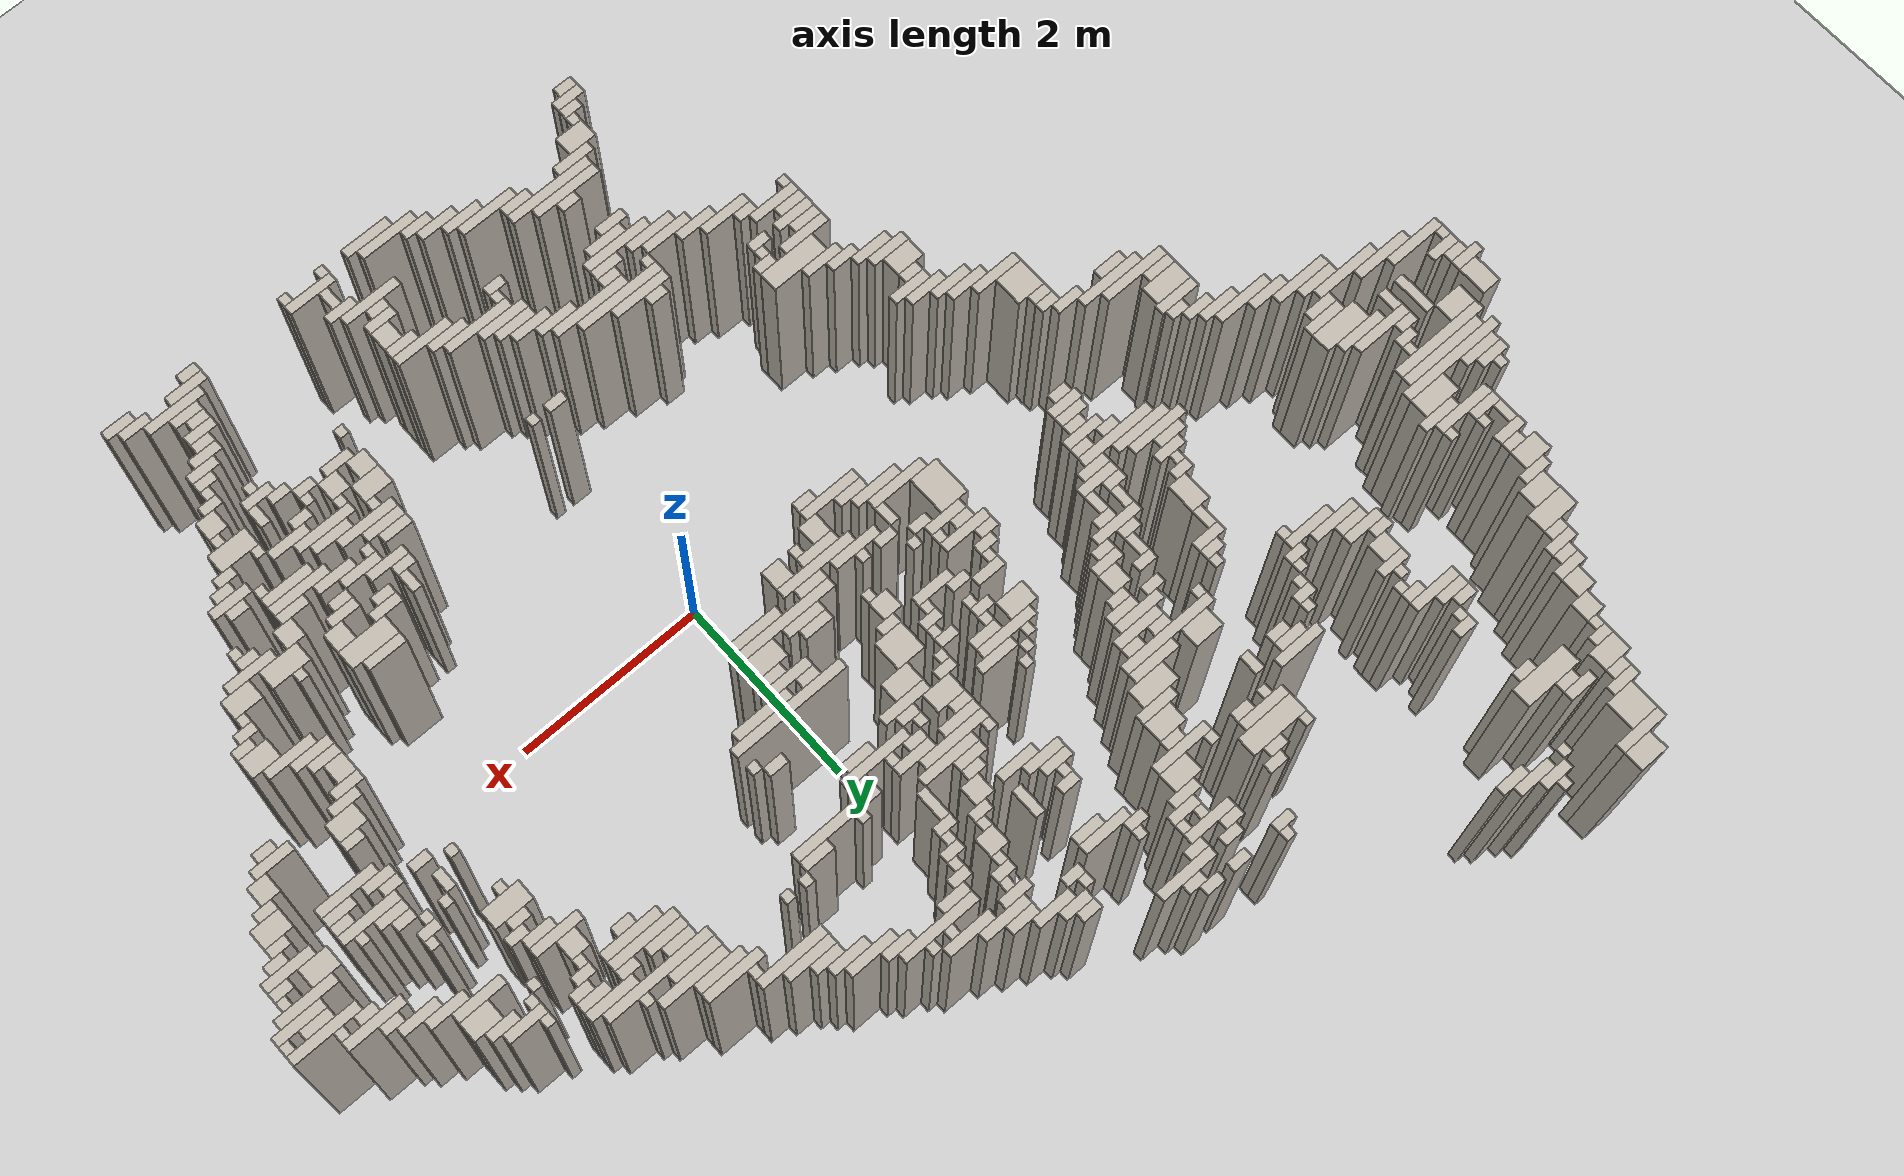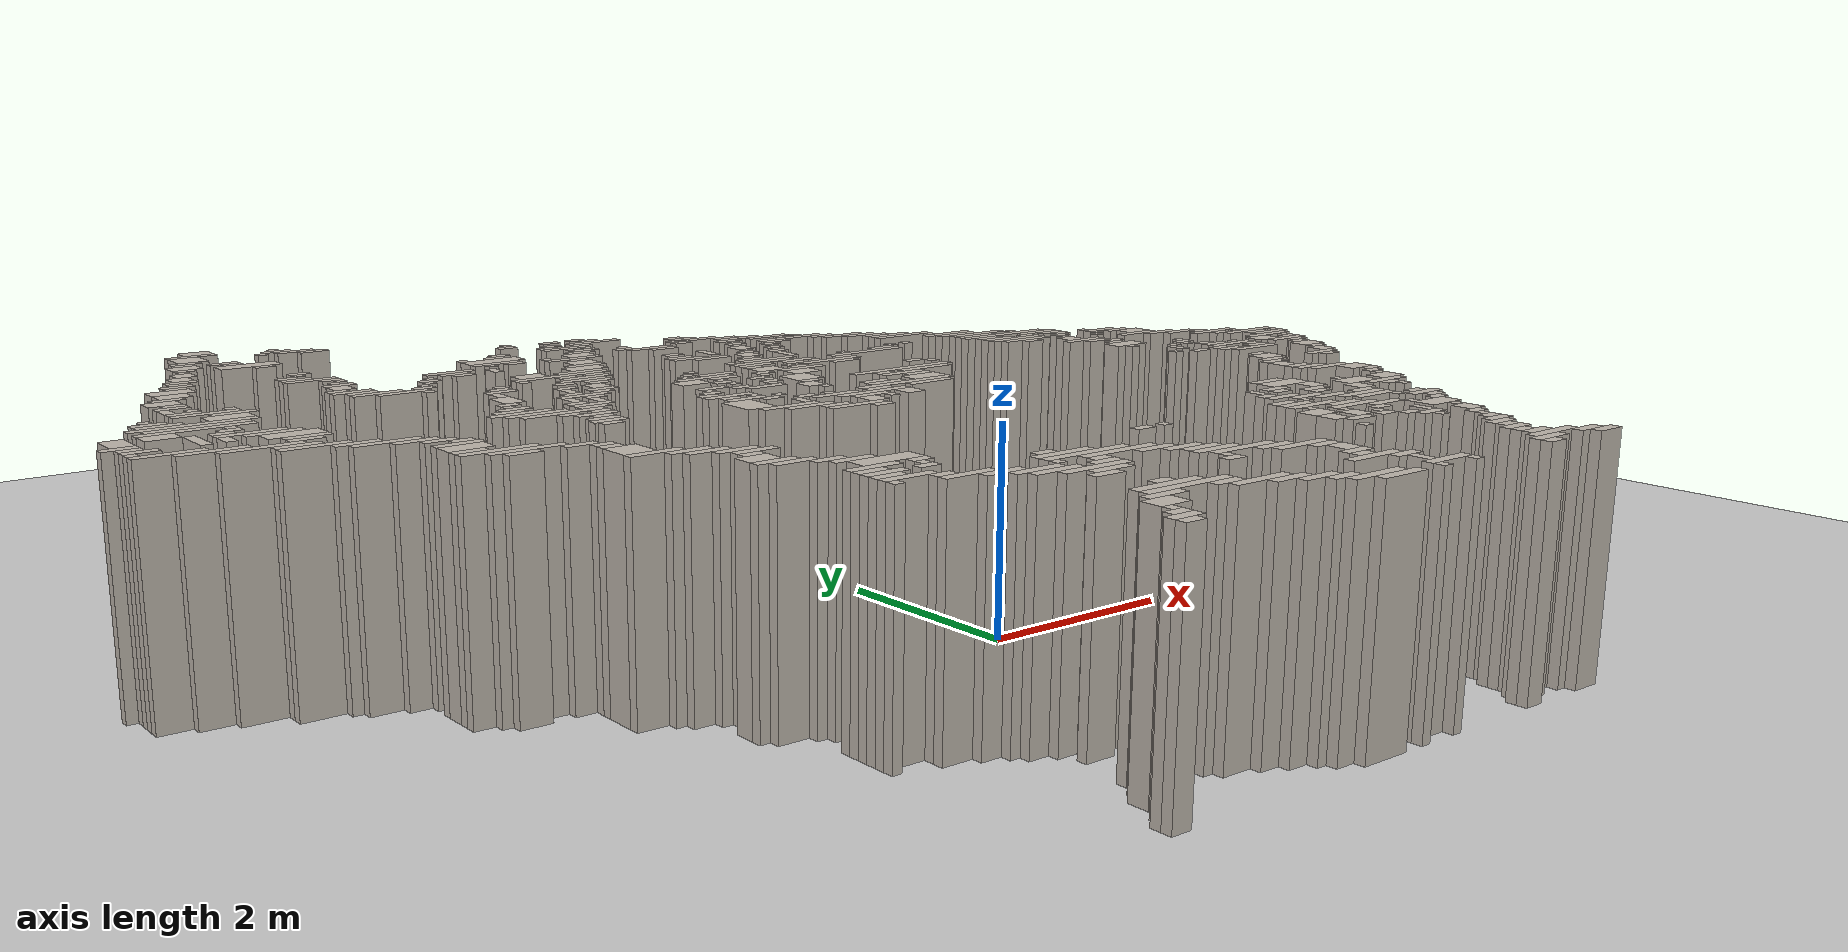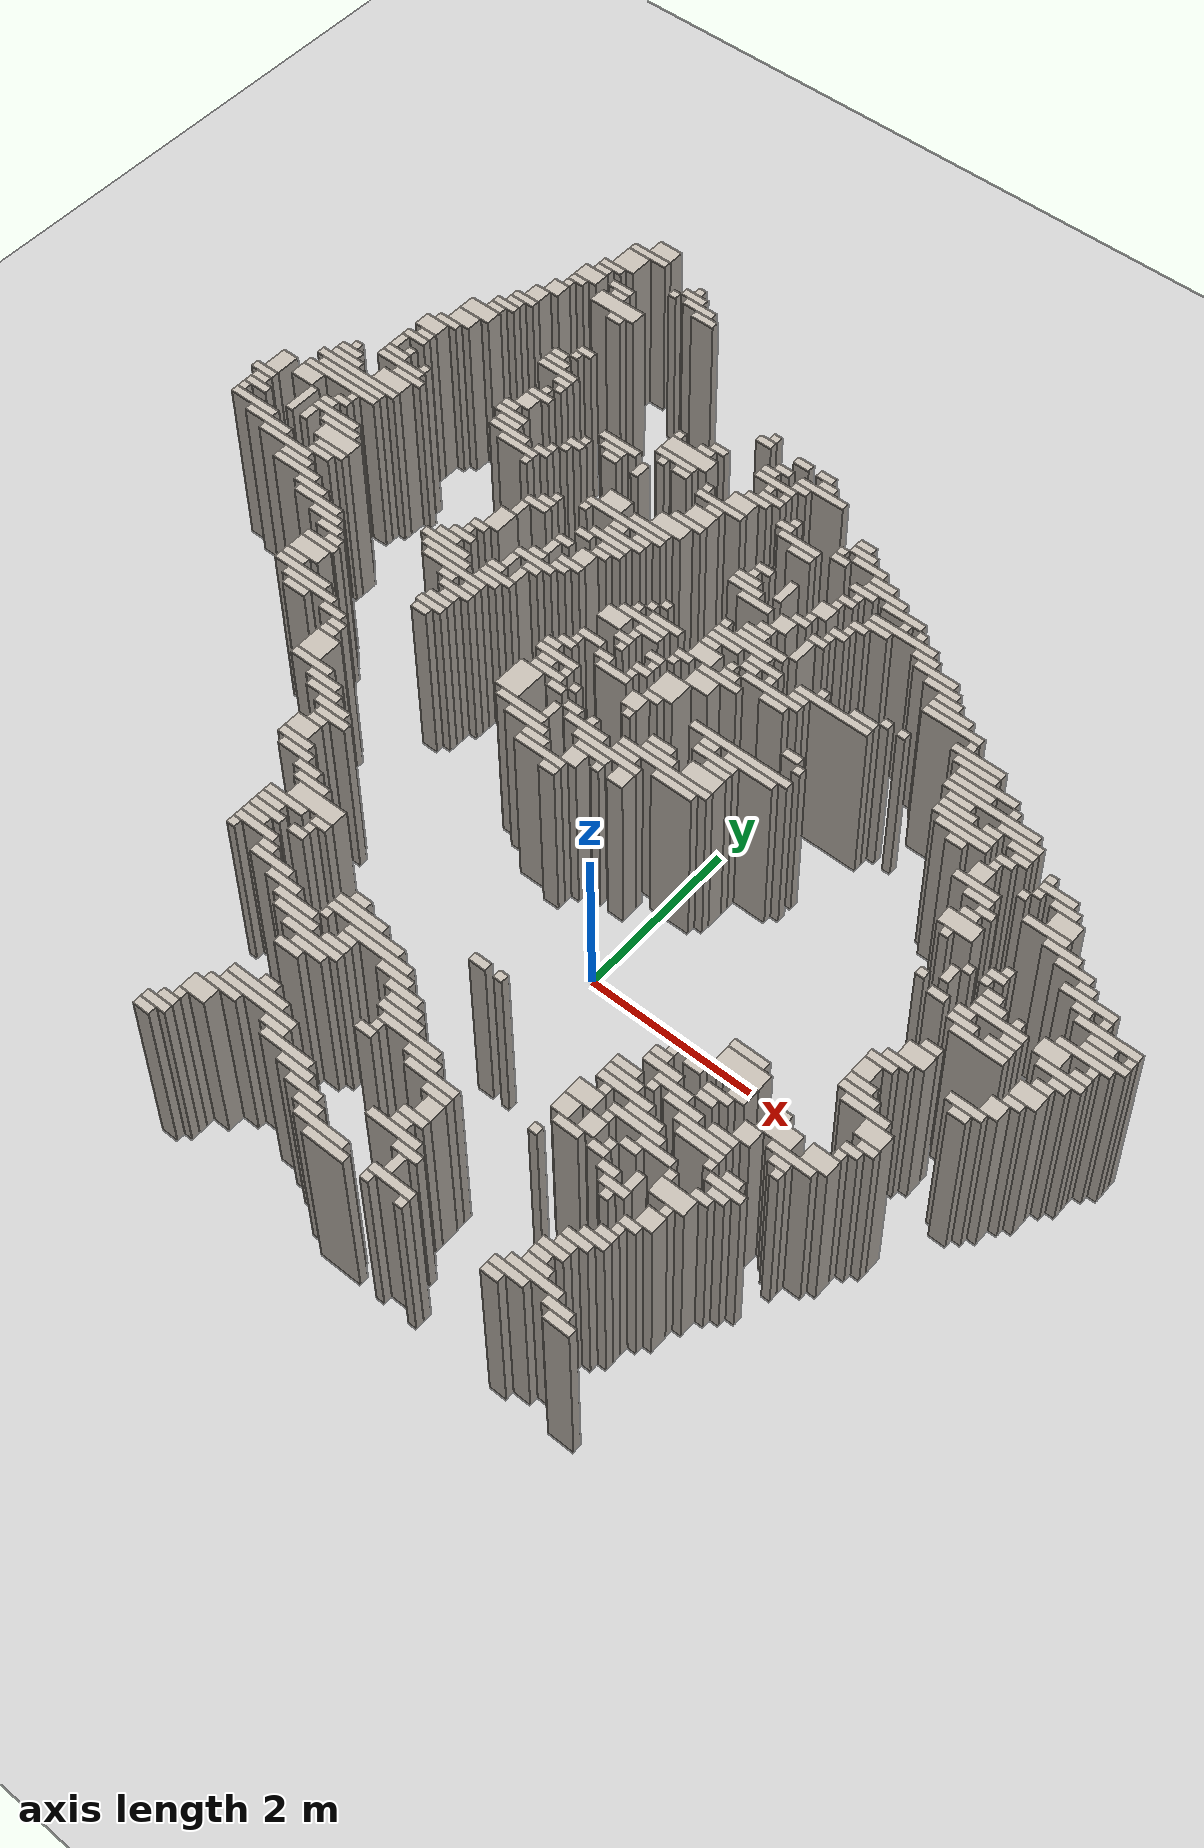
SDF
<?xml version="1.0" ?>
<sdf version="1.6">
  <world name="lab">
    <include><uri>model://sun</uri></include>
    <include><uri>model://ground_plane</uri></include>
    <model name="lab_walls"><static>true</static><link name="walls">
      <collision name="c_w0"><pose>-1.95 -3.90 1.10 0 0 0</pose><geometry><box><size>0.20 0.10 2.20</size></box></geometry></collision>
      <visual name="v_w0"><pose>-1.95 -3.90 1.10 0 0 0</pose><geometry><box><size>0.20 0.10 2.20</size></box></geometry><material><ambient>0.75 0.72 0.68 1</ambient><diffuse>0.75 0.72 0.68 1</diffuse></material></visual>
      <collision name="c_w1"><pose>0.30 -3.90 1.10 0 0 0</pose><geometry><box><size>0.50 0.10 2.20</size></box></geometry></collision>
      <visual name="v_w1"><pose>0.30 -3.90 1.10 0 0 0</pose><geometry><box><size>0.50 0.10 2.20</size></box></geometry><material><ambient>0.75 0.72 0.68 1</ambient><diffuse>0.75 0.72 0.68 1</diffuse></material></visual>
      <collision name="c_w2"><pose>0.80 -3.90 1.10 0 0 0</pose><geometry><box><size>0.10 0.10 2.20</size></box></geometry></collision>
      <visual name="v_w2"><pose>0.80 -3.90 1.10 0 0 0</pose><geometry><box><size>0.10 0.10 2.20</size></box></geometry><material><ambient>0.75 0.72 0.68 1</ambient><diffuse>0.75 0.72 0.68 1</diffuse></material></visual>
      <collision name="c_w3"><pose>1.20 -3.90 1.10 0 0 0</pose><geometry><box><size>0.10 0.10 2.20</size></box></geometry></collision>
      <visual name="v_w3"><pose>1.20 -3.90 1.10 0 0 0</pose><geometry><box><size>0.10 0.10 2.20</size></box></geometry><material><ambient>0.75 0.72 0.68 1</ambient><diffuse>0.75 0.72 0.68 1</diffuse></material></visual>
      <collision name="c_w4"><pose>2.25 -3.90 1.10 0 0 0</pose><geometry><box><size>0.20 0.10 2.20</size></box></geometry></collision>
      <visual name="v_w4"><pose>2.25 -3.90 1.10 0 0 0</pose><geometry><box><size>0.20 0.10 2.20</size></box></geometry><material><ambient>0.75 0.72 0.68 1</ambient><diffuse>0.75 0.72 0.68 1</diffuse></material></visual>
      <collision name="c_w5"><pose>3.00 -3.90 1.10 0 0 0</pose><geometry><box><size>0.30 0.10 2.20</size></box></geometry></collision>
      <visual name="v_w5"><pose>3.00 -3.90 1.10 0 0 0</pose><geometry><box><size>0.30 0.10 2.20</size></box></geometry><material><ambient>0.75 0.72 0.68 1</ambient><diffuse>0.75 0.72 0.68 1</diffuse></material></visual>
      <collision name="c_w6"><pose>-1.90 -3.80 1.10 0 0 0</pose><geometry><box><size>0.30 0.10 2.20</size></box></geometry></collision>
      <visual name="v_w6"><pose>-1.90 -3.80 1.10 0 0 0</pose><geometry><box><size>0.30 0.10 2.20</size></box></geometry><material><ambient>0.75 0.72 0.68 1</ambient><diffuse>0.75 0.72 0.68 1</diffuse></material></visual>
      <collision name="c_w7"><pose>0.15 -3.80 1.10 0 0 0</pose><geometry><box><size>0.60 0.10 2.20</size></box></geometry></collision>
      <visual name="v_w7"><pose>0.15 -3.80 1.10 0 0 0</pose><geometry><box><size>0.60 0.10 2.20</size></box></geometry><material><ambient>0.75 0.72 0.68 1</ambient><diffuse>0.75 0.72 0.68 1</diffuse></material></visual>
      <collision name="c_w8"><pose>1.00 -3.80 1.10 0 0 0</pose><geometry><box><size>0.50 0.10 2.20</size></box></geometry></collision>
      <visual name="v_w8"><pose>1.00 -3.80 1.10 0 0 0</pose><geometry><box><size>0.50 0.10 2.20</size></box></geometry><material><ambient>0.75 0.72 0.68 1</ambient><diffuse>0.75 0.72 0.68 1</diffuse></material></visual>
      <collision name="c_w9"><pose>2.35 -3.80 1.10 0 0 0</pose><geometry><box><size>0.40 0.10 2.20</size></box></geometry></collision>
      <visual name="v_w9"><pose>2.35 -3.80 1.10 0 0 0</pose><geometry><box><size>0.40 0.10 2.20</size></box></geometry><material><ambient>0.75 0.72 0.68 1</ambient><diffuse>0.75 0.72 0.68 1</diffuse></material></visual>
      <collision name="c_w10"><pose>2.90 -3.80 1.10 0 0 0</pose><geometry><box><size>0.30 0.10 2.20</size></box></geometry></collision>
      <visual name="v_w10"><pose>2.90 -3.80 1.10 0 0 0</pose><geometry><box><size>0.30 0.10 2.20</size></box></geometry><material><ambient>0.75 0.72 0.68 1</ambient><diffuse>0.75 0.72 0.68 1</diffuse></material></visual>
      <collision name="c_w11"><pose>-1.85 -3.70 1.10 0 0 0</pose><geometry><box><size>0.20 0.10 2.20</size></box></geometry></collision>
      <visual name="v_w11"><pose>-1.85 -3.70 1.10 0 0 0</pose><geometry><box><size>0.20 0.10 2.20</size></box></geometry><material><ambient>0.75 0.72 0.68 1</ambient><diffuse>0.75 0.72 0.68 1</diffuse></material></visual>
      <collision name="c_w12"><pose>-0.10 -3.70 1.10 0 0 0</pose><geometry><box><size>0.30 0.10 2.20</size></box></geometry></collision>
      <visual name="v_w12"><pose>-0.10 -3.70 1.10 0 0 0</pose><geometry><box><size>0.30 0.10 2.20</size></box></geometry><material><ambient>0.75 0.72 0.68 1</ambient><diffuse>0.75 0.72 0.68 1</diffuse></material></visual>
      <collision name="c_w13"><pose>0.90 -3.65 1.10 0 0 0</pose><geometry><box><size>0.10 0.20 2.20</size></box></geometry></collision>
      <visual name="v_w13"><pose>0.90 -3.65 1.10 0 0 0</pose><geometry><box><size>0.10 0.20 2.20</size></box></geometry><material><ambient>0.75 0.72 0.68 1</ambient><diffuse>0.75 0.72 0.68 1</diffuse></material></visual>
      <collision name="c_w14"><pose>2.55 -3.70 1.10 0 0 0</pose><geometry><box><size>0.60 0.10 2.20</size></box></geometry></collision>
      <visual name="v_w14"><pose>2.55 -3.70 1.10 0 0 0</pose><geometry><box><size>0.60 0.10 2.20</size></box></geometry><material><ambient>0.75 0.72 0.68 1</ambient><diffuse>0.75 0.72 0.68 1</diffuse></material></visual>
      <collision name="c_w15"><pose>-1.80 -3.60 1.10 0 0 0</pose><geometry><box><size>0.10 0.10 2.20</size></box></geometry></collision>
      <visual name="v_w15"><pose>-1.80 -3.60 1.10 0 0 0</pose><geometry><box><size>0.10 0.10 2.20</size></box></geometry><material><ambient>0.75 0.72 0.68 1</ambient><diffuse>0.75 0.72 0.68 1</diffuse></material></visual>
      <collision name="c_w16"><pose>-0.25 -3.60 1.10 0 0 0</pose><geometry><box><size>0.40 0.10 2.20</size></box></geometry></collision>
      <visual name="v_w16"><pose>-0.25 -3.60 1.10 0 0 0</pose><geometry><box><size>0.40 0.10 2.20</size></box></geometry><material><ambient>0.75 0.72 0.68 1</ambient><diffuse>0.75 0.72 0.68 1</diffuse></material></visual>
      <collision name="c_w17"><pose>2.50 -3.60 1.10 0 0 0</pose><geometry><box><size>0.30 0.10 2.20</size></box></geometry></collision>
      <visual name="v_w17"><pose>2.50 -3.60 1.10 0 0 0</pose><geometry><box><size>0.30 0.10 2.20</size></box></geometry><material><ambient>0.75 0.72 0.68 1</ambient><diffuse>0.75 0.72 0.68 1</diffuse></material></visual>
      <collision name="c_w18"><pose>-1.70 -3.45 1.10 0 0 0</pose><geometry><box><size>0.30 0.20 2.20</size></box></geometry></collision>
      <visual name="v_w18"><pose>-1.70 -3.45 1.10 0 0 0</pose><geometry><box><size>0.30 0.20 2.20</size></box></geometry><material><ambient>0.75 0.72 0.68 1</ambient><diffuse>0.75 0.72 0.68 1</diffuse></material></visual>
      <collision name="c_w19"><pose>-0.45 -3.50 1.10 0 0 0</pose><geometry><box><size>0.40 0.10 2.20</size></box></geometry></collision>
      <visual name="v_w19"><pose>-0.45 -3.50 1.10 0 0 0</pose><geometry><box><size>0.40 0.10 2.20</size></box></geometry><material><ambient>0.75 0.72 0.68 1</ambient><diffuse>0.75 0.72 0.68 1</diffuse></material></visual>
      <collision name="c_w20"><pose>0.90 -3.50 1.10 0 0 0</pose><geometry><box><size>0.30 0.10 2.20</size></box></geometry></collision>
      <visual name="v_w20"><pose>0.90 -3.50 1.10 0 0 0</pose><geometry><box><size>0.30 0.10 2.20</size></box></geometry><material><ambient>0.75 0.72 0.68 1</ambient><diffuse>0.75 0.72 0.68 1</diffuse></material></visual>
      <collision name="c_w21"><pose>2.45 -3.50 1.10 0 0 0</pose><geometry><box><size>0.20 0.10 2.20</size></box></geometry></collision>
      <visual name="v_w21"><pose>2.45 -3.50 1.10 0 0 0</pose><geometry><box><size>0.20 0.10 2.20</size></box></geometry><material><ambient>0.75 0.72 0.68 1</ambient><diffuse>0.75 0.72 0.68 1</diffuse></material></visual>
      <collision name="c_w22"><pose>-0.65 -3.40 1.10 0 0 0</pose><geometry><box><size>0.60 0.10 2.20</size></box></geometry></collision>
      <visual name="v_w22"><pose>-0.65 -3.40 1.10 0 0 0</pose><geometry><box><size>0.60 0.10 2.20</size></box></geometry><material><ambient>0.75 0.72 0.68 1</ambient><diffuse>0.75 0.72 0.68 1</diffuse></material></visual>
      <collision name="c_w23"><pose>0.65 -3.40 1.10 0 0 0</pose><geometry><box><size>0.60 0.10 2.20</size></box></geometry></collision>
      <visual name="v_w23"><pose>0.65 -3.40 1.10 0 0 0</pose><geometry><box><size>0.60 0.10 2.20</size></box></geometry><material><ambient>0.75 0.72 0.68 1</ambient><diffuse>0.75 0.72 0.68 1</diffuse></material></visual>
      <collision name="c_w24"><pose>2.50 -3.40 1.10 0 0 0</pose><geometry><box><size>0.30 0.10 2.20</size></box></geometry></collision>
      <visual name="v_w24"><pose>2.50 -3.40 1.10 0 0 0</pose><geometry><box><size>0.30 0.10 2.20</size></box></geometry><material><ambient>0.75 0.72 0.68 1</ambient><diffuse>0.75 0.72 0.68 1</diffuse></material></visual>
      <collision name="c_w25"><pose>-1.55 -3.30 1.10 0 0 0</pose><geometry><box><size>0.40 0.10 2.20</size></box></geometry></collision>
      <visual name="v_w25"><pose>-1.55 -3.30 1.10 0 0 0</pose><geometry><box><size>0.40 0.10 2.20</size></box></geometry><material><ambient>0.75 0.72 0.68 1</ambient><diffuse>0.75 0.72 0.68 1</diffuse></material></visual>
      <collision name="c_w26"><pose>-0.90 -3.30 1.10 0 0 0</pose><geometry><box><size>0.30 0.10 2.20</size></box></geometry></collision>
      <visual name="v_w26"><pose>-0.90 -3.30 1.10 0 0 0</pose><geometry><box><size>0.30 0.10 2.20</size></box></geometry><material><ambient>0.75 0.72 0.68 1</ambient><diffuse>0.75 0.72 0.68 1</diffuse></material></visual>
      <collision name="c_w27"><pose>0.65 -3.30 1.10 0 0 0</pose><geometry><box><size>0.20 0.10 2.20</size></box></geometry></collision>
      <visual name="v_w27"><pose>0.65 -3.30 1.10 0 0 0</pose><geometry><box><size>0.20 0.10 2.20</size></box></geometry><material><ambient>0.75 0.72 0.68 1</ambient><diffuse>0.75 0.72 0.68 1</diffuse></material></visual>
      <collision name="c_w28"><pose>2.55 -3.30 1.10 0 0 0</pose><geometry><box><size>0.20 0.10 2.20</size></box></geometry></collision>
      <visual name="v_w28"><pose>2.55 -3.30 1.10 0 0 0</pose><geometry><box><size>0.20 0.10 2.20</size></box></geometry><material><ambient>0.75 0.72 0.68 1</ambient><diffuse>0.75 0.72 0.68 1</diffuse></material></visual>
      <collision name="c_w29"><pose>-1.20 -3.20 1.10 0 0 0</pose><geometry><box><size>0.90 0.10 2.20</size></box></geometry></collision>
      <visual name="v_w29"><pose>-1.20 -3.20 1.10 0 0 0</pose><geometry><box><size>0.90 0.10 2.20</size></box></geometry><material><ambient>0.75 0.72 0.68 1</ambient><diffuse>0.75 0.72 0.68 1</diffuse></material></visual>
      <collision name="c_w30"><pose>0.70 -3.20 1.10 0 0 0</pose><geometry><box><size>0.30 0.10 2.20</size></box></geometry></collision>
      <visual name="v_w30"><pose>0.70 -3.20 1.10 0 0 0</pose><geometry><box><size>0.30 0.10 2.20</size></box></geometry><material><ambient>0.75 0.72 0.68 1</ambient><diffuse>0.75 0.72 0.68 1</diffuse></material></visual>
      <collision name="c_w31"><pose>2.60 -3.20 1.10 0 0 0</pose><geometry><box><size>0.30 0.10 2.20</size></box></geometry></collision>
      <visual name="v_w31"><pose>2.60 -3.20 1.10 0 0 0</pose><geometry><box><size>0.30 0.10 2.20</size></box></geometry><material><ambient>0.75 0.72 0.68 1</ambient><diffuse>0.75 0.72 0.68 1</diffuse></material></visual>
      <collision name="c_w32"><pose>-1.30 -3.10 1.10 0 0 0</pose><geometry><box><size>0.70 0.10 2.20</size></box></geometry></collision>
      <visual name="v_w32"><pose>-1.30 -3.10 1.10 0 0 0</pose><geometry><box><size>0.70 0.10 2.20</size></box></geometry><material><ambient>0.75 0.72 0.68 1</ambient><diffuse>0.75 0.72 0.68 1</diffuse></material></visual>
      <collision name="c_w33"><pose>0.75 -3.05 1.10 0 0 0</pose><geometry><box><size>0.20 0.20 2.20</size></box></geometry></collision>
      <visual name="v_w33"><pose>0.75 -3.05 1.10 0 0 0</pose><geometry><box><size>0.20 0.20 2.20</size></box></geometry><material><ambient>0.75 0.72 0.68 1</ambient><diffuse>0.75 0.72 0.68 1</diffuse></material></visual>
      <collision name="c_w34"><pose>2.70 -3.10 1.10 0 0 0</pose><geometry><box><size>0.30 0.10 2.20</size></box></geometry></collision>
      <visual name="v_w34"><pose>2.70 -3.10 1.10 0 0 0</pose><geometry><box><size>0.30 0.10 2.20</size></box></geometry><material><ambient>0.75 0.72 0.68 1</ambient><diffuse>0.75 0.72 0.68 1</diffuse></material></visual>
      <collision name="c_w35"><pose>-1.25 -3.00 1.10 0 0 0</pose><geometry><box><size>0.20 0.10 2.20</size></box></geometry></collision>
      <visual name="v_w35"><pose>-1.25 -3.00 1.10 0 0 0</pose><geometry><box><size>0.20 0.10 2.20</size></box></geometry><material><ambient>0.75 0.72 0.68 1</ambient><diffuse>0.75 0.72 0.68 1</diffuse></material></visual>
      <collision name="c_w36"><pose>2.75 -3.00 1.10 0 0 0</pose><geometry><box><size>0.20 0.10 2.20</size></box></geometry></collision>
      <visual name="v_w36"><pose>2.75 -3.00 1.10 0 0 0</pose><geometry><box><size>0.20 0.10 2.20</size></box></geometry><material><ambient>0.75 0.72 0.68 1</ambient><diffuse>0.75 0.72 0.68 1</diffuse></material></visual>
      <collision name="c_w37"><pose>0.70 -2.90 1.10 0 0 0</pose><geometry><box><size>0.30 0.10 2.20</size></box></geometry></collision>
      <visual name="v_w37"><pose>0.70 -2.90 1.10 0 0 0</pose><geometry><box><size>0.30 0.10 2.20</size></box></geometry><material><ambient>0.75 0.72 0.68 1</ambient><diffuse>0.75 0.72 0.68 1</diffuse></material></visual>
      <collision name="c_w38"><pose>2.80 -2.90 1.10 0 0 0</pose><geometry><box><size>0.10 0.10 2.20</size></box></geometry></collision>
      <visual name="v_w38"><pose>2.80 -2.90 1.10 0 0 0</pose><geometry><box><size>0.10 0.10 2.20</size></box></geometry><material><ambient>0.75 0.72 0.68 1</ambient><diffuse>0.75 0.72 0.68 1</diffuse></material></visual>
      <collision name="c_w39"><pose>-0.25 -2.80 1.10 0 0 0</pose><geometry><box><size>0.20 0.10 2.20</size></box></geometry></collision>
      <visual name="v_w39"><pose>-0.25 -2.80 1.10 0 0 0</pose><geometry><box><size>0.20 0.10 2.20</size></box></geometry><material><ambient>0.75 0.72 0.68 1</ambient><diffuse>0.75 0.72 0.68 1</diffuse></material></visual>
      <collision name="c_w40"><pose>0.55 -2.80 1.10 0 0 0</pose><geometry><box><size>0.60 0.10 2.20</size></box></geometry></collision>
      <visual name="v_w40"><pose>0.55 -2.80 1.10 0 0 0</pose><geometry><box><size>0.60 0.10 2.20</size></box></geometry><material><ambient>0.75 0.72 0.68 1</ambient><diffuse>0.75 0.72 0.68 1</diffuse></material></visual>
      <collision name="c_w41"><pose>2.85 -2.80 1.10 0 0 0</pose><geometry><box><size>0.20 0.10 2.20</size></box></geometry></collision>
      <visual name="v_w41"><pose>2.85 -2.80 1.10 0 0 0</pose><geometry><box><size>0.20 0.10 2.20</size></box></geometry><material><ambient>0.75 0.72 0.68 1</ambient><diffuse>0.75 0.72 0.68 1</diffuse></material></visual>
      <collision name="c_w42"><pose>-0.20 -2.70 1.10 0 0 0</pose><geometry><box><size>0.10 0.10 2.20</size></box></geometry></collision>
      <visual name="v_w42"><pose>-0.20 -2.70 1.10 0 0 0</pose><geometry><box><size>0.10 0.10 2.20</size></box></geometry><material><ambient>0.75 0.72 0.68 1</ambient><diffuse>0.75 0.72 0.68 1</diffuse></material></visual>
      <collision name="c_w43"><pose>0.35 -2.70 1.10 0 0 0</pose><geometry><box><size>0.40 0.10 2.20</size></box></geometry></collision>
      <visual name="v_w43"><pose>0.35 -2.70 1.10 0 0 0</pose><geometry><box><size>0.40 0.10 2.20</size></box></geometry><material><ambient>0.75 0.72 0.68 1</ambient><diffuse>0.75 0.72 0.68 1</diffuse></material></visual>
      <collision name="c_w44"><pose>2.50 -2.70 1.10 0 0 0</pose><geometry><box><size>0.10 0.10 2.20</size></box></geometry></collision>
      <visual name="v_w44"><pose>2.50 -2.70 1.10 0 0 0</pose><geometry><box><size>0.10 0.10 2.20</size></box></geometry><material><ambient>0.75 0.72 0.68 1</ambient><diffuse>0.75 0.72 0.68 1</diffuse></material></visual>
      <collision name="c_w45"><pose>2.95 -2.65 1.10 0 0 0</pose><geometry><box><size>0.20 0.20 2.20</size></box></geometry></collision>
      <visual name="v_w45"><pose>2.95 -2.65 1.10 0 0 0</pose><geometry><box><size>0.20 0.20 2.20</size></box></geometry><material><ambient>0.75 0.72 0.68 1</ambient><diffuse>0.75 0.72 0.68 1</diffuse></material></visual>
      <collision name="c_w46"><pose>-1.40 -2.60 1.10 0 0 0</pose><geometry><box><size>0.30 0.10 2.20</size></box></geometry></collision>
      <visual name="v_w46"><pose>-1.40 -2.60 1.10 0 0 0</pose><geometry><box><size>0.30 0.10 2.20</size></box></geometry><material><ambient>0.75 0.72 0.68 1</ambient><diffuse>0.75 0.72 0.68 1</diffuse></material></visual>
      <collision name="c_w47"><pose>0.10 -2.60 1.10 0 0 0</pose><geometry><box><size>0.70 0.10 2.20</size></box></geometry></collision>
      <visual name="v_w47"><pose>0.10 -2.60 1.10 0 0 0</pose><geometry><box><size>0.70 0.10 2.20</size></box></geometry><material><ambient>0.75 0.72 0.68 1</ambient><diffuse>0.75 0.72 0.68 1</diffuse></material></visual>
      <collision name="c_w48"><pose>1.60 -2.60 1.10 0 0 0</pose><geometry><box><size>0.10 0.10 2.20</size></box></geometry></collision>
      <visual name="v_w48"><pose>1.60 -2.60 1.10 0 0 0</pose><geometry><box><size>0.10 0.10 2.20</size></box></geometry><material><ambient>0.75 0.72 0.68 1</ambient><diffuse>0.75 0.72 0.68 1</diffuse></material></visual>
      <collision name="c_w49"><pose>2.50 -2.60 1.10 0 0 0</pose><geometry><box><size>0.30 0.10 2.20</size></box></geometry></collision>
      <visual name="v_w49"><pose>2.50 -2.60 1.10 0 0 0</pose><geometry><box><size>0.30 0.10 2.20</size></box></geometry><material><ambient>0.75 0.72 0.68 1</ambient><diffuse>0.75 0.72 0.68 1</diffuse></material></visual>
      <collision name="c_w50"><pose>-1.25 -2.50 1.10 0 0 0</pose><geometry><box><size>0.40 0.10 2.20</size></box></geometry></collision>
      <visual name="v_w50"><pose>-1.25 -2.50 1.10 0 0 0</pose><geometry><box><size>0.40 0.10 2.20</size></box></geometry><material><ambient>0.75 0.72 0.68 1</ambient><diffuse>0.75 0.72 0.68 1</diffuse></material></visual>
      <collision name="c_w51"><pose>-0.10 -2.50 1.10 0 0 0</pose><geometry><box><size>0.50 0.10 2.20</size></box></geometry></collision>
      <visual name="v_w51"><pose>-0.10 -2.50 1.10 0 0 0</pose><geometry><box><size>0.50 0.10 2.20</size></box></geometry><material><ambient>0.75 0.72 0.68 1</ambient><diffuse>0.75 0.72 0.68 1</diffuse></material></visual>
      <collision name="c_w52"><pose>2.35 -2.50 1.10 0 0 0</pose><geometry><box><size>0.20 0.10 2.20</size></box></geometry></collision>
      <visual name="v_w52"><pose>2.35 -2.50 1.10 0 0 0</pose><geometry><box><size>0.20 0.10 2.20</size></box></geometry><material><ambient>0.75 0.72 0.68 1</ambient><diffuse>0.75 0.72 0.68 1</diffuse></material></visual>
      <collision name="c_w53"><pose>2.60 -2.45 1.10 0 0 0</pose><geometry><box><size>0.10 0.20 2.20</size></box></geometry></collision>
      <visual name="v_w53"><pose>2.60 -2.45 1.10 0 0 0</pose><geometry><box><size>0.10 0.20 2.20</size></box></geometry><material><ambient>0.75 0.72 0.68 1</ambient><diffuse>0.75 0.72 0.68 1</diffuse></material></visual>
      <collision name="c_w54"><pose>3.00 -2.50 1.10 0 0 0</pose><geometry><box><size>0.10 0.10 2.20</size></box></geometry></collision>
      <visual name="v_w54"><pose>3.00 -2.50 1.10 0 0 0</pose><geometry><box><size>0.10 0.10 2.20</size></box></geometry><material><ambient>0.75 0.72 0.68 1</ambient><diffuse>0.75 0.72 0.68 1</diffuse></material></visual>
      <collision name="c_w55"><pose>-1.30 -2.40 1.10 0 0 0</pose><geometry><box><size>0.70 0.10 2.20</size></box></geometry></collision>
      <visual name="v_w55"><pose>-1.30 -2.40 1.10 0 0 0</pose><geometry><box><size>0.70 0.10 2.20</size></box></geometry><material><ambient>0.75 0.72 0.68 1</ambient><diffuse>0.75 0.72 0.68 1</diffuse></material></visual>
      <collision name="c_w56"><pose>-0.15 -2.40 1.10 0 0 0</pose><geometry><box><size>0.40 0.10 2.20</size></box></geometry></collision>
      <visual name="v_w56"><pose>-0.15 -2.40 1.10 0 0 0</pose><geometry><box><size>0.40 0.10 2.20</size></box></geometry><material><ambient>0.75 0.72 0.68 1</ambient><diffuse>0.75 0.72 0.68 1</diffuse></material></visual>
      <collision name="c_w57"><pose>1.80 -2.40 1.10 0 0 0</pose><geometry><box><size>0.30 0.10 2.20</size></box></geometry></collision>
      <visual name="v_w57"><pose>1.80 -2.40 1.10 0 0 0</pose><geometry><box><size>0.30 0.10 2.20</size></box></geometry><material><ambient>0.75 0.72 0.68 1</ambient><diffuse>0.75 0.72 0.68 1</diffuse></material></visual>
      <collision name="c_w58"><pose>2.15 -2.40 1.10 0 0 0</pose><geometry><box><size>0.20 0.10 2.20</size></box></geometry></collision>
      <visual name="v_w58"><pose>2.15 -2.40 1.10 0 0 0</pose><geometry><box><size>0.20 0.10 2.20</size></box></geometry><material><ambient>0.75 0.72 0.68 1</ambient><diffuse>0.75 0.72 0.68 1</diffuse></material></visual>
      <collision name="c_w59"><pose>2.95 -2.35 1.10 0 0 0</pose><geometry><box><size>0.40 0.20 2.20</size></box></geometry></collision>
      <visual name="v_w59"><pose>2.95 -2.35 1.10 0 0 0</pose><geometry><box><size>0.40 0.20 2.20</size></box></geometry><material><ambient>0.75 0.72 0.68 1</ambient><diffuse>0.75 0.72 0.68 1</diffuse></material></visual>
      <collision name="c_w60"><pose>-1.60 -2.30 1.10 0 0 0</pose><geometry><box><size>0.50 0.10 2.20</size></box></geometry></collision>
      <visual name="v_w60"><pose>-1.60 -2.30 1.10 0 0 0</pose><geometry><box><size>0.50 0.10 2.20</size></box></geometry><material><ambient>0.75 0.72 0.68 1</ambient><diffuse>0.75 0.72 0.68 1</diffuse></material></visual>
      <collision name="c_w61"><pose>-1.10 -2.30 1.10 0 0 0</pose><geometry><box><size>0.30 0.10 2.20</size></box></geometry></collision>
      <visual name="v_w61"><pose>-1.10 -2.30 1.10 0 0 0</pose><geometry><box><size>0.30 0.10 2.20</size></box></geometry><material><ambient>0.75 0.72 0.68 1</ambient><diffuse>0.75 0.72 0.68 1</diffuse></material></visual>
      <collision name="c_w62"><pose>-0.25 -2.30 1.10 0 0 0</pose><geometry><box><size>0.40 0.10 2.20</size></box></geometry></collision>
      <visual name="v_w62"><pose>-0.25 -2.30 1.10 0 0 0</pose><geometry><box><size>0.40 0.10 2.20</size></box></geometry><material><ambient>0.75 0.72 0.68 1</ambient><diffuse>0.75 0.72 0.68 1</diffuse></material></visual>
      <collision name="c_w63"><pose>1.65 -2.25 1.10 0 0 0</pose><geometry><box><size>0.20 0.20 2.20</size></box></geometry></collision>
      <visual name="v_w63"><pose>1.65 -2.25 1.10 0 0 0</pose><geometry><box><size>0.20 0.20 2.20</size></box></geometry><material><ambient>0.75 0.72 0.68 1</ambient><diffuse>0.75 0.72 0.68 1</diffuse></material></visual>
      <collision name="c_w64"><pose>1.95 -2.25 1.10 0 0 0</pose><geometry><box><size>0.20 0.20 2.20</size></box></geometry></collision>
      <visual name="v_w64"><pose>1.95 -2.25 1.10 0 0 0</pose><geometry><box><size>0.20 0.20 2.20</size></box></geometry><material><ambient>0.75 0.72 0.68 1</ambient><diffuse>0.75 0.72 0.68 1</diffuse></material></visual>
      <collision name="c_w65"><pose>2.20 -2.30 1.10 0 0 0</pose><geometry><box><size>0.10 0.10 2.20</size></box></geometry></collision>
      <visual name="v_w65"><pose>2.20 -2.30 1.10 0 0 0</pose><geometry><box><size>0.10 0.10 2.20</size></box></geometry><material><ambient>0.75 0.72 0.68 1</ambient><diffuse>0.75 0.72 0.68 1</diffuse></material></visual>
      <collision name="c_w66"><pose>-1.70 -2.20 1.10 0 0 0</pose><geometry><box><size>0.50 0.10 2.20</size></box></geometry></collision>
      <visual name="v_w66"><pose>-1.70 -2.20 1.10 0 0 0</pose><geometry><box><size>0.50 0.10 2.20</size></box></geometry><material><ambient>0.75 0.72 0.68 1</ambient><diffuse>0.75 0.72 0.68 1</diffuse></material></visual>
      <collision name="c_w67"><pose>-1.05 -2.20 1.10 0 0 0</pose><geometry><box><size>0.20 0.10 2.20</size></box></geometry></collision>
      <visual name="v_w67"><pose>-1.05 -2.20 1.10 0 0 0</pose><geometry><box><size>0.20 0.10 2.20</size></box></geometry><material><ambient>0.75 0.72 0.68 1</ambient><diffuse>0.75 0.72 0.68 1</diffuse></material></visual>
      <collision name="c_w68"><pose>-0.45 -2.20 1.10 0 0 0</pose><geometry><box><size>0.40 0.10 2.20</size></box></geometry></collision>
      <visual name="v_w68"><pose>-0.45 -2.20 1.10 0 0 0</pose><geometry><box><size>0.40 0.10 2.20</size></box></geometry><material><ambient>0.75 0.72 0.68 1</ambient><diffuse>0.75 0.72 0.68 1</diffuse></material></visual>
      <collision name="c_w69"><pose>2.35 -2.20 1.10 0 0 0</pose><geometry><box><size>0.20 0.10 2.20</size></box></geometry></collision>
      <visual name="v_w69"><pose>2.35 -2.20 1.10 0 0 0</pose><geometry><box><size>0.20 0.10 2.20</size></box></geometry><material><ambient>0.75 0.72 0.68 1</ambient><diffuse>0.75 0.72 0.68 1</diffuse></material></visual>
      <collision name="c_w70"><pose>2.80 -2.20 1.10 0 0 0</pose><geometry><box><size>0.10 0.10 2.20</size></box></geometry></collision>
      <visual name="v_w70"><pose>2.80 -2.20 1.10 0 0 0</pose><geometry><box><size>0.10 0.10 2.20</size></box></geometry><material><ambient>0.75 0.72 0.68 1</ambient><diffuse>0.75 0.72 0.68 1</diffuse></material></visual>
      <collision name="c_w71"><pose>3.15 -2.20 1.10 0 0 0</pose><geometry><box><size>0.20 0.10 2.20</size></box></geometry></collision>
      <visual name="v_w71"><pose>3.15 -2.20 1.10 0 0 0</pose><geometry><box><size>0.20 0.10 2.20</size></box></geometry><material><ambient>0.75 0.72 0.68 1</ambient><diffuse>0.75 0.72 0.68 1</diffuse></material></visual>
      <collision name="c_w72"><pose>-1.95 -2.10 1.10 0 0 0</pose><geometry><box><size>0.40 0.10 2.20</size></box></geometry></collision>
      <visual name="v_w72"><pose>-1.95 -2.10 1.10 0 0 0</pose><geometry><box><size>0.40 0.10 2.20</size></box></geometry><material><ambient>0.75 0.72 0.68 1</ambient><diffuse>0.75 0.72 0.68 1</diffuse></material></visual>
      <collision name="c_w73"><pose>-1.40 -2.10 1.10 0 0 0</pose><geometry><box><size>0.10 0.10 2.20</size></box></geometry></collision>
      <visual name="v_w73"><pose>-1.40 -2.10 1.10 0 0 0</pose><geometry><box><size>0.10 0.10 2.20</size></box></geometry><material><ambient>0.75 0.72 0.68 1</ambient><diffuse>0.75 0.72 0.68 1</diffuse></material></visual>
      <collision name="c_w74"><pose>-0.75 -2.10 1.10 0 0 0</pose><geometry><box><size>0.80 0.10 2.20</size></box></geometry></collision>
      <visual name="v_w74"><pose>-0.75 -2.10 1.10 0 0 0</pose><geometry><box><size>0.80 0.10 2.20</size></box></geometry><material><ambient>0.75 0.72 0.68 1</ambient><diffuse>0.75 0.72 0.68 1</diffuse></material></visual>
      <collision name="c_w75"><pose>1.70 -2.05 1.10 0 0 0</pose><geometry><box><size>0.30 0.20 2.20</size></box></geometry></collision>
      <visual name="v_w75"><pose>1.70 -2.05 1.10 0 0 0</pose><geometry><box><size>0.30 0.20 2.20</size></box></geometry><material><ambient>0.75 0.72 0.68 1</ambient><diffuse>0.75 0.72 0.68 1</diffuse></material></visual>
      <collision name="c_w76"><pose>2.00 -2.10 1.10 0 0 0</pose><geometry><box><size>0.10 0.10 2.20</size></box></geometry></collision>
      <visual name="v_w76"><pose>2.00 -2.10 1.10 0 0 0</pose><geometry><box><size>0.10 0.10 2.20</size></box></geometry><material><ambient>0.75 0.72 0.68 1</ambient><diffuse>0.75 0.72 0.68 1</diffuse></material></visual>
      <collision name="c_w77"><pose>2.55 -2.10 1.10 0 0 0</pose><geometry><box><size>0.40 0.10 2.20</size></box></geometry></collision>
      <visual name="v_w77"><pose>2.55 -2.10 1.10 0 0 0</pose><geometry><box><size>0.40 0.10 2.20</size></box></geometry><material><ambient>0.75 0.72 0.68 1</ambient><diffuse>0.75 0.72 0.68 1</diffuse></material></visual>
      <collision name="c_w78"><pose>3.25 -2.10 1.10 0 0 0</pose><geometry><box><size>0.20 0.10 2.20</size></box></geometry></collision>
      <visual name="v_w78"><pose>3.25 -2.10 1.10 0 0 0</pose><geometry><box><size>0.20 0.10 2.20</size></box></geometry><material><ambient>0.75 0.72 0.68 1</ambient><diffuse>0.75 0.72 0.68 1</diffuse></material></visual>
      <collision name="c_w79"><pose>-2.20 -2.00 1.10 0 0 0</pose><geometry><box><size>0.50 0.10 2.20</size></box></geometry></collision>
      <visual name="v_w79"><pose>-2.20 -2.00 1.10 0 0 0</pose><geometry><box><size>0.50 0.10 2.20</size></box></geometry><material><ambient>0.75 0.72 0.68 1</ambient><diffuse>0.75 0.72 0.68 1</diffuse></material></visual>
      <collision name="c_w80"><pose>-1.00 -2.00 1.10 0 0 0</pose><geometry><box><size>0.90 0.10 2.20</size></box></geometry></collision>
      <visual name="v_w80"><pose>-1.00 -2.00 1.10 0 0 0</pose><geometry><box><size>0.90 0.10 2.20</size></box></geometry><material><ambient>0.75 0.72 0.68 1</ambient><diffuse>0.75 0.72 0.68 1</diffuse></material></visual>
      <collision name="c_w81"><pose>2.25 -2.00 1.10 0 0 0</pose><geometry><box><size>0.60 0.10 2.20</size></box></geometry></collision>
      <visual name="v_w81"><pose>2.25 -2.00 1.10 0 0 0</pose><geometry><box><size>0.60 0.10 2.20</size></box></geometry><material><ambient>0.75 0.72 0.68 1</ambient><diffuse>0.75 0.72 0.68 1</diffuse></material></visual>
      <collision name="c_w82"><pose>3.25 -2.00 1.10 0 0 0</pose><geometry><box><size>0.40 0.10 2.20</size></box></geometry></collision>
      <visual name="v_w82"><pose>3.25 -2.00 1.10 0 0 0</pose><geometry><box><size>0.40 0.10 2.20</size></box></geometry><material><ambient>0.75 0.72 0.68 1</ambient><diffuse>0.75 0.72 0.68 1</diffuse></material></visual>
      <collision name="c_w83"><pose>-2.80 -1.90 1.10 0 0 0</pose><geometry><box><size>0.10 0.10 2.20</size></box></geometry></collision>
      <visual name="v_w83"><pose>-2.80 -1.90 1.10 0 0 0</pose><geometry><box><size>0.10 0.10 2.20</size></box></geometry><material><ambient>0.75 0.72 0.68 1</ambient><diffuse>0.75 0.72 0.68 1</diffuse></material></visual>
      <collision name="c_w84"><pose>-2.35 -1.90 1.10 0 0 0</pose><geometry><box><size>0.20 0.10 2.20</size></box></geometry></collision>
      <visual name="v_w84"><pose>-2.35 -1.90 1.10 0 0 0</pose><geometry><box><size>0.20 0.10 2.20</size></box></geometry><material><ambient>0.75 0.72 0.68 1</ambient><diffuse>0.75 0.72 0.68 1</diffuse></material></visual>
      <collision name="c_w85"><pose>-1.15 -1.90 1.10 0 0 0</pose><geometry><box><size>0.60 0.10 2.20</size></box></geometry></collision>
      <visual name="v_w85"><pose>-1.15 -1.90 1.10 0 0 0</pose><geometry><box><size>0.60 0.10 2.20</size></box></geometry><material><ambient>0.75 0.72 0.68 1</ambient><diffuse>0.75 0.72 0.68 1</diffuse></material></visual>
      <collision name="c_w86"><pose>1.80 -1.90 1.10 0 0 0</pose><geometry><box><size>0.10 0.10 2.20</size></box></geometry></collision>
      <visual name="v_w86"><pose>1.80 -1.90 1.10 0 0 0</pose><geometry><box><size>0.10 0.10 2.20</size></box></geometry><material><ambient>0.75 0.72 0.68 1</ambient><diffuse>0.75 0.72 0.68 1</diffuse></material></visual>
      <collision name="c_w87"><pose>2.25 -1.90 1.10 0 0 0</pose><geometry><box><size>0.40 0.10 2.20</size></box></geometry></collision>
      <visual name="v_w87"><pose>2.25 -1.90 1.10 0 0 0</pose><geometry><box><size>0.40 0.10 2.20</size></box></geometry><material><ambient>0.75 0.72 0.68 1</ambient><diffuse>0.75 0.72 0.68 1</diffuse></material></visual>
      <collision name="c_w88"><pose>3.00 -1.90 1.10 0 0 0</pose><geometry><box><size>0.10 0.10 2.20</size></box></geometry></collision>
      <visual name="v_w88"><pose>3.00 -1.90 1.10 0 0 0</pose><geometry><box><size>0.10 0.10 2.20</size></box></geometry><material><ambient>0.75 0.72 0.68 1</ambient><diffuse>0.75 0.72 0.68 1</diffuse></material></visual>
      <collision name="c_w89"><pose>3.25 -1.90 1.10 0 0 0</pose><geometry><box><size>0.20 0.10 2.20</size></box></geometry></collision>
      <visual name="v_w89"><pose>3.25 -1.90 1.10 0 0 0</pose><geometry><box><size>0.20 0.10 2.20</size></box></geometry><material><ambient>0.75 0.72 0.68 1</ambient><diffuse>0.75 0.72 0.68 1</diffuse></material></visual>
      <collision name="c_w90"><pose>-2.60 -1.80 1.10 0 0 0</pose><geometry><box><size>0.50 0.10 2.20</size></box></geometry></collision>
      <visual name="v_w90"><pose>-2.60 -1.80 1.10 0 0 0</pose><geometry><box><size>0.50 0.10 2.20</size></box></geometry><material><ambient>0.75 0.72 0.68 1</ambient><diffuse>0.75 0.72 0.68 1</diffuse></material></visual>
      <collision name="c_w91"><pose>-1.25 -1.80 1.10 0 0 0</pose><geometry><box><size>0.20 0.10 2.20</size></box></geometry></collision>
      <visual name="v_w91"><pose>-1.25 -1.80 1.10 0 0 0</pose><geometry><box><size>0.20 0.10 2.20</size></box></geometry><material><ambient>0.75 0.72 0.68 1</ambient><diffuse>0.75 0.72 0.68 1</diffuse></material></visual>
      <collision name="c_w92"><pose>1.95 -1.80 1.10 0 0 0</pose><geometry><box><size>0.60 0.10 2.20</size></box></geometry></collision>
      <visual name="v_w92"><pose>1.95 -1.80 1.10 0 0 0</pose><geometry><box><size>0.60 0.10 2.20</size></box></geometry><material><ambient>0.75 0.72 0.68 1</ambient><diffuse>0.75 0.72 0.68 1</diffuse></material></visual>
      <collision name="c_w93"><pose>2.80 -1.80 1.10 0 0 0</pose><geometry><box><size>0.50 0.10 2.20</size></box></geometry></collision>
      <visual name="v_w93"><pose>2.80 -1.80 1.10 0 0 0</pose><geometry><box><size>0.50 0.10 2.20</size></box></geometry><material><ambient>0.75 0.72 0.68 1</ambient><diffuse>0.75 0.72 0.68 1</diffuse></material></visual>
      <collision name="c_w94"><pose>-2.70 -1.70 1.10 0 0 0</pose><geometry><box><size>0.30 0.10 2.20</size></box></geometry></collision>
      <visual name="v_w94"><pose>-2.70 -1.70 1.10 0 0 0</pose><geometry><box><size>0.30 0.10 2.20</size></box></geometry><material><ambient>0.75 0.72 0.68 1</ambient><diffuse>0.75 0.72 0.68 1</diffuse></material></visual>
      <collision name="c_w95"><pose>1.85 -1.70 1.10 0 0 0</pose><geometry><box><size>0.40 0.10 2.20</size></box></geometry></collision>
      <visual name="v_w95"><pose>1.85 -1.70 1.10 0 0 0</pose><geometry><box><size>0.40 0.10 2.20</size></box></geometry><material><ambient>0.75 0.72 0.68 1</ambient><diffuse>0.75 0.72 0.68 1</diffuse></material></visual>
      <collision name="c_w96"><pose>2.75 -1.70 1.10 0 0 0</pose><geometry><box><size>0.60 0.10 2.20</size></box></geometry></collision>
      <visual name="v_w96"><pose>2.75 -1.70 1.10 0 0 0</pose><geometry><box><size>0.60 0.10 2.20</size></box></geometry><material><ambient>0.75 0.72 0.68 1</ambient><diffuse>0.75 0.72 0.68 1</diffuse></material></visual>
      <collision name="c_w97"><pose>-2.65 -1.60 1.10 0 0 0</pose><geometry><box><size>0.40 0.10 2.20</size></box></geometry></collision>
      <visual name="v_w97"><pose>-2.65 -1.60 1.10 0 0 0</pose><geometry><box><size>0.40 0.10 2.20</size></box></geometry><material><ambient>0.75 0.72 0.68 1</ambient><diffuse>0.75 0.72 0.68 1</diffuse></material></visual>
      <collision name="c_w98"><pose>-2.25 -1.60 1.10 0 0 0</pose><geometry><box><size>0.20 0.10 2.20</size></box></geometry></collision>
      <visual name="v_w98"><pose>-2.25 -1.60 1.10 0 0 0</pose><geometry><box><size>0.20 0.10 2.20</size></box></geometry><material><ambient>0.75 0.72 0.68 1</ambient><diffuse>0.75 0.72 0.68 1</diffuse></material></visual>
      <collision name="c_w99"><pose>0.05 -1.60 1.10 0 0 0</pose><geometry><box><size>0.20 0.10 2.20</size></box></geometry></collision>
      <visual name="v_w99"><pose>0.05 -1.60 1.10 0 0 0</pose><geometry><box><size>0.20 0.10 2.20</size></box></geometry><material><ambient>0.75 0.72 0.68 1</ambient><diffuse>0.75 0.72 0.68 1</diffuse></material></visual>
      <collision name="c_w100"><pose>0.30 -1.60 1.10 0 0 0</pose><geometry><box><size>0.10 0.10 2.20</size></box></geometry></collision>
      <visual name="v_w100"><pose>0.30 -1.60 1.10 0 0 0</pose><geometry><box><size>0.10 0.10 2.20</size></box></geometry><material><ambient>0.75 0.72 0.68 1</ambient><diffuse>0.75 0.72 0.68 1</diffuse></material></visual>
      <collision name="c_w101"><pose>1.80 -1.60 1.10 0 0 0</pose><geometry><box><size>0.30 0.10 2.20</size></box></geometry></collision>
      <visual name="v_w101"><pose>1.80 -1.60 1.10 0 0 0</pose><geometry><box><size>0.30 0.10 2.20</size></box></geometry><material><ambient>0.75 0.72 0.68 1</ambient><diffuse>0.75 0.72 0.68 1</diffuse></material></visual>
      <collision name="c_w102"><pose>2.10 -1.60 1.10 0 0 0</pose><geometry><box><size>0.10 0.10 2.20</size></box></geometry></collision>
      <visual name="v_w102"><pose>2.10 -1.60 1.10 0 0 0</pose><geometry><box><size>0.10 0.10 2.20</size></box></geometry><material><ambient>0.75 0.72 0.68 1</ambient><diffuse>0.75 0.72 0.68 1</diffuse></material></visual>
      <collision name="c_w103"><pose>2.45 -1.60 1.10 0 0 0</pose><geometry><box><size>0.40 0.10 2.20</size></box></geometry></collision>
      <visual name="v_w103"><pose>2.45 -1.60 1.10 0 0 0</pose><geometry><box><size>0.40 0.10 2.20</size></box></geometry><material><ambient>0.75 0.72 0.68 1</ambient><diffuse>0.75 0.72 0.68 1</diffuse></material></visual>
      <collision name="c_w104"><pose>2.90 -1.60 1.10 0 0 0</pose><geometry><box><size>0.30 0.10 2.20</size></box></geometry></collision>
      <visual name="v_w104"><pose>2.90 -1.60 1.10 0 0 0</pose><geometry><box><size>0.30 0.10 2.20</size></box></geometry><material><ambient>0.75 0.72 0.68 1</ambient><diffuse>0.75 0.72 0.68 1</diffuse></material></visual>
      <collision name="c_w105"><pose>3.50 -1.60 1.10 0 0 0</pose><geometry><box><size>0.10 0.10 2.20</size></box></geometry></collision>
      <visual name="v_w105"><pose>3.50 -1.60 1.10 0 0 0</pose><geometry><box><size>0.10 0.10 2.20</size></box></geometry><material><ambient>0.75 0.72 0.68 1</ambient><diffuse>0.75 0.72 0.68 1</diffuse></material></visual>
      <collision name="c_w106"><pose>-2.70 -1.50 1.10 0 0 0</pose><geometry><box><size>0.30 0.10 2.20</size></box></geometry></collision>
      <visual name="v_w106"><pose>-2.70 -1.50 1.10 0 0 0</pose><geometry><box><size>0.30 0.10 2.20</size></box></geometry><material><ambient>0.75 0.72 0.68 1</ambient><diffuse>0.75 0.72 0.68 1</diffuse></material></visual>
      <collision name="c_w107"><pose>-2.20 -1.50 1.10 0 0 0</pose><geometry><box><size>0.10 0.10 2.20</size></box></geometry></collision>
      <visual name="v_w107"><pose>-2.20 -1.50 1.10 0 0 0</pose><geometry><box><size>0.10 0.10 2.20</size></box></geometry><material><ambient>0.75 0.72 0.68 1</ambient><diffuse>0.75 0.72 0.68 1</diffuse></material></visual>
      <collision name="c_w108"><pose>2.25 -1.50 1.10 0 0 0</pose><geometry><box><size>0.40 0.10 2.20</size></box></geometry></collision>
      <visual name="v_w108"><pose>2.25 -1.50 1.10 0 0 0</pose><geometry><box><size>0.40 0.10 2.20</size></box></geometry><material><ambient>0.75 0.72 0.68 1</ambient><diffuse>0.75 0.72 0.68 1</diffuse></material></visual>
      <collision name="c_w109"><pose>3.05 -1.45 1.10 0 0 0</pose><geometry><box><size>0.20 0.20 2.20</size></box></geometry></collision>
      <visual name="v_w109"><pose>3.05 -1.45 1.10 0 0 0</pose><geometry><box><size>0.20 0.20 2.20</size></box></geometry><material><ambient>0.75 0.72 0.68 1</ambient><diffuse>0.75 0.72 0.68 1</diffuse></material></visual>
      <collision name="c_w110"><pose>3.45 -1.50 1.10 0 0 0</pose><geometry><box><size>0.20 0.10 2.20</size></box></geometry></collision>
      <visual name="v_w110"><pose>3.45 -1.50 1.10 0 0 0</pose><geometry><box><size>0.20 0.10 2.20</size></box></geometry><material><ambient>0.75 0.72 0.68 1</ambient><diffuse>0.75 0.72 0.68 1</diffuse></material></visual>
      <collision name="c_w111"><pose>-2.60 -1.40 1.10 0 0 0</pose><geometry><box><size>0.50 0.10 2.20</size></box></geometry></collision>
      <visual name="v_w111"><pose>-2.60 -1.40 1.10 0 0 0</pose><geometry><box><size>0.50 0.10 2.20</size></box></geometry><material><ambient>0.75 0.72 0.68 1</ambient><diffuse>0.75 0.72 0.68 1</diffuse></material></visual>
      <collision name="c_w112"><pose>-2.15 -1.40 1.10 0 0 0</pose><geometry><box><size>0.20 0.10 2.20</size></box></geometry></collision>
      <visual name="v_w112"><pose>-2.15 -1.40 1.10 0 0 0</pose><geometry><box><size>0.20 0.10 2.20</size></box></geometry><material><ambient>0.75 0.72 0.68 1</ambient><diffuse>0.75 0.72 0.68 1</diffuse></material></visual>
      <collision name="c_w113"><pose>2.05 -1.40 1.10 0 0 0</pose><geometry><box><size>0.40 0.10 2.20</size></box></geometry></collision>
      <visual name="v_w113"><pose>2.05 -1.40 1.10 0 0 0</pose><geometry><box><size>0.40 0.10 2.20</size></box></geometry><material><ambient>0.75 0.72 0.68 1</ambient><diffuse>0.75 0.72 0.68 1</diffuse></material></visual>
      <collision name="c_w114"><pose>2.55 -1.40 1.10 0 0 0</pose><geometry><box><size>0.20 0.10 2.20</size></box></geometry></collision>
      <visual name="v_w114"><pose>2.55 -1.40 1.10 0 0 0</pose><geometry><box><size>0.20 0.10 2.20</size></box></geometry><material><ambient>0.75 0.72 0.68 1</ambient><diffuse>0.75 0.72 0.68 1</diffuse></material></visual>
      <collision name="c_w115"><pose>3.50 -1.40 1.10 0 0 0</pose><geometry><box><size>0.50 0.10 2.20</size></box></geometry></collision>
      <visual name="v_w115"><pose>3.50 -1.40 1.10 0 0 0</pose><geometry><box><size>0.50 0.10 2.20</size></box></geometry><material><ambient>0.75 0.72 0.68 1</ambient><diffuse>0.75 0.72 0.68 1</diffuse></material></visual>
      <collision name="c_w116"><pose>-2.35 -1.25 1.10 0 0 0</pose><geometry><box><size>0.60 0.20 2.20</size></box></geometry></collision>
      <visual name="v_w116"><pose>-2.35 -1.25 1.10 0 0 0</pose><geometry><box><size>0.60 0.20 2.20</size></box></geometry><material><ambient>0.75 0.72 0.68 1</ambient><diffuse>0.75 0.72 0.68 1</diffuse></material></visual>
      <collision name="c_w117"><pose>1.95 -1.30 1.10 0 0 0</pose><geometry><box><size>0.20 0.10 2.20</size></box></geometry></collision>
      <visual name="v_w117"><pose>1.95 -1.30 1.10 0 0 0</pose><geometry><box><size>0.20 0.10 2.20</size></box></geometry><material><ambient>0.75 0.72 0.68 1</ambient><diffuse>0.75 0.72 0.68 1</diffuse></material></visual>
      <collision name="c_w118"><pose>2.60 -1.30 1.10 0 0 0</pose><geometry><box><size>0.30 0.10 2.20</size></box></geometry></collision>
      <visual name="v_w118"><pose>2.60 -1.30 1.10 0 0 0</pose><geometry><box><size>0.30 0.10 2.20</size></box></geometry><material><ambient>0.75 0.72 0.68 1</ambient><diffuse>0.75 0.72 0.68 1</diffuse></material></visual>
      <collision name="c_w119"><pose>3.25 -1.25 1.10 0 0 0</pose><geometry><box><size>0.40 0.20 2.20</size></box></geometry></collision>
      <visual name="v_w119"><pose>3.25 -1.25 1.10 0 0 0</pose><geometry><box><size>0.40 0.20 2.20</size></box></geometry><material><ambient>0.75 0.72 0.68 1</ambient><diffuse>0.75 0.72 0.68 1</diffuse></material></visual>
      <collision name="c_w120"><pose>3.70 -1.25 1.10 0 0 0</pose><geometry><box><size>0.30 0.20 2.20</size></box></geometry></collision>
      <visual name="v_w120"><pose>3.70 -1.25 1.10 0 0 0</pose><geometry><box><size>0.30 0.20 2.20</size></box></geometry><material><ambient>0.75 0.72 0.68 1</ambient><diffuse>0.75 0.72 0.68 1</diffuse></material></visual>
      <collision name="c_w121"><pose>2.00 -1.15 1.10 0 0 0</pose><geometry><box><size>0.10 0.20 2.20</size></box></geometry></collision>
      <visual name="v_w121"><pose>2.00 -1.15 1.10 0 0 0</pose><geometry><box><size>0.10 0.20 2.20</size></box></geometry><material><ambient>0.75 0.72 0.68 1</ambient><diffuse>0.75 0.72 0.68 1</diffuse></material></visual>
      <collision name="c_w122"><pose>2.25 -1.20 1.10 0 0 0</pose><geometry><box><size>0.20 0.10 2.20</size></box></geometry></collision>
      <visual name="v_w122"><pose>2.25 -1.20 1.10 0 0 0</pose><geometry><box><size>0.20 0.10 2.20</size></box></geometry><material><ambient>0.75 0.72 0.68 1</ambient><diffuse>0.75 0.72 0.68 1</diffuse></material></visual>
      <collision name="c_w123"><pose>2.75 -1.15 1.10 0 0 0</pose><geometry><box><size>0.20 0.20 2.20</size></box></geometry></collision>
      <visual name="v_w123"><pose>2.75 -1.15 1.10 0 0 0</pose><geometry><box><size>0.20 0.20 2.20</size></box></geometry><material><ambient>0.75 0.72 0.68 1</ambient><diffuse>0.75 0.72 0.68 1</diffuse></material></visual>
      <collision name="c_w124"><pose>-2.55 -1.10 1.10 0 0 0</pose><geometry><box><size>0.40 0.10 2.20</size></box></geometry></collision>
      <visual name="v_w124"><pose>-2.55 -1.10 1.10 0 0 0</pose><geometry><box><size>0.40 0.10 2.20</size></box></geometry><material><ambient>0.75 0.72 0.68 1</ambient><diffuse>0.75 0.72 0.68 1</diffuse></material></visual>
      <collision name="c_w125"><pose>2.30 -1.10 1.10 0 0 0</pose><geometry><box><size>0.30 0.10 2.20</size></box></geometry></collision>
      <visual name="v_w125"><pose>2.30 -1.10 1.10 0 0 0</pose><geometry><box><size>0.30 0.10 2.20</size></box></geometry><material><ambient>0.75 0.72 0.68 1</ambient><diffuse>0.75 0.72 0.68 1</diffuse></material></visual>
      <collision name="c_w126"><pose>3.20 -1.10 1.10 0 0 0</pose><geometry><box><size>0.10 0.10 2.20</size></box></geometry></collision>
      <visual name="v_w126"><pose>3.20 -1.10 1.10 0 0 0</pose><geometry><box><size>0.10 0.10 2.20</size></box></geometry><material><ambient>0.75 0.72 0.68 1</ambient><diffuse>0.75 0.72 0.68 1</diffuse></material></visual>
      <collision name="c_w127"><pose>3.80 -1.10 1.10 0 0 0</pose><geometry><box><size>0.10 0.10 2.20</size></box></geometry></collision>
      <visual name="v_w127"><pose>3.80 -1.10 1.10 0 0 0</pose><geometry><box><size>0.10 0.10 2.20</size></box></geometry><material><ambient>0.75 0.72 0.68 1</ambient><diffuse>0.75 0.72 0.68 1</diffuse></material></visual>
      <collision name="c_w128"><pose>-2.70 -1.00 1.10 0 0 0</pose><geometry><box><size>0.30 0.10 2.20</size></box></geometry></collision>
      <visual name="v_w128"><pose>-2.70 -1.00 1.10 0 0 0</pose><geometry><box><size>0.30 0.10 2.20</size></box></geometry><material><ambient>0.75 0.72 0.68 1</ambient><diffuse>0.75 0.72 0.68 1</diffuse></material></visual>
      <collision name="c_w129"><pose>2.60 -0.95 1.10 0 0 0</pose><geometry><box><size>0.50 0.20 2.20</size></box></geometry></collision>
      <visual name="v_w129"><pose>2.60 -0.95 1.10 0 0 0</pose><geometry><box><size>0.50 0.20 2.20</size></box></geometry><material><ambient>0.75 0.72 0.68 1</ambient><diffuse>0.75 0.72 0.68 1</diffuse></material></visual>
      <collision name="c_w130"><pose>3.85 -1.00 1.10 0 0 0</pose><geometry><box><size>0.20 0.10 2.20</size></box></geometry></collision>
      <visual name="v_w130"><pose>3.85 -1.00 1.10 0 0 0</pose><geometry><box><size>0.20 0.10 2.20</size></box></geometry><material><ambient>0.75 0.72 0.68 1</ambient><diffuse>0.75 0.72 0.68 1</diffuse></material></visual>
      <collision name="c_w131"><pose>-2.95 -0.90 1.10 0 0 0</pose><geometry><box><size>0.40 0.10 2.20</size></box></geometry></collision>
      <visual name="v_w131"><pose>-2.95 -0.90 1.10 0 0 0</pose><geometry><box><size>0.40 0.10 2.20</size></box></geometry><material><ambient>0.75 0.72 0.68 1</ambient><diffuse>0.75 0.72 0.68 1</diffuse></material></visual>
      <collision name="c_w132"><pose>3.95 -0.90 1.10 0 0 0</pose><geometry><box><size>0.20 0.10 2.20</size></box></geometry></collision>
      <visual name="v_w132"><pose>3.95 -0.90 1.10 0 0 0</pose><geometry><box><size>0.20 0.10 2.20</size></box></geometry><material><ambient>0.75 0.72 0.68 1</ambient><diffuse>0.75 0.72 0.68 1</diffuse></material></visual>
      <collision name="c_w133"><pose>-3.05 -0.80 1.10 0 0 0</pose><geometry><box><size>0.40 0.10 2.20</size></box></geometry></collision>
      <visual name="v_w133"><pose>-3.05 -0.80 1.10 0 0 0</pose><geometry><box><size>0.40 0.10 2.20</size></box></geometry><material><ambient>0.75 0.72 0.68 1</ambient><diffuse>0.75 0.72 0.68 1</diffuse></material></visual>
      <collision name="c_w134"><pose>2.55 -0.80 1.10 0 0 0</pose><geometry><box><size>0.40 0.10 2.20</size></box></geometry></collision>
      <visual name="v_w134"><pose>2.55 -0.80 1.10 0 0 0</pose><geometry><box><size>0.40 0.10 2.20</size></box></geometry><material><ambient>0.75 0.72 0.68 1</ambient><diffuse>0.75 0.72 0.68 1</diffuse></material></visual>
      <collision name="c_w135"><pose>3.90 -0.75 1.10 0 0 0</pose><geometry><box><size>0.30 0.20 2.20</size></box></geometry></collision>
      <visual name="v_w135"><pose>3.90 -0.75 1.10 0 0 0</pose><geometry><box><size>0.30 0.20 2.20</size></box></geometry><material><ambient>0.75 0.72 0.68 1</ambient><diffuse>0.75 0.72 0.68 1</diffuse></material></visual>
      <collision name="c_w136"><pose>-3.10 -0.65 1.10 0 0 0</pose><geometry><box><size>0.30 0.20 2.20</size></box></geometry></collision>
      <visual name="v_w136"><pose>-3.10 -0.65 1.10 0 0 0</pose><geometry><box><size>0.30 0.20 2.20</size></box></geometry><material><ambient>0.75 0.72 0.68 1</ambient><diffuse>0.75 0.72 0.68 1</diffuse></material></visual>
      <collision name="c_w137"><pose>3.70 -0.60 1.10 0 0 0</pose><geometry><box><size>0.50 0.10 2.20</size></box></geometry></collision>
      <visual name="v_w137"><pose>3.70 -0.60 1.10 0 0 0</pose><geometry><box><size>0.50 0.10 2.20</size></box></geometry><material><ambient>0.75 0.72 0.68 1</ambient><diffuse>0.75 0.72 0.68 1</diffuse></material></visual>
      <collision name="c_w138"><pose>-3.05 -0.50 1.10 0 0 0</pose><geometry><box><size>0.20 0.10 2.20</size></box></geometry></collision>
      <visual name="v_w138"><pose>-3.05 -0.50 1.10 0 0 0</pose><geometry><box><size>0.20 0.10 2.20</size></box></geometry><material><ambient>0.75 0.72 0.68 1</ambient><diffuse>0.75 0.72 0.68 1</diffuse></material></visual>
      <collision name="c_w139"><pose>3.55 -0.50 1.10 0 0 0</pose><geometry><box><size>0.40 0.10 2.20</size></box></geometry></collision>
      <visual name="v_w139"><pose>3.55 -0.50 1.10 0 0 0</pose><geometry><box><size>0.40 0.10 2.20</size></box></geometry><material><ambient>0.75 0.72 0.68 1</ambient><diffuse>0.75 0.72 0.68 1</diffuse></material></visual>
      <collision name="c_w140"><pose>-2.95 -0.40 1.10 0 0 0</pose><geometry><box><size>0.40 0.10 2.20</size></box></geometry></collision>
      <visual name="v_w140"><pose>-2.95 -0.40 1.10 0 0 0</pose><geometry><box><size>0.40 0.10 2.20</size></box></geometry><material><ambient>0.75 0.72 0.68 1</ambient><diffuse>0.75 0.72 0.68 1</diffuse></material></visual>
      <collision name="c_w141"><pose>3.50 -0.40 1.10 0 0 0</pose><geometry><box><size>0.30 0.10 2.20</size></box></geometry></collision>
      <visual name="v_w141"><pose>3.50 -0.40 1.10 0 0 0</pose><geometry><box><size>0.30 0.10 2.20</size></box></geometry><material><ambient>0.75 0.72 0.68 1</ambient><diffuse>0.75 0.72 0.68 1</diffuse></material></visual>
      <collision name="c_w142"><pose>-3.05 -0.30 1.10 0 0 0</pose><geometry><box><size>0.40 0.10 2.20</size></box></geometry></collision>
      <visual name="v_w142"><pose>-3.05 -0.30 1.10 0 0 0</pose><geometry><box><size>0.40 0.10 2.20</size></box></geometry><material><ambient>0.75 0.72 0.68 1</ambient><diffuse>0.75 0.72 0.68 1</diffuse></material></visual>
      <collision name="c_w143"><pose>3.45 -0.25 1.10 0 0 0</pose><geometry><box><size>0.20 0.20 2.20</size></box></geometry></collision>
      <visual name="v_w143"><pose>3.45 -0.25 1.10 0 0 0</pose><geometry><box><size>0.20 0.20 2.20</size></box></geometry><material><ambient>0.75 0.72 0.68 1</ambient><diffuse>0.75 0.72 0.68 1</diffuse></material></visual>
      <collision name="c_w144"><pose>-3.25 -0.20 1.10 0 0 0</pose><geometry><box><size>0.40 0.10 2.20</size></box></geometry></collision>
      <visual name="v_w144"><pose>-3.25 -0.20 1.10 0 0 0</pose><geometry><box><size>0.40 0.10 2.20</size></box></geometry><material><ambient>0.75 0.72 0.68 1</ambient><diffuse>0.75 0.72 0.68 1</diffuse></material></visual>
      <collision name="c_w145"><pose>-3.35 -0.10 1.10 0 0 0</pose><geometry><box><size>0.40 0.10 2.20</size></box></geometry></collision>
      <visual name="v_w145"><pose>-3.35 -0.10 1.10 0 0 0</pose><geometry><box><size>0.40 0.10 2.20</size></box></geometry><material><ambient>0.75 0.72 0.68 1</ambient><diffuse>0.75 0.72 0.68 1</diffuse></material></visual>
      <collision name="c_w146"><pose>3.50 -0.10 1.10 0 0 0</pose><geometry><box><size>0.30 0.10 2.20</size></box></geometry></collision>
      <visual name="v_w146"><pose>3.50 -0.10 1.10 0 0 0</pose><geometry><box><size>0.30 0.10 2.20</size></box></geometry><material><ambient>0.75 0.72 0.68 1</ambient><diffuse>0.75 0.72 0.68 1</diffuse></material></visual>
      <collision name="c_w147"><pose>4.35 -0.10 1.10 0 0 0</pose><geometry><box><size>0.20 0.10 2.20</size></box></geometry></collision>
      <visual name="v_w147"><pose>4.35 -0.10 1.10 0 0 0</pose><geometry><box><size>0.20 0.10 2.20</size></box></geometry><material><ambient>0.75 0.72 0.68 1</ambient><diffuse>0.75 0.72 0.68 1</diffuse></material></visual>
      <collision name="c_w148"><pose>-3.60 0.00 1.10 0 0 0</pose><geometry><box><size>0.50 0.10 2.20</size></box></geometry></collision>
      <visual name="v_w148"><pose>-3.60 0.00 1.10 0 0 0</pose><geometry><box><size>0.50 0.10 2.20</size></box></geometry><material><ambient>0.75 0.72 0.68 1</ambient><diffuse>0.75 0.72 0.68 1</diffuse></material></visual>
      <collision name="c_w149"><pose>3.60 0.00 1.10 0 0 0</pose><geometry><box><size>0.30 0.10 2.20</size></box></geometry></collision>
      <visual name="v_w149"><pose>3.60 0.00 1.10 0 0 0</pose><geometry><box><size>0.30 0.10 2.20</size></box></geometry><material><ambient>0.75 0.72 0.68 1</ambient><diffuse>0.75 0.72 0.68 1</diffuse></material></visual>
      <collision name="c_w150"><pose>4.35 0.00 1.10 0 0 0</pose><geometry><box><size>0.40 0.10 2.20</size></box></geometry></collision>
      <visual name="v_w150"><pose>4.35 0.00 1.10 0 0 0</pose><geometry><box><size>0.40 0.10 2.20</size></box></geometry><material><ambient>0.75 0.72 0.68 1</ambient><diffuse>0.75 0.72 0.68 1</diffuse></material></visual>
      <collision name="c_w152"><pose>3.70 0.15 1.10 0 0 0</pose><geometry><box><size>0.30 0.20 2.20</size></box></geometry></collision>
      <visual name="v_w152"><pose>3.70 0.15 1.10 0 0 0</pose><geometry><box><size>0.30 0.20 2.20</size></box></geometry><material><ambient>0.75 0.72 0.68 1</ambient><diffuse>0.75 0.72 0.68 1</diffuse></material></visual>
      <collision name="c_w153"><pose>4.55 0.15 1.10 0 0 0</pose><geometry><box><size>0.20 0.20 2.20</size></box></geometry></collision>
      <visual name="v_w153"><pose>4.55 0.15 1.10 0 0 0</pose><geometry><box><size>0.20 0.20 2.20</size></box></geometry><material><ambient>0.75 0.72 0.68 1</ambient><diffuse>0.75 0.72 0.68 1</diffuse></material></visual>
      <collision name="c_w154"><pose>3.75 0.30 1.10 0 0 0</pose><geometry><box><size>0.20 0.10 2.20</size></box></geometry></collision>
      <visual name="v_w154"><pose>3.75 0.30 1.10 0 0 0</pose><geometry><box><size>0.20 0.10 2.20</size></box></geometry><material><ambient>0.75 0.72 0.68 1</ambient><diffuse>0.75 0.72 0.68 1</diffuse></material></visual>
      <collision name="c_w155"><pose>4.65 0.30 1.10 0 0 0</pose><geometry><box><size>0.20 0.10 2.20</size></box></geometry></collision>
      <visual name="v_w155"><pose>4.65 0.30 1.10 0 0 0</pose><geometry><box><size>0.20 0.10 2.20</size></box></geometry><material><ambient>0.75 0.72 0.68 1</ambient><diffuse>0.75 0.72 0.68 1</diffuse></material></visual>
      <collision name="c_w157"><pose>4.70 0.45 1.10 0 0 0</pose><geometry><box><size>0.30 0.20 2.20</size></box></geometry></collision>
      <visual name="v_w157"><pose>4.70 0.45 1.10 0 0 0</pose><geometry><box><size>0.30 0.20 2.20</size></box></geometry><material><ambient>0.75 0.72 0.68 1</ambient><diffuse>0.75 0.72 0.68 1</diffuse></material></visual>
      <collision name="c_w159"><pose>-0.95 0.50 1.10 0 0 0</pose><geometry><box><size>0.20 0.10 2.20</size></box></geometry></collision>
      <visual name="v_w159"><pose>-0.95 0.50 1.10 0 0 0</pose><geometry><box><size>0.20 0.10 2.20</size></box></geometry><material><ambient>0.75 0.72 0.68 1</ambient><diffuse>0.75 0.72 0.68 1</diffuse></material></visual>
      <collision name="c_w160"><pose>-4.40 0.60 1.10 0 0 0</pose><geometry><box><size>0.30 0.10 2.20</size></box></geometry></collision>
      <visual name="v_w160"><pose>-4.40 0.60 1.10 0 0 0</pose><geometry><box><size>0.30 0.10 2.20</size></box></geometry><material><ambient>0.75 0.72 0.68 1</ambient><diffuse>0.75 0.72 0.68 1</diffuse></material></visual>
      <collision name="c_w162"><pose>-1.15 0.60 1.10 0 0 0</pose><geometry><box><size>0.60 0.10 2.20</size></box></geometry></collision>
      <visual name="v_w162"><pose>-1.15 0.60 1.10 0 0 0</pose><geometry><box><size>0.60 0.10 2.20</size></box></geometry><material><ambient>0.75 0.72 0.68 1</ambient><diffuse>0.75 0.72 0.68 1</diffuse></material></visual>
      <collision name="c_w163"><pose>4.05 0.60 1.10 0 0 0</pose><geometry><box><size>0.60 0.10 2.20</size></box></geometry></collision>
      <visual name="v_w163"><pose>4.05 0.60 1.10 0 0 0</pose><geometry><box><size>0.60 0.10 2.20</size></box></geometry><material><ambient>0.75 0.72 0.68 1</ambient><diffuse>0.75 0.72 0.68 1</diffuse></material></visual>
      <collision name="c_w164"><pose>4.75 0.60 1.10 0 0 0</pose><geometry><box><size>0.20 0.10 2.20</size></box></geometry></collision>
      <visual name="v_w164"><pose>4.75 0.60 1.10 0 0 0</pose><geometry><box><size>0.20 0.10 2.20</size></box></geometry><material><ambient>0.75 0.72 0.68 1</ambient><diffuse>0.75 0.72 0.68 1</diffuse></material></visual>
      <collision name="c_w167"><pose>-1.30 0.70 1.10 0 0 0</pose><geometry><box><size>0.30 0.10 2.20</size></box></geometry></collision>
      <visual name="v_w167"><pose>-1.30 0.70 1.10 0 0 0</pose><geometry><box><size>0.30 0.10 2.20</size></box></geometry><material><ambient>0.75 0.72 0.68 1</ambient><diffuse>0.75 0.72 0.68 1</diffuse></material></visual>
      <collision name="c_w168"><pose>-0.85 0.75 1.10 0 0 0</pose><geometry><box><size>0.20 0.20 2.20</size></box></geometry></collision>
      <visual name="v_w168"><pose>-0.85 0.75 1.10 0 0 0</pose><geometry><box><size>0.20 0.20 2.20</size></box></geometry><material><ambient>0.75 0.72 0.68 1</ambient><diffuse>0.75 0.72 0.68 1</diffuse></material></visual>
      <collision name="c_w169"><pose>3.80 0.70 1.10 0 0 0</pose><geometry><box><size>0.30 0.10 2.20</size></box></geometry></collision>
      <visual name="v_w169"><pose>3.80 0.70 1.10 0 0 0</pose><geometry><box><size>0.30 0.10 2.20</size></box></geometry><material><ambient>0.75 0.72 0.68 1</ambient><diffuse>0.75 0.72 0.68 1</diffuse></material></visual>
      <collision name="c_w170"><pose>4.20 0.70 1.10 0 0 0</pose><geometry><box><size>0.30 0.10 2.20</size></box></geometry></collision>
      <visual name="v_w170"><pose>4.20 0.70 1.10 0 0 0</pose><geometry><box><size>0.30 0.10 2.20</size></box></geometry><material><ambient>0.75 0.72 0.68 1</ambient><diffuse>0.75 0.72 0.68 1</diffuse></material></visual>
      <collision name="c_w171"><pose>4.85 0.70 1.10 0 0 0</pose><geometry><box><size>0.20 0.10 2.20</size></box></geometry></collision>
      <visual name="v_w171"><pose>4.85 0.70 1.10 0 0 0</pose><geometry><box><size>0.20 0.10 2.20</size></box></geometry><material><ambient>0.75 0.72 0.68 1</ambient><diffuse>0.75 0.72 0.68 1</diffuse></material></visual>
      <collision name="c_w172"><pose>-4.50 0.80 1.10 0 0 0</pose><geometry><box><size>0.70 0.10 2.20</size></box></geometry></collision>
      <visual name="v_w172"><pose>-4.50 0.80 1.10 0 0 0</pose><geometry><box><size>0.70 0.10 2.20</size></box></geometry><material><ambient>0.75 0.72 0.68 1</ambient><diffuse>0.75 0.72 0.68 1</diffuse></material></visual>
      <collision name="c_w174"><pose>-1.50 0.80 1.10 0 0 0</pose><geometry><box><size>0.50 0.10 2.20</size></box></geometry></collision>
      <visual name="v_w174"><pose>-1.50 0.80 1.10 0 0 0</pose><geometry><box><size>0.50 0.10 2.20</size></box></geometry><material><ambient>0.75 0.72 0.68 1</ambient><diffuse>0.75 0.72 0.68 1</diffuse></material></visual>
      <collision name="c_w175"><pose>-0.60 0.80 1.10 0 0 0</pose><geometry><box><size>0.10 0.10 2.20</size></box></geometry></collision>
      <visual name="v_w175"><pose>-0.60 0.80 1.10 0 0 0</pose><geometry><box><size>0.10 0.10 2.20</size></box></geometry><material><ambient>0.75 0.72 0.68 1</ambient><diffuse>0.75 0.72 0.68 1</diffuse></material></visual>
      <collision name="c_w176"><pose>-0.35 0.85 1.10 0 0 0</pose><geometry><box><size>0.20 0.20 2.20</size></box></geometry></collision>
      <visual name="v_w176"><pose>-0.35 0.85 1.10 0 0 0</pose><geometry><box><size>0.20 0.20 2.20</size></box></geometry><material><ambient>0.75 0.72 0.68 1</ambient><diffuse>0.75 0.72 0.68 1</diffuse></material></visual>
      <collision name="c_w177"><pose>3.45 0.80 1.10 0 0 0</pose><geometry><box><size>0.20 0.10 2.20</size></box></geometry></collision>
      <visual name="v_w177"><pose>3.45 0.80 1.10 0 0 0</pose><geometry><box><size>0.20 0.10 2.20</size></box></geometry><material><ambient>0.75 0.72 0.68 1</ambient><diffuse>0.75 0.72 0.68 1</diffuse></material></visual>
      <collision name="c_w178"><pose>3.75 0.80 1.10 0 0 0</pose><geometry><box><size>0.20 0.10 2.20</size></box></geometry></collision>
      <visual name="v_w178"><pose>3.75 0.80 1.10 0 0 0</pose><geometry><box><size>0.20 0.10 2.20</size></box></geometry><material><ambient>0.75 0.72 0.68 1</ambient><diffuse>0.75 0.72 0.68 1</diffuse></material></visual>
      <collision name="c_w179"><pose>4.25 0.80 1.10 0 0 0</pose><geometry><box><size>0.20 0.10 2.20</size></box></geometry></collision>
      <visual name="v_w179"><pose>4.25 0.80 1.10 0 0 0</pose><geometry><box><size>0.20 0.10 2.20</size></box></geometry><material><ambient>0.75 0.72 0.68 1</ambient><diffuse>0.75 0.72 0.68 1</diffuse></material></visual>
      <collision name="c_w180"><pose>4.80 0.80 1.10 0 0 0</pose><geometry><box><size>0.50 0.10 2.20</size></box></geometry></collision>
      <visual name="v_w180"><pose>4.80 0.80 1.10 0 0 0</pose><geometry><box><size>0.50 0.10 2.20</size></box></geometry><material><ambient>0.75 0.72 0.68 1</ambient><diffuse>0.75 0.72 0.68 1</diffuse></material></visual>
      <collision name="c_w181"><pose>-4.70 0.90 1.10 0 0 0</pose><geometry><box><size>0.30 0.10 2.20</size></box></geometry></collision>
      <visual name="v_w181"><pose>-4.70 0.90 1.10 0 0 0</pose><geometry><box><size>0.30 0.10 2.20</size></box></geometry><material><ambient>0.75 0.72 0.68 1</ambient><diffuse>0.75 0.72 0.68 1</diffuse></material></visual>
      <collision name="c_w182"><pose>-1.65 0.90 1.10 0 0 0</pose><geometry><box><size>0.60 0.10 2.20</size></box></geometry></collision>
      <visual name="v_w182"><pose>-1.65 0.90 1.10 0 0 0</pose><geometry><box><size>0.60 0.10 2.20</size></box></geometry><material><ambient>0.75 0.72 0.68 1</ambient><diffuse>0.75 0.72 0.68 1</diffuse></material></visual>
      <collision name="c_w183"><pose>-0.75 0.90 1.10 0 0 0</pose><geometry><box><size>0.40 0.10 2.20</size></box></geometry></collision>
      <visual name="v_w183"><pose>-0.75 0.90 1.10 0 0 0</pose><geometry><box><size>0.40 0.10 2.20</size></box></geometry><material><ambient>0.75 0.72 0.68 1</ambient><diffuse>0.75 0.72 0.68 1</diffuse></material></visual>
      <collision name="c_w184"><pose>3.20 0.90 1.10 0 0 0</pose><geometry><box><size>0.10 0.10 2.20</size></box></geometry></collision>
      <visual name="v_w184"><pose>3.20 0.90 1.10 0 0 0</pose><geometry><box><size>0.10 0.10 2.20</size></box></geometry><material><ambient>0.75 0.72 0.68 1</ambient><diffuse>0.75 0.72 0.68 1</diffuse></material></visual>
      <collision name="c_w185"><pose>4.05 0.90 1.10 0 0 0</pose><geometry><box><size>0.60 0.10 2.20</size></box></geometry></collision>
      <visual name="v_w185"><pose>4.05 0.90 1.10 0 0 0</pose><geometry><box><size>0.60 0.10 2.20</size></box></geometry><material><ambient>0.75 0.72 0.68 1</ambient><diffuse>0.75 0.72 0.68 1</diffuse></material></visual>
      <collision name="c_w186"><pose>4.60 0.95 1.10 0 0 0</pose><geometry><box><size>0.30 0.20 2.20</size></box></geometry></collision>
      <visual name="v_w186"><pose>4.60 0.95 1.10 0 0 0</pose><geometry><box><size>0.30 0.20 2.20</size></box></geometry><material><ambient>0.75 0.72 0.68 1</ambient><diffuse>0.75 0.72 0.68 1</diffuse></material></visual>
      <collision name="c_w187"><pose>4.95 0.90 1.10 0 0 0</pose><geometry><box><size>0.20 0.10 2.20</size></box></geometry></collision>
      <visual name="v_w187"><pose>4.95 0.90 1.10 0 0 0</pose><geometry><box><size>0.20 0.10 2.20</size></box></geometry><material><ambient>0.75 0.72 0.68 1</ambient><diffuse>0.75 0.72 0.68 1</diffuse></material></visual>
      <collision name="c_w188"><pose>-4.65 1.05 1.10 0 0 0</pose><geometry><box><size>0.40 0.20 2.20</size></box></geometry></collision>
      <visual name="v_w188"><pose>-4.65 1.05 1.10 0 0 0</pose><geometry><box><size>0.40 0.20 2.20</size></box></geometry><material><ambient>0.75 0.72 0.68 1</ambient><diffuse>0.75 0.72 0.68 1</diffuse></material></visual>
      <collision name="c_w189"><pose>-1.90 1.15 1.10 0 0 0</pose><geometry><box><size>0.30 0.40 2.20</size></box></geometry></collision>
      <visual name="v_w189"><pose>-1.90 1.15 1.10 0 0 0</pose><geometry><box><size>0.30 0.40 2.20</size></box></geometry><material><ambient>0.75 0.72 0.68 1</ambient><diffuse>0.75 0.72 0.68 1</diffuse></material></visual>
      <collision name="c_w190"><pose>-1.40 1.05 1.10 0 0 0</pose><geometry><box><size>0.10 0.20 2.20</size></box></geometry></collision>
      <visual name="v_w190"><pose>-1.40 1.05 1.10 0 0 0</pose><geometry><box><size>0.10 0.20 2.20</size></box></geometry><material><ambient>0.75 0.72 0.68 1</ambient><diffuse>0.75 0.72 0.68 1</diffuse></material></visual>
      <collision name="c_w191"><pose>-0.65 1.00 1.10 0 0 0</pose><geometry><box><size>0.80 0.10 2.20</size></box></geometry></collision>
      <visual name="v_w191"><pose>-0.65 1.00 1.10 0 0 0</pose><geometry><box><size>0.80 0.10 2.20</size></box></geometry><material><ambient>0.75 0.72 0.68 1</ambient><diffuse>0.75 0.72 0.68 1</diffuse></material></visual>
      <collision name="c_w192"><pose>3.40 1.05 1.10 0 0 0</pose><geometry><box><size>0.10 0.20 2.20</size></box></geometry></collision>
      <visual name="v_w192"><pose>3.40 1.05 1.10 0 0 0</pose><geometry><box><size>0.10 0.20 2.20</size></box></geometry><material><ambient>0.75 0.72 0.68 1</ambient><diffuse>0.75 0.72 0.68 1</diffuse></material></visual>
      <collision name="c_w193"><pose>3.90 1.00 1.10 0 0 0</pose><geometry><box><size>0.30 0.10 2.20</size></box></geometry></collision>
      <visual name="v_w193"><pose>3.90 1.00 1.10 0 0 0</pose><geometry><box><size>0.30 0.10 2.20</size></box></geometry><material><ambient>0.75 0.72 0.68 1</ambient><diffuse>0.75 0.72 0.68 1</diffuse></material></visual>
      <collision name="c_w194"><pose>4.20 1.00 1.10 0 0 0</pose><geometry><box><size>0.10 0.10 2.20</size></box></geometry></collision>
      <visual name="v_w194"><pose>4.20 1.00 1.10 0 0 0</pose><geometry><box><size>0.10 0.10 2.20</size></box></geometry><material><ambient>0.75 0.72 0.68 1</ambient><diffuse>0.75 0.72 0.68 1</diffuse></material></visual>
      <collision name="c_w195"><pose>5.00 1.00 1.10 0 0 0</pose><geometry><box><size>0.10 0.10 2.20</size></box></geometry></collision>
      <visual name="v_w195"><pose>5.00 1.00 1.10 0 0 0</pose><geometry><box><size>0.10 0.10 2.20</size></box></geometry><material><ambient>0.75 0.72 0.68 1</ambient><diffuse>0.75 0.72 0.68 1</diffuse></material></visual>
      <collision name="c_w196"><pose>-1.00 1.10 1.10 0 0 0</pose><geometry><box><size>0.50 0.10 2.20</size></box></geometry></collision>
      <visual name="v_w196"><pose>-1.00 1.10 1.10 0 0 0</pose><geometry><box><size>0.50 0.10 2.20</size></box></geometry><material><ambient>0.75 0.72 0.68 1</ambient><diffuse>0.75 0.72 0.68 1</diffuse></material></visual>
      <collision name="c_w197"><pose>-0.50 1.10 1.10 0 0 0</pose><geometry><box><size>0.30 0.10 2.20</size></box></geometry></collision>
      <visual name="v_w197"><pose>-0.50 1.10 1.10 0 0 0</pose><geometry><box><size>0.30 0.10 2.20</size></box></geometry><material><ambient>0.75 0.72 0.68 1</ambient><diffuse>0.75 0.72 0.68 1</diffuse></material></visual>
      <collision name="c_w198"><pose>0.10 1.10 1.10 0 0 0</pose><geometry><box><size>0.50 0.10 2.20</size></box></geometry></collision>
      <visual name="v_w198"><pose>0.10 1.10 1.10 0 0 0</pose><geometry><box><size>0.50 0.10 2.20</size></box></geometry><material><ambient>0.75 0.72 0.68 1</ambient><diffuse>0.75 0.72 0.68 1</diffuse></material></visual>
      <collision name="c_w199"><pose>3.85 1.10 1.10 0 0 0</pose><geometry><box><size>0.20 0.10 2.20</size></box></geometry></collision>
      <visual name="v_w199"><pose>3.85 1.10 1.10 0 0 0</pose><geometry><box><size>0.20 0.10 2.20</size></box></geometry><material><ambient>0.75 0.72 0.68 1</ambient><diffuse>0.75 0.72 0.68 1</diffuse></material></visual>
      <collision name="c_w200"><pose>4.85 1.10 1.10 0 0 0</pose><geometry><box><size>0.60 0.10 2.20</size></box></geometry></collision>
      <visual name="v_w200"><pose>4.85 1.10 1.10 0 0 0</pose><geometry><box><size>0.60 0.10 2.20</size></box></geometry><material><ambient>0.75 0.72 0.68 1</ambient><diffuse>0.75 0.72 0.68 1</diffuse></material></visual>
      <collision name="c_w203"><pose>-1.25 1.20 1.10 0 0 0</pose><geometry><box><size>0.20 0.10 2.20</size></box></geometry></collision>
      <visual name="v_w203"><pose>-1.25 1.20 1.10 0 0 0</pose><geometry><box><size>0.20 0.10 2.20</size></box></geometry><material><ambient>0.75 0.72 0.68 1</ambient><diffuse>0.75 0.72 0.68 1</diffuse></material></visual>
      <collision name="c_w204"><pose>-1.00 1.20 1.10 0 0 0</pose><geometry><box><size>0.10 0.10 2.20</size></box></geometry></collision>
      <visual name="v_w204"><pose>-1.00 1.20 1.10 0 0 0</pose><geometry><box><size>0.10 0.10 2.20</size></box></geometry><material><ambient>0.75 0.72 0.68 1</ambient><diffuse>0.75 0.72 0.68 1</diffuse></material></visual>
      <collision name="c_w205"><pose>-0.10 1.20 1.10 0 0 0</pose><geometry><box><size>1.10 0.10 2.20</size></box></geometry></collision>
      <visual name="v_w205"><pose>-0.10 1.20 1.10 0 0 0</pose><geometry><box><size>1.10 0.10 2.20</size></box></geometry><material><ambient>0.75 0.72 0.68 1</ambient><diffuse>0.75 0.72 0.68 1</diffuse></material></visual>
      <collision name="c_w206"><pose>3.50 1.20 1.10 0 0 0</pose><geometry><box><size>0.10 0.10 2.20</size></box></geometry></collision>
      <visual name="v_w206"><pose>3.50 1.20 1.10 0 0 0</pose><geometry><box><size>0.10 0.10 2.20</size></box></geometry><material><ambient>0.75 0.72 0.68 1</ambient><diffuse>0.75 0.72 0.68 1</diffuse></material></visual>
      <collision name="c_w207"><pose>3.70 1.20 1.10 0 0 0</pose><geometry><box><size>0.10 0.10 2.20</size></box></geometry></collision>
      <visual name="v_w207"><pose>3.70 1.20 1.10 0 0 0</pose><geometry><box><size>0.10 0.10 2.20</size></box></geometry><material><ambient>0.75 0.72 0.68 1</ambient><diffuse>0.75 0.72 0.68 1</diffuse></material></visual>
      <collision name="c_w208"><pose>5.00 1.20 1.10 0 0 0</pose><geometry><box><size>0.50 0.10 2.20</size></box></geometry></collision>
      <visual name="v_w208"><pose>5.00 1.20 1.10 0 0 0</pose><geometry><box><size>0.50 0.10 2.20</size></box></geometry><material><ambient>0.75 0.72 0.68 1</ambient><diffuse>0.75 0.72 0.68 1</diffuse></material></visual>
      <collision name="c_w211"><pose>-1.55 1.30 1.10 0 0 0</pose><geometry><box><size>0.20 0.10 2.20</size></box></geometry></collision>
      <visual name="v_w211"><pose>-1.55 1.30 1.10 0 0 0</pose><geometry><box><size>0.20 0.10 2.20</size></box></geometry><material><ambient>0.75 0.72 0.68 1</ambient><diffuse>0.75 0.72 0.68 1</diffuse></material></visual>
      <collision name="c_w212"><pose>-0.25 1.30 1.10 0 0 0</pose><geometry><box><size>0.40 0.10 2.20</size></box></geometry></collision>
      <visual name="v_w212"><pose>-0.25 1.30 1.10 0 0 0</pose><geometry><box><size>0.40 0.10 2.20</size></box></geometry><material><ambient>0.75 0.72 0.68 1</ambient><diffuse>0.75 0.72 0.68 1</diffuse></material></visual>
      <collision name="c_w213"><pose>0.25 1.35 1.10 0 0 0</pose><geometry><box><size>0.40 0.20 2.20</size></box></geometry></collision>
      <visual name="v_w213"><pose>0.25 1.35 1.10 0 0 0</pose><geometry><box><size>0.40 0.20 2.20</size></box></geometry><material><ambient>0.75 0.72 0.68 1</ambient><diffuse>0.75 0.72 0.68 1</diffuse></material></visual>
      <collision name="c_w214"><pose>3.75 1.30 1.10 0 0 0</pose><geometry><box><size>0.20 0.10 2.20</size></box></geometry></collision>
      <visual name="v_w214"><pose>3.75 1.30 1.10 0 0 0</pose><geometry><box><size>0.20 0.10 2.20</size></box></geometry><material><ambient>0.75 0.72 0.68 1</ambient><diffuse>0.75 0.72 0.68 1</diffuse></material></visual>
      <collision name="c_w215"><pose>4.90 1.30 1.10 0 0 0</pose><geometry><box><size>0.30 0.10 2.20</size></box></geometry></collision>
      <visual name="v_w215"><pose>4.90 1.30 1.10 0 0 0</pose><geometry><box><size>0.30 0.10 2.20</size></box></geometry><material><ambient>0.75 0.72 0.68 1</ambient><diffuse>0.75 0.72 0.68 1</diffuse></material></visual>
      <collision name="c_w216"><pose>5.20 1.30 1.10 0 0 0</pose><geometry><box><size>0.10 0.10 2.20</size></box></geometry></collision>
      <visual name="v_w216"><pose>5.20 1.30 1.10 0 0 0</pose><geometry><box><size>0.10 0.10 2.20</size></box></geometry><material><ambient>0.75 0.72 0.68 1</ambient><diffuse>0.75 0.72 0.68 1</diffuse></material></visual>
      <collision name="c_w218"><pose>-3.20 1.40 1.10 0 0 0</pose><geometry><box><size>0.30 0.10 2.20</size></box></geometry></collision>
      <visual name="v_w218"><pose>-3.20 1.40 1.10 0 0 0</pose><geometry><box><size>0.30 0.10 2.20</size></box></geometry><material><ambient>0.75 0.72 0.68 1</ambient><diffuse>0.75 0.72 0.68 1</diffuse></material></visual>
      <collision name="c_w219"><pose>-1.75 1.40 1.10 0 0 0</pose><geometry><box><size>0.40 0.10 2.20</size></box></geometry></collision>
      <visual name="v_w219"><pose>-1.75 1.40 1.10 0 0 0</pose><geometry><box><size>0.40 0.10 2.20</size></box></geometry><material><ambient>0.75 0.72 0.68 1</ambient><diffuse>0.75 0.72 0.68 1</diffuse></material></visual>
      <collision name="c_w220"><pose>-1.40 1.40 1.10 0 0 0</pose><geometry><box><size>0.10 0.10 2.20</size></box></geometry></collision>
      <visual name="v_w220"><pose>-1.40 1.40 1.10 0 0 0</pose><geometry><box><size>0.10 0.10 2.20</size></box></geometry><material><ambient>0.75 0.72 0.68 1</ambient><diffuse>0.75 0.72 0.68 1</diffuse></material></visual>
      <collision name="c_w221"><pose>-0.30 1.40 1.10 0 0 0</pose><geometry><box><size>0.30 0.10 2.20</size></box></geometry></collision>
      <visual name="v_w221"><pose>-0.30 1.40 1.10 0 0 0</pose><geometry><box><size>0.30 0.10 2.20</size></box></geometry><material><ambient>0.75 0.72 0.68 1</ambient><diffuse>0.75 0.72 0.68 1</diffuse></material></visual>
      <collision name="c_w222"><pose>3.10 1.40 1.10 0 0 0</pose><geometry><box><size>0.10 0.10 2.20</size></box></geometry></collision>
      <visual name="v_w222"><pose>3.10 1.40 1.10 0 0 0</pose><geometry><box><size>0.10 0.10 2.20</size></box></geometry><material><ambient>0.75 0.72 0.68 1</ambient><diffuse>0.75 0.72 0.68 1</diffuse></material></visual>
      <collision name="c_w223"><pose>3.80 1.40 1.10 0 0 0</pose><geometry><box><size>0.10 0.10 2.20</size></box></geometry></collision>
      <visual name="v_w223"><pose>3.80 1.40 1.10 0 0 0</pose><geometry><box><size>0.10 0.10 2.20</size></box></geometry><material><ambient>0.75 0.72 0.68 1</ambient><diffuse>0.75 0.72 0.68 1</diffuse></material></visual>
      <collision name="c_w224"><pose>4.90 1.40 1.10 0 0 0</pose><geometry><box><size>0.70 0.10 2.20</size></box></geometry></collision>
      <visual name="v_w224"><pose>4.90 1.40 1.10 0 0 0</pose><geometry><box><size>0.70 0.10 2.20</size></box></geometry><material><ambient>0.75 0.72 0.68 1</ambient><diffuse>0.75 0.72 0.68 1</diffuse></material></visual>
      <collision name="c_w226"><pose>-3.15 1.50 1.10 0 0 0</pose><geometry><box><size>0.20 0.10 2.20</size></box></geometry></collision>
      <visual name="v_w226"><pose>-3.15 1.50 1.10 0 0 0</pose><geometry><box><size>0.20 0.10 2.20</size></box></geometry><material><ambient>0.75 0.72 0.68 1</ambient><diffuse>0.75 0.72 0.68 1</diffuse></material></visual>
      <collision name="c_w227"><pose>-1.85 1.50 1.10 0 0 0</pose><geometry><box><size>0.20 0.10 2.20</size></box></geometry></collision>
      <visual name="v_w227"><pose>-1.85 1.50 1.10 0 0 0</pose><geometry><box><size>0.20 0.10 2.20</size></box></geometry><material><ambient>0.75 0.72 0.68 1</ambient><diffuse>0.75 0.72 0.68 1</diffuse></material></visual>
      <collision name="c_w228"><pose>-1.60 1.50 1.10 0 0 0</pose><geometry><box><size>0.10 0.10 2.20</size></box></geometry></collision>
      <visual name="v_w228"><pose>-1.60 1.50 1.10 0 0 0</pose><geometry><box><size>0.10 0.10 2.20</size></box></geometry><material><ambient>0.75 0.72 0.68 1</ambient><diffuse>0.75 0.72 0.68 1</diffuse></material></visual>
      <collision name="c_w229"><pose>-0.80 1.50 1.10 0 0 0</pose><geometry><box><size>0.10 0.10 2.20</size></box></geometry></collision>
      <visual name="v_w229"><pose>-0.80 1.50 1.10 0 0 0</pose><geometry><box><size>0.10 0.10 2.20</size></box></geometry><material><ambient>0.75 0.72 0.68 1</ambient><diffuse>0.75 0.72 0.68 1</diffuse></material></visual>
      <collision name="c_w230"><pose>0.30 1.50 1.10 0 0 0</pose><geometry><box><size>0.30 0.10 2.20</size></box></geometry></collision>
      <visual name="v_w230"><pose>0.30 1.50 1.10 0 0 0</pose><geometry><box><size>0.30 0.10 2.20</size></box></geometry><material><ambient>0.75 0.72 0.68 1</ambient><diffuse>0.75 0.72 0.68 1</diffuse></material></visual>
      <collision name="c_w231"><pose>3.15 1.55 1.10 0 0 0</pose><geometry><box><size>0.40 0.20 2.20</size></box></geometry></collision>
      <visual name="v_w231"><pose>3.15 1.55 1.10 0 0 0</pose><geometry><box><size>0.40 0.20 2.20</size></box></geometry><material><ambient>0.75 0.72 0.68 1</ambient><diffuse>0.75 0.72 0.68 1</diffuse></material></visual>
      <collision name="c_w232"><pose>4.55 1.50 1.10 0 0 0</pose><geometry><box><size>0.20 0.10 2.20</size></box></geometry></collision>
      <visual name="v_w232"><pose>4.55 1.50 1.10 0 0 0</pose><geometry><box><size>0.20 0.10 2.20</size></box></geometry><material><ambient>0.75 0.72 0.68 1</ambient><diffuse>0.75 0.72 0.68 1</diffuse></material></visual>
      <collision name="c_w233"><pose>4.80 1.50 1.10 0 0 0</pose><geometry><box><size>0.10 0.10 2.20</size></box></geometry></collision>
      <visual name="v_w233"><pose>4.80 1.50 1.10 0 0 0</pose><geometry><box><size>0.10 0.10 2.20</size></box></geometry><material><ambient>0.75 0.72 0.68 1</ambient><diffuse>0.75 0.72 0.68 1</diffuse></material></visual>
      <collision name="c_w235"><pose>-3.15 1.60 1.10 0 0 0</pose><geometry><box><size>0.40 0.10 2.20</size></box></geometry></collision>
      <visual name="v_w235"><pose>-3.15 1.60 1.10 0 0 0</pose><geometry><box><size>0.40 0.10 2.20</size></box></geometry><material><ambient>0.75 0.72 0.68 1</ambient><diffuse>0.75 0.72 0.68 1</diffuse></material></visual>
      <collision name="c_w236"><pose>-1.80 1.60 1.10 0 0 0</pose><geometry><box><size>0.50 0.10 2.20</size></box></geometry></collision>
      <visual name="v_w236"><pose>-1.80 1.60 1.10 0 0 0</pose><geometry><box><size>0.50 0.10 2.20</size></box></geometry><material><ambient>0.75 0.72 0.68 1</ambient><diffuse>0.75 0.72 0.68 1</diffuse></material></visual>
      <collision name="c_w237"><pose>-0.85 1.65 1.10 0 0 0</pose><geometry><box><size>0.20 0.20 2.20</size></box></geometry></collision>
      <visual name="v_w237"><pose>-0.85 1.65 1.10 0 0 0</pose><geometry><box><size>0.20 0.20 2.20</size></box></geometry><material><ambient>0.75 0.72 0.68 1</ambient><diffuse>0.75 0.72 0.68 1</diffuse></material></visual>
      <collision name="c_w238"><pose>0.20 1.60 1.10 0 0 0</pose><geometry><box><size>0.50 0.10 2.20</size></box></geometry></collision>
      <visual name="v_w238"><pose>0.20 1.60 1.10 0 0 0</pose><geometry><box><size>0.50 0.10 2.20</size></box></geometry><material><ambient>0.75 0.72 0.68 1</ambient><diffuse>0.75 0.72 0.68 1</diffuse></material></visual>
      <collision name="c_w239"><pose>4.55 1.60 1.10 0 0 0</pose><geometry><box><size>0.60 0.10 2.20</size></box></geometry></collision>
      <visual name="v_w239"><pose>4.55 1.60 1.10 0 0 0</pose><geometry><box><size>0.60 0.10 2.20</size></box></geometry><material><ambient>0.75 0.72 0.68 1</ambient><diffuse>0.75 0.72 0.68 1</diffuse></material></visual>
      <collision name="c_w240"><pose>-5.25 1.70 1.10 0 0 0</pose><geometry><box><size>0.40 0.10 2.20</size></box></geometry></collision>
      <visual name="v_w240"><pose>-5.25 1.70 1.10 0 0 0</pose><geometry><box><size>0.40 0.10 2.20</size></box></geometry><material><ambient>0.75 0.72 0.68 1</ambient><diffuse>0.75 0.72 0.68 1</diffuse></material></visual>
      <collision name="c_w241"><pose>-3.35 1.70 1.10 0 0 0</pose><geometry><box><size>0.20 0.10 2.20</size></box></geometry></collision>
      <visual name="v_w241"><pose>-3.35 1.70 1.10 0 0 0</pose><geometry><box><size>0.20 0.10 2.20</size></box></geometry><material><ambient>0.75 0.72 0.68 1</ambient><diffuse>0.75 0.72 0.68 1</diffuse></material></visual>
      <collision name="c_w242"><pose>-3.05 1.70 1.10 0 0 0</pose><geometry><box><size>0.20 0.10 2.20</size></box></geometry></collision>
      <visual name="v_w242"><pose>-3.05 1.70 1.10 0 0 0</pose><geometry><box><size>0.20 0.10 2.20</size></box></geometry><material><ambient>0.75 0.72 0.68 1</ambient><diffuse>0.75 0.72 0.68 1</diffuse></material></visual>
      <collision name="c_w243"><pose>-1.95 1.70 1.10 0 0 0</pose><geometry><box><size>0.20 0.10 2.20</size></box></geometry></collision>
      <visual name="v_w243"><pose>-1.95 1.70 1.10 0 0 0</pose><geometry><box><size>0.20 0.10 2.20</size></box></geometry><material><ambient>0.75 0.72 0.68 1</ambient><diffuse>0.75 0.72 0.68 1</diffuse></material></visual>
      <collision name="c_w244"><pose>0.05 1.70 1.10 0 0 0</pose><geometry><box><size>0.20 0.10 2.20</size></box></geometry></collision>
      <visual name="v_w244"><pose>0.05 1.70 1.10 0 0 0</pose><geometry><box><size>0.20 0.10 2.20</size></box></geometry><material><ambient>0.75 0.72 0.68 1</ambient><diffuse>0.75 0.72 0.68 1</diffuse></material></visual>
      <collision name="c_w245"><pose>0.55 1.70 1.10 0 0 0</pose><geometry><box><size>0.60 0.10 2.20</size></box></geometry></collision>
      <visual name="v_w245"><pose>0.55 1.70 1.10 0 0 0</pose><geometry><box><size>0.60 0.10 2.20</size></box></geometry><material><ambient>0.75 0.72 0.68 1</ambient><diffuse>0.75 0.72 0.68 1</diffuse></material></visual>
      <collision name="c_w246"><pose>3.15 1.70 1.10 0 0 0</pose><geometry><box><size>0.20 0.10 2.20</size></box></geometry></collision>
      <visual name="v_w246"><pose>3.15 1.70 1.10 0 0 0</pose><geometry><box><size>0.20 0.10 2.20</size></box></geometry><material><ambient>0.75 0.72 0.68 1</ambient><diffuse>0.75 0.72 0.68 1</diffuse></material></visual>
      <collision name="c_w247"><pose>4.45 1.70 1.10 0 0 0</pose><geometry><box><size>0.20 0.10 2.20</size></box></geometry></collision>
      <visual name="v_w247"><pose>4.45 1.70 1.10 0 0 0</pose><geometry><box><size>0.20 0.10 2.20</size></box></geometry><material><ambient>0.75 0.72 0.68 1</ambient><diffuse>0.75 0.72 0.68 1</diffuse></material></visual>
      <collision name="c_w248"><pose>-5.55 1.80 1.10 0 0 0</pose><geometry><box><size>0.60 0.10 2.20</size></box></geometry></collision>
      <visual name="v_w248"><pose>-5.55 1.80 1.10 0 0 0</pose><geometry><box><size>0.60 0.10 2.20</size></box></geometry><material><ambient>0.75 0.72 0.68 1</ambient><diffuse>0.75 0.72 0.68 1</diffuse></material></visual>
      <collision name="c_w249"><pose>-3.35 1.80 1.10 0 0 0</pose><geometry><box><size>0.80 0.10 2.20</size></box></geometry></collision>
      <visual name="v_w249"><pose>-3.35 1.80 1.10 0 0 0</pose><geometry><box><size>0.80 0.10 2.20</size></box></geometry><material><ambient>0.75 0.72 0.68 1</ambient><diffuse>0.75 0.72 0.68 1</diffuse></material></visual>
      <collision name="c_w250"><pose>-1.85 1.80 1.10 0 0 0</pose><geometry><box><size>0.20 0.10 2.20</size></box></geometry></collision>
      <visual name="v_w250"><pose>-1.85 1.80 1.10 0 0 0</pose><geometry><box><size>0.20 0.10 2.20</size></box></geometry><material><ambient>0.75 0.72 0.68 1</ambient><diffuse>0.75 0.72 0.68 1</diffuse></material></visual>
      <collision name="c_w251"><pose>-1.25 1.80 1.10 0 0 0</pose><geometry><box><size>0.40 0.10 2.20</size></box></geometry></collision>
      <visual name="v_w251"><pose>-1.25 1.80 1.10 0 0 0</pose><geometry><box><size>0.40 0.10 2.20</size></box></geometry><material><ambient>0.75 0.72 0.68 1</ambient><diffuse>0.75 0.72 0.68 1</diffuse></material></visual>
      <collision name="c_w252"><pose>-0.75 1.80 1.10 0 0 0</pose><geometry><box><size>0.20 0.10 2.20</size></box></geometry></collision>
      <visual name="v_w252"><pose>-0.75 1.80 1.10 0 0 0</pose><geometry><box><size>0.20 0.10 2.20</size></box></geometry><material><ambient>0.75 0.72 0.68 1</ambient><diffuse>0.75 0.72 0.68 1</diffuse></material></visual>
      <collision name="c_w253"><pose>0.35 1.80 1.10 0 0 0</pose><geometry><box><size>1.20 0.10 2.20</size></box></geometry></collision>
      <visual name="v_w253"><pose>0.35 1.80 1.10 0 0 0</pose><geometry><box><size>1.20 0.10 2.20</size></box></geometry><material><ambient>0.75 0.72 0.68 1</ambient><diffuse>0.75 0.72 0.68 1</diffuse></material></visual>
      <collision name="c_w254"><pose>3.25 1.80 1.10 0 0 0</pose><geometry><box><size>0.20 0.10 2.20</size></box></geometry></collision>
      <visual name="v_w254"><pose>3.25 1.80 1.10 0 0 0</pose><geometry><box><size>0.20 0.10 2.20</size></box></geometry><material><ambient>0.75 0.72 0.68 1</ambient><diffuse>0.75 0.72 0.68 1</diffuse></material></visual>
      <collision name="c_w255"><pose>4.25 1.80 1.10 0 0 0</pose><geometry><box><size>0.40 0.10 2.20</size></box></geometry></collision>
      <visual name="v_w255"><pose>4.25 1.80 1.10 0 0 0</pose><geometry><box><size>0.40 0.10 2.20</size></box></geometry><material><ambient>0.75 0.72 0.68 1</ambient><diffuse>0.75 0.72 0.68 1</diffuse></material></visual>
      <collision name="c_w256"><pose>-5.65 1.90 1.10 0 0 0</pose><geometry><box><size>0.40 0.10 2.20</size></box></geometry></collision>
      <visual name="v_w256"><pose>-5.65 1.90 1.10 0 0 0</pose><geometry><box><size>0.40 0.10 2.20</size></box></geometry><material><ambient>0.75 0.72 0.68 1</ambient><diffuse>0.75 0.72 0.68 1</diffuse></material></visual>
      <collision name="c_w257"><pose>-3.55 1.90 1.10 0 0 0</pose><geometry><box><size>0.60 0.10 2.20</size></box></geometry></collision>
      <visual name="v_w257"><pose>-3.55 1.90 1.10 0 0 0</pose><geometry><box><size>0.60 0.10 2.20</size></box></geometry><material><ambient>0.75 0.72 0.68 1</ambient><diffuse>0.75 0.72 0.68 1</diffuse></material></visual>
      <collision name="c_w258"><pose>-3.00 1.90 1.10 0 0 0</pose><geometry><box><size>0.30 0.10 2.20</size></box></geometry></collision>
      <visual name="v_w258"><pose>-3.00 1.90 1.10 0 0 0</pose><geometry><box><size>0.30 0.10 2.20</size></box></geometry><material><ambient>0.75 0.72 0.68 1</ambient><diffuse>0.75 0.72 0.68 1</diffuse></material></visual>
      <collision name="c_w259"><pose>-1.80 1.90 1.10 0 0 0</pose><geometry><box><size>0.10 0.10 2.20</size></box></geometry></collision>
      <visual name="v_w259"><pose>-1.80 1.90 1.10 0 0 0</pose><geometry><box><size>0.10 0.10 2.20</size></box></geometry><material><ambient>0.75 0.72 0.68 1</ambient><diffuse>0.75 0.72 0.68 1</diffuse></material></visual>
      <collision name="c_w260"><pose>-1.45 1.90 1.10 0 0 0</pose><geometry><box><size>0.20 0.10 2.20</size></box></geometry></collision>
      <visual name="v_w260"><pose>-1.45 1.90 1.10 0 0 0</pose><geometry><box><size>0.20 0.10 2.20</size></box></geometry><material><ambient>0.75 0.72 0.68 1</ambient><diffuse>0.75 0.72 0.68 1</diffuse></material></visual>
      <collision name="c_w261"><pose>-1.10 1.90 1.10 0 0 0</pose><geometry><box><size>0.10 0.10 2.20</size></box></geometry></collision>
      <visual name="v_w261"><pose>-1.10 1.90 1.10 0 0 0</pose><geometry><box><size>0.10 0.10 2.20</size></box></geometry><material><ambient>0.75 0.72 0.68 1</ambient><diffuse>0.75 0.72 0.68 1</diffuse></material></visual>
      <collision name="c_w262"><pose>-0.70 2.00 1.10 0 0 0</pose><geometry><box><size>0.30 0.30 2.20</size></box></geometry></collision>
      <visual name="v_w262"><pose>-0.70 2.00 1.10 0 0 0</pose><geometry><box><size>0.30 0.30 2.20</size></box></geometry><material><ambient>0.75 0.72 0.68 1</ambient><diffuse>0.75 0.72 0.68 1</diffuse></material></visual>
      <collision name="c_w263"><pose>3.10 1.90 1.10 0 0 0</pose><geometry><box><size>0.30 0.10 2.20</size></box></geometry></collision>
      <visual name="v_w263"><pose>3.10 1.90 1.10 0 0 0</pose><geometry><box><size>0.30 0.10 2.20</size></box></geometry><material><ambient>0.75 0.72 0.68 1</ambient><diffuse>0.75 0.72 0.68 1</diffuse></material></visual>
      <collision name="c_w264"><pose>4.05 1.90 1.10 0 0 0</pose><geometry><box><size>0.40 0.10 2.20</size></box></geometry></collision>
      <visual name="v_w264"><pose>4.05 1.90 1.10 0 0 0</pose><geometry><box><size>0.40 0.10 2.20</size></box></geometry><material><ambient>0.75 0.72 0.68 1</ambient><diffuse>0.75 0.72 0.68 1</diffuse></material></visual>
      <collision name="c_w265"><pose>-5.90 2.00 1.10 0 0 0</pose><geometry><box><size>0.70 0.10 2.20</size></box></geometry></collision>
      <visual name="v_w265"><pose>-5.90 2.00 1.10 0 0 0</pose><geometry><box><size>0.70 0.10 2.20</size></box></geometry><material><ambient>0.75 0.72 0.68 1</ambient><diffuse>0.75 0.72 0.68 1</diffuse></material></visual>
      <collision name="c_w266"><pose>-3.65 2.00 1.10 0 0 0</pose><geometry><box><size>0.60 0.10 2.20</size></box></geometry></collision>
      <visual name="v_w266"><pose>-3.65 2.00 1.10 0 0 0</pose><geometry><box><size>0.60 0.10 2.20</size></box></geometry><material><ambient>0.75 0.72 0.68 1</ambient><diffuse>0.75 0.72 0.68 1</diffuse></material></visual>
      <collision name="c_w267"><pose>-2.95 2.00 1.10 0 0 0</pose><geometry><box><size>0.40 0.10 2.20</size></box></geometry></collision>
      <visual name="v_w267"><pose>-2.95 2.00 1.10 0 0 0</pose><geometry><box><size>0.40 0.10 2.20</size></box></geometry><material><ambient>0.75 0.72 0.68 1</ambient><diffuse>0.75 0.72 0.68 1</diffuse></material></visual>
      <collision name="c_w268"><pose>-1.70 2.00 1.10 0 0 0</pose><geometry><box><size>0.30 0.10 2.20</size></box></geometry></collision>
      <visual name="v_w268"><pose>-1.70 2.00 1.10 0 0 0</pose><geometry><box><size>0.30 0.10 2.20</size></box></geometry><material><ambient>0.75 0.72 0.68 1</ambient><diffuse>0.75 0.72 0.68 1</diffuse></material></visual>
      <collision name="c_w269"><pose>-1.05 2.00 1.10 0 0 0</pose><geometry><box><size>0.20 0.10 2.20</size></box></geometry></collision>
      <visual name="v_w269"><pose>-1.05 2.00 1.10 0 0 0</pose><geometry><box><size>0.20 0.10 2.20</size></box></geometry><material><ambient>0.75 0.72 0.68 1</ambient><diffuse>0.75 0.72 0.68 1</diffuse></material></visual>
      <collision name="c_w270"><pose>0.90 2.00 1.10 0 0 0</pose><geometry><box><size>0.10 0.10 2.20</size></box></geometry></collision>
      <visual name="v_w270"><pose>0.90 2.00 1.10 0 0 0</pose><geometry><box><size>0.10 0.10 2.20</size></box></geometry><material><ambient>0.75 0.72 0.68 1</ambient><diffuse>0.75 0.72 0.68 1</diffuse></material></visual>
      <collision name="c_w271"><pose>3.00 2.00 1.10 0 0 0</pose><geometry><box><size>0.50 0.10 2.20</size></box></geometry></collision>
      <visual name="v_w271"><pose>3.00 2.00 1.10 0 0 0</pose><geometry><box><size>0.50 0.10 2.20</size></box></geometry><material><ambient>0.75 0.72 0.68 1</ambient><diffuse>0.75 0.72 0.68 1</diffuse></material></visual>
      <collision name="c_w272"><pose>3.80 2.00 1.10 0 0 0</pose><geometry><box><size>0.50 0.10 2.20</size></box></geometry></collision>
      <visual name="v_w272"><pose>3.80 2.00 1.10 0 0 0</pose><geometry><box><size>0.50 0.10 2.20</size></box></geometry><material><ambient>0.75 0.72 0.68 1</ambient><diffuse>0.75 0.72 0.68 1</diffuse></material></visual>
      <collision name="c_w273"><pose>-6.25 2.10 1.10 0 0 0</pose><geometry><box><size>0.60 0.10 2.20</size></box></geometry></collision>
      <visual name="v_w273"><pose>-6.25 2.10 1.10 0 0 0</pose><geometry><box><size>0.60 0.10 2.20</size></box></geometry><material><ambient>0.75 0.72 0.68 1</ambient><diffuse>0.75 0.72 0.68 1</diffuse></material></visual>
      <collision name="c_w274"><pose>-5.50 2.10 1.10 0 0 0</pose><geometry><box><size>0.30 0.10 2.20</size></box></geometry></collision>
      <visual name="v_w274"><pose>-5.50 2.10 1.10 0 0 0</pose><geometry><box><size>0.30 0.10 2.20</size></box></geometry><material><ambient>0.75 0.72 0.68 1</ambient><diffuse>0.75 0.72 0.68 1</diffuse></material></visual>
      <collision name="c_w275"><pose>-3.70 2.10 1.10 0 0 0</pose><geometry><box><size>0.30 0.10 2.20</size></box></geometry></collision>
      <visual name="v_w275"><pose>-3.70 2.10 1.10 0 0 0</pose><geometry><box><size>0.30 0.10 2.20</size></box></geometry><material><ambient>0.75 0.72 0.68 1</ambient><diffuse>0.75 0.72 0.68 1</diffuse></material></visual>
      <collision name="c_w276"><pose>-3.05 2.10 1.10 0 0 0</pose><geometry><box><size>0.20 0.10 2.20</size></box></geometry></collision>
      <visual name="v_w276"><pose>-3.05 2.10 1.10 0 0 0</pose><geometry><box><size>0.20 0.10 2.20</size></box></geometry><material><ambient>0.75 0.72 0.68 1</ambient><diffuse>0.75 0.72 0.68 1</diffuse></material></visual>
      <collision name="c_w277"><pose>-2.80 2.15 1.10 0 0 0</pose><geometry><box><size>0.10 0.20 2.20</size></box></geometry></collision>
      <visual name="v_w277"><pose>-2.80 2.15 1.10 0 0 0</pose><geometry><box><size>0.10 0.20 2.20</size></box></geometry><material><ambient>0.75 0.72 0.68 1</ambient><diffuse>0.75 0.72 0.68 1</diffuse></material></visual>
      <collision name="c_w278"><pose>-1.40 2.10 1.10 0 0 0</pose><geometry><box><size>0.10 0.10 2.20</size></box></geometry></collision>
      <visual name="v_w278"><pose>-1.40 2.10 1.10 0 0 0</pose><geometry><box><size>0.10 0.10 2.20</size></box></geometry><material><ambient>0.75 0.72 0.68 1</ambient><diffuse>0.75 0.72 0.68 1</diffuse></material></visual>
      <collision name="c_w279"><pose>-1.00 2.10 1.10 0 0 0</pose><geometry><box><size>0.10 0.10 2.20</size></box></geometry></collision>
      <visual name="v_w279"><pose>-1.00 2.10 1.10 0 0 0</pose><geometry><box><size>0.10 0.10 2.20</size></box></geometry><material><ambient>0.75 0.72 0.68 1</ambient><diffuse>0.75 0.72 0.68 1</diffuse></material></visual>
      <collision name="c_w280"><pose>0.75 2.10 1.10 0 0 0</pose><geometry><box><size>0.20 0.10 2.20</size></box></geometry></collision>
      <visual name="v_w280"><pose>0.75 2.10 1.10 0 0 0</pose><geometry><box><size>0.20 0.10 2.20</size></box></geometry><material><ambient>0.75 0.72 0.68 1</ambient><diffuse>0.75 0.72 0.68 1</diffuse></material></visual>
      <collision name="c_w281"><pose>2.95 2.15 1.10 0 0 0</pose><geometry><box><size>0.20 0.20 2.20</size></box></geometry></collision>
      <visual name="v_w281"><pose>2.95 2.15 1.10 0 0 0</pose><geometry><box><size>0.20 0.20 2.20</size></box></geometry><material><ambient>0.75 0.72 0.68 1</ambient><diffuse>0.75 0.72 0.68 1</diffuse></material></visual>
      <collision name="c_w282"><pose>3.90 2.15 1.10 0 0 0</pose><geometry><box><size>0.30 0.20 2.20</size></box></geometry></collision>
      <visual name="v_w282"><pose>3.90 2.15 1.10 0 0 0</pose><geometry><box><size>0.30 0.20 2.20</size></box></geometry><material><ambient>0.75 0.72 0.68 1</ambient><diffuse>0.75 0.72 0.68 1</diffuse></material></visual>
      <collision name="c_w283"><pose>-6.55 2.20 1.10 0 0 0</pose><geometry><box><size>0.60 0.10 2.20</size></box></geometry></collision>
      <visual name="v_w283"><pose>-6.55 2.20 1.10 0 0 0</pose><geometry><box><size>0.60 0.10 2.20</size></box></geometry><material><ambient>0.75 0.72 0.68 1</ambient><diffuse>0.75 0.72 0.68 1</diffuse></material></visual>
      <collision name="c_w284"><pose>-5.45 2.20 1.10 0 0 0</pose><geometry><box><size>0.40 0.10 2.20</size></box></geometry></collision>
      <visual name="v_w284"><pose>-5.45 2.20 1.10 0 0 0</pose><geometry><box><size>0.40 0.10 2.20</size></box></geometry><material><ambient>0.75 0.72 0.68 1</ambient><diffuse>0.75 0.72 0.68 1</diffuse></material></visual>
      <collision name="c_w285"><pose>-3.60 2.20 1.10 0 0 0</pose><geometry><box><size>0.30 0.10 2.20</size></box></geometry></collision>
      <visual name="v_w285"><pose>-3.60 2.20 1.10 0 0 0</pose><geometry><box><size>0.30 0.10 2.20</size></box></geometry><material><ambient>0.75 0.72 0.68 1</ambient><diffuse>0.75 0.72 0.68 1</diffuse></material></visual>
      <collision name="c_w286"><pose>-3.00 2.25 1.10 0 0 0</pose><geometry><box><size>0.10 0.20 2.20</size></box></geometry></collision>
      <visual name="v_w286"><pose>-3.00 2.25 1.10 0 0 0</pose><geometry><box><size>0.10 0.20 2.20</size></box></geometry><material><ambient>0.75 0.72 0.68 1</ambient><diffuse>0.75 0.72 0.68 1</diffuse></material></visual>
      <collision name="c_w287"><pose>-1.45 2.20 1.10 0 0 0</pose><geometry><box><size>0.20 0.10 2.20</size></box></geometry></collision>
      <visual name="v_w287"><pose>-1.45 2.20 1.10 0 0 0</pose><geometry><box><size>0.20 0.10 2.20</size></box></geometry><material><ambient>0.75 0.72 0.68 1</ambient><diffuse>0.75 0.72 0.68 1</diffuse></material></visual>
      <collision name="c_w288"><pose>-1.05 2.20 1.10 0 0 0</pose><geometry><box><size>0.20 0.10 2.20</size></box></geometry></collision>
      <visual name="v_w288"><pose>-1.05 2.20 1.10 0 0 0</pose><geometry><box><size>0.20 0.10 2.20</size></box></geometry><material><ambient>0.75 0.72 0.68 1</ambient><diffuse>0.75 0.72 0.68 1</diffuse></material></visual>
      <collision name="c_w289"><pose>-0.50 2.25 1.10 0 0 0</pose><geometry><box><size>0.30 0.20 2.20</size></box></geometry></collision>
      <visual name="v_w289"><pose>-0.50 2.25 1.10 0 0 0</pose><geometry><box><size>0.30 0.20 2.20</size></box></geometry><material><ambient>0.75 0.72 0.68 1</ambient><diffuse>0.75 0.72 0.68 1</diffuse></material></visual>
      <collision name="c_w290"><pose>3.40 2.20 1.10 0 0 0</pose><geometry><box><size>0.10 0.10 2.20</size></box></geometry></collision>
      <visual name="v_w290"><pose>3.40 2.20 1.10 0 0 0</pose><geometry><box><size>0.10 0.10 2.20</size></box></geometry><material><ambient>0.75 0.72 0.68 1</ambient><diffuse>0.75 0.72 0.68 1</diffuse></material></visual>
      <collision name="c_w291"><pose>-6.80 2.30 1.10 0 0 0</pose><geometry><box><size>0.10 0.10 2.20</size></box></geometry></collision>
      <visual name="v_w291"><pose>-6.80 2.30 1.10 0 0 0</pose><geometry><box><size>0.10 0.10 2.20</size></box></geometry><material><ambient>0.75 0.72 0.68 1</ambient><diffuse>0.75 0.72 0.68 1</diffuse></material></visual>
      <collision name="c_w292"><pose>-5.50 2.35 1.10 0 0 0</pose><geometry><box><size>0.50 0.20 2.20</size></box></geometry></collision>
      <visual name="v_w292"><pose>-5.50 2.35 1.10 0 0 0</pose><geometry><box><size>0.50 0.20 2.20</size></box></geometry><material><ambient>0.75 0.72 0.68 1</ambient><diffuse>0.75 0.72 0.68 1</diffuse></material></visual>
      <collision name="c_w293"><pose>-3.60 2.30 1.10 0 0 0</pose><geometry><box><size>0.10 0.10 2.20</size></box></geometry></collision>
      <visual name="v_w293"><pose>-3.60 2.30 1.10 0 0 0</pose><geometry><box><size>0.10 0.10 2.20</size></box></geometry><material><ambient>0.75 0.72 0.68 1</ambient><diffuse>0.75 0.72 0.68 1</diffuse></material></visual>
      <collision name="c_w294"><pose>-2.75 2.30 1.10 0 0 0</pose><geometry><box><size>0.20 0.10 2.20</size></box></geometry></collision>
      <visual name="v_w294"><pose>-2.75 2.30 1.10 0 0 0</pose><geometry><box><size>0.20 0.10 2.20</size></box></geometry><material><ambient>0.75 0.72 0.68 1</ambient><diffuse>0.75 0.72 0.68 1</diffuse></material></visual>
      <collision name="c_w295"><pose>-1.70 2.35 1.10 0 0 0</pose><geometry><box><size>0.30 0.20 2.20</size></box></geometry></collision>
      <visual name="v_w295"><pose>-1.70 2.35 1.10 0 0 0</pose><geometry><box><size>0.30 0.20 2.20</size></box></geometry><material><ambient>0.75 0.72 0.68 1</ambient><diffuse>0.75 0.72 0.68 1</diffuse></material></visual>
      <collision name="c_w296"><pose>-1.40 2.30 1.10 0 0 0</pose><geometry><box><size>0.10 0.10 2.20</size></box></geometry></collision>
      <visual name="v_w296"><pose>-1.40 2.30 1.10 0 0 0</pose><geometry><box><size>0.10 0.10 2.20</size></box></geometry><material><ambient>0.75 0.72 0.68 1</ambient><diffuse>0.75 0.72 0.68 1</diffuse></material></visual>
      <collision name="c_w297"><pose>-0.90 2.30 1.10 0 0 0</pose><geometry><box><size>0.10 0.10 2.20</size></box></geometry></collision>
      <visual name="v_w297"><pose>-0.90 2.30 1.10 0 0 0</pose><geometry><box><size>0.10 0.10 2.20</size></box></geometry><material><ambient>0.75 0.72 0.68 1</ambient><diffuse>0.75 0.72 0.68 1</diffuse></material></visual>
      <collision name="c_w298"><pose>2.55 2.30 1.10 0 0 0</pose><geometry><box><size>0.20 0.10 2.20</size></box></geometry></collision>
      <visual name="v_w298"><pose>2.55 2.30 1.10 0 0 0</pose><geometry><box><size>0.20 0.10 2.20</size></box></geometry><material><ambient>0.75 0.72 0.68 1</ambient><diffuse>0.75 0.72 0.68 1</diffuse></material></visual>
      <collision name="c_w299"><pose>3.00 2.30 1.10 0 0 0</pose><geometry><box><size>0.10 0.10 2.20</size></box></geometry></collision>
      <visual name="v_w299"><pose>3.00 2.30 1.10 0 0 0</pose><geometry><box><size>0.10 0.10 2.20</size></box></geometry><material><ambient>0.75 0.72 0.68 1</ambient><diffuse>0.75 0.72 0.68 1</diffuse></material></visual>
      <collision name="c_w300"><pose>3.50 2.30 1.10 0 0 0</pose><geometry><box><size>0.10 0.10 2.20</size></box></geometry></collision>
      <visual name="v_w300"><pose>3.50 2.30 1.10 0 0 0</pose><geometry><box><size>0.10 0.10 2.20</size></box></geometry><material><ambient>0.75 0.72 0.68 1</ambient><diffuse>0.75 0.72 0.68 1</diffuse></material></visual>
      <collision name="c_w301"><pose>3.80 2.30 1.10 0 0 0</pose><geometry><box><size>0.30 0.10 2.20</size></box></geometry></collision>
      <visual name="v_w301"><pose>3.80 2.30 1.10 0 0 0</pose><geometry><box><size>0.30 0.10 2.20</size></box></geometry><material><ambient>0.75 0.72 0.68 1</ambient><diffuse>0.75 0.72 0.68 1</diffuse></material></visual>
      <collision name="c_w302"><pose>-6.70 2.40 1.10 0 0 0</pose><geometry><box><size>0.30 0.10 2.20</size></box></geometry></collision>
      <visual name="v_w302"><pose>-6.70 2.40 1.10 0 0 0</pose><geometry><box><size>0.30 0.10 2.20</size></box></geometry><material><ambient>0.75 0.72 0.68 1</ambient><diffuse>0.75 0.72 0.68 1</diffuse></material></visual>
      <collision name="c_w303"><pose>-6.20 2.55 1.10 0 0 0</pose><geometry><box><size>0.10 0.40 2.20</size></box></geometry></collision>
      <visual name="v_w303"><pose>-6.20 2.55 1.10 0 0 0</pose><geometry><box><size>0.10 0.40 2.20</size></box></geometry><material><ambient>0.75 0.72 0.68 1</ambient><diffuse>0.75 0.72 0.68 1</diffuse></material></visual>
      <collision name="c_w304"><pose>-6.00 2.45 1.10 0 0 0</pose><geometry><box><size>0.10 0.20 2.20</size></box></geometry></collision>
      <visual name="v_w304"><pose>-6.00 2.45 1.10 0 0 0</pose><geometry><box><size>0.10 0.20 2.20</size></box></geometry><material><ambient>0.75 0.72 0.68 1</ambient><diffuse>0.75 0.72 0.68 1</diffuse></material></visual>
      <collision name="c_w305"><pose>-3.55 2.40 1.10 0 0 0</pose><geometry><box><size>0.20 0.10 2.20</size></box></geometry></collision>
      <visual name="v_w305"><pose>-3.55 2.40 1.10 0 0 0</pose><geometry><box><size>0.20 0.10 2.20</size></box></geometry><material><ambient>0.75 0.72 0.68 1</ambient><diffuse>0.75 0.72 0.68 1</diffuse></material></visual>
      <collision name="c_w306"><pose>-2.80 2.40 1.10 0 0 0</pose><geometry><box><size>0.50 0.10 2.20</size></box></geometry></collision>
      <visual name="v_w306"><pose>-2.80 2.40 1.10 0 0 0</pose><geometry><box><size>0.50 0.10 2.20</size></box></geometry><material><ambient>0.75 0.72 0.68 1</ambient><diffuse>0.75 0.72 0.68 1</diffuse></material></visual>
      <collision name="c_w307"><pose>-1.30 2.40 1.10 0 0 0</pose><geometry><box><size>0.30 0.10 2.20</size></box></geometry></collision>
      <visual name="v_w307"><pose>-1.30 2.40 1.10 0 0 0</pose><geometry><box><size>0.30 0.10 2.20</size></box></geometry><material><ambient>0.75 0.72 0.68 1</ambient><diffuse>0.75 0.72 0.68 1</diffuse></material></visual>
      <collision name="c_w308"><pose>-0.85 2.40 1.10 0 0 0</pose><geometry><box><size>0.20 0.10 2.20</size></box></geometry></collision>
      <visual name="v_w308"><pose>-0.85 2.40 1.10 0 0 0</pose><geometry><box><size>0.20 0.10 2.20</size></box></geometry><material><ambient>0.75 0.72 0.68 1</ambient><diffuse>0.75 0.72 0.68 1</diffuse></material></visual>
      <collision name="c_w309"><pose>-0.40 2.40 1.10 0 0 0</pose><geometry><box><size>0.50 0.10 2.20</size></box></geometry></collision>
      <visual name="v_w309"><pose>-0.40 2.40 1.10 0 0 0</pose><geometry><box><size>0.50 0.10 2.20</size></box></geometry><material><ambient>0.75 0.72 0.68 1</ambient><diffuse>0.75 0.72 0.68 1</diffuse></material></visual>
      <collision name="c_w310"><pose>2.55 2.40 1.10 0 0 0</pose><geometry><box><size>0.60 0.10 2.20</size></box></geometry></collision>
      <visual name="v_w310"><pose>2.55 2.40 1.10 0 0 0</pose><geometry><box><size>0.60 0.10 2.20</size></box></geometry><material><ambient>0.75 0.72 0.68 1</ambient><diffuse>0.75 0.72 0.68 1</diffuse></material></visual>
      <collision name="c_w311"><pose>3.05 2.40 1.10 0 0 0</pose><geometry><box><size>0.20 0.10 2.20</size></box></geometry></collision>
      <visual name="v_w311"><pose>3.05 2.40 1.10 0 0 0</pose><geometry><box><size>0.20 0.10 2.20</size></box></geometry><material><ambient>0.75 0.72 0.68 1</ambient><diffuse>0.75 0.72 0.68 1</diffuse></material></visual>
      <collision name="c_w312"><pose>3.65 2.40 1.10 0 0 0</pose><geometry><box><size>0.40 0.10 2.20</size></box></geometry></collision>
      <visual name="v_w312"><pose>3.65 2.40 1.10 0 0 0</pose><geometry><box><size>0.40 0.10 2.20</size></box></geometry><material><ambient>0.75 0.72 0.68 1</ambient><diffuse>0.75 0.72 0.68 1</diffuse></material></visual>
      <collision name="c_w313"><pose>-6.75 2.50 1.10 0 0 0</pose><geometry><box><size>0.20 0.10 2.20</size></box></geometry></collision>
      <visual name="v_w313"><pose>-6.75 2.50 1.10 0 0 0</pose><geometry><box><size>0.20 0.10 2.20</size></box></geometry><material><ambient>0.75 0.72 0.68 1</ambient><diffuse>0.75 0.72 0.68 1</diffuse></material></visual>
      <collision name="c_w314"><pose>-5.60 2.50 1.10 0 0 0</pose><geometry><box><size>0.50 0.10 2.20</size></box></geometry></collision>
      <visual name="v_w314"><pose>-5.60 2.50 1.10 0 0 0</pose><geometry><box><size>0.50 0.10 2.20</size></box></geometry><material><ambient>0.75 0.72 0.68 1</ambient><diffuse>0.75 0.72 0.68 1</diffuse></material></visual>
      <collision name="c_w315"><pose>-3.45 2.60 1.10 0 0 0</pose><geometry><box><size>0.20 0.30 2.20</size></box></geometry></collision>
      <visual name="v_w315"><pose>-3.45 2.60 1.10 0 0 0</pose><geometry><box><size>0.20 0.30 2.20</size></box></geometry><material><ambient>0.75 0.72 0.68 1</ambient><diffuse>0.75 0.72 0.68 1</diffuse></material></visual>
      <collision name="c_w316"><pose>-2.85 2.50 1.10 0 0 0</pose><geometry><box><size>0.20 0.10 2.20</size></box></geometry></collision>
      <visual name="v_w316"><pose>-2.85 2.50 1.10 0 0 0</pose><geometry><box><size>0.20 0.10 2.20</size></box></geometry><material><ambient>0.75 0.72 0.68 1</ambient><diffuse>0.75 0.72 0.68 1</diffuse></material></visual>
      <collision name="c_w317"><pose>-2.55 2.50 1.10 0 0 0</pose><geometry><box><size>0.20 0.10 2.20</size></box></geometry></collision>
      <visual name="v_w317"><pose>-2.55 2.50 1.10 0 0 0</pose><geometry><box><size>0.20 0.10 2.20</size></box></geometry><material><ambient>0.75 0.72 0.68 1</ambient><diffuse>0.75 0.72 0.68 1</diffuse></material></visual>
      <collision name="c_w318"><pose>-1.45 2.50 1.10 0 0 0</pose><geometry><box><size>0.60 0.10 2.20</size></box></geometry></collision>
      <visual name="v_w318"><pose>-1.45 2.50 1.10 0 0 0</pose><geometry><box><size>0.60 0.10 2.20</size></box></geometry><material><ambient>0.75 0.72 0.68 1</ambient><diffuse>0.75 0.72 0.68 1</diffuse></material></visual>
      <collision name="c_w319"><pose>-0.70 2.55 1.10 0 0 0</pose><geometry><box><size>0.30 0.20 2.20</size></box></geometry></collision>
      <visual name="v_w319"><pose>-0.70 2.55 1.10 0 0 0</pose><geometry><box><size>0.30 0.20 2.20</size></box></geometry><material><ambient>0.75 0.72 0.68 1</ambient><diffuse>0.75 0.72 0.68 1</diffuse></material></visual>
      <collision name="c_w320"><pose>-0.35 2.50 1.10 0 0 0</pose><geometry><box><size>0.20 0.10 2.20</size></box></geometry></collision>
      <visual name="v_w320"><pose>-0.35 2.50 1.10 0 0 0</pose><geometry><box><size>0.20 0.10 2.20</size></box></geometry><material><ambient>0.75 0.72 0.68 1</ambient><diffuse>0.75 0.72 0.68 1</diffuse></material></visual>
      <collision name="c_w321"><pose>0.20 2.50 1.10 0 0 0</pose><geometry><box><size>0.30 0.10 2.20</size></box></geometry></collision>
      <visual name="v_w321"><pose>0.20 2.50 1.10 0 0 0</pose><geometry><box><size>0.30 0.10 2.20</size></box></geometry><material><ambient>0.75 0.72 0.68 1</ambient><diffuse>0.75 0.72 0.68 1</diffuse></material></visual>
      <collision name="c_w322"><pose>2.50 2.50 1.10 0 0 0</pose><geometry><box><size>0.70 0.10 2.20</size></box></geometry></collision>
      <visual name="v_w322"><pose>2.50 2.50 1.10 0 0 0</pose><geometry><box><size>0.70 0.10 2.20</size></box></geometry><material><ambient>0.75 0.72 0.68 1</ambient><diffuse>0.75 0.72 0.68 1</diffuse></material></visual>
      <collision name="c_w323"><pose>3.15 2.50 1.10 0 0 0</pose><geometry><box><size>0.20 0.10 2.20</size></box></geometry></collision>
      <visual name="v_w323"><pose>3.15 2.50 1.10 0 0 0</pose><geometry><box><size>0.20 0.10 2.20</size></box></geometry><material><ambient>0.75 0.72 0.68 1</ambient><diffuse>0.75 0.72 0.68 1</diffuse></material></visual>
      <collision name="c_w324"><pose>3.50 2.50 1.10 0 0 0</pose><geometry><box><size>0.10 0.10 2.20</size></box></geometry></collision>
      <visual name="v_w324"><pose>3.50 2.50 1.10 0 0 0</pose><geometry><box><size>0.10 0.10 2.20</size></box></geometry><material><ambient>0.75 0.72 0.68 1</ambient><diffuse>0.75 0.72 0.68 1</diffuse></material></visual>
      <collision name="c_w325"><pose>-6.80 2.60 1.10 0 0 0</pose><geometry><box><size>0.30 0.10 2.20</size></box></geometry></collision>
      <visual name="v_w325"><pose>-6.80 2.60 1.10 0 0 0</pose><geometry><box><size>0.30 0.10 2.20</size></box></geometry><material><ambient>0.75 0.72 0.68 1</ambient><diffuse>0.75 0.72 0.68 1</diffuse></material></visual>
      <collision name="c_w326"><pose>-5.75 2.60 1.10 0 0 0</pose><geometry><box><size>0.60 0.10 2.20</size></box></geometry></collision>
      <visual name="v_w326"><pose>-5.75 2.60 1.10 0 0 0</pose><geometry><box><size>0.60 0.10 2.20</size></box></geometry><material><ambient>0.75 0.72 0.68 1</ambient><diffuse>0.75 0.72 0.68 1</diffuse></material></visual>
      <collision name="c_w327"><pose>-2.80 2.65 1.10 0 0 0</pose><geometry><box><size>0.10 0.20 2.20</size></box></geometry></collision>
      <visual name="v_w327"><pose>-2.80 2.65 1.10 0 0 0</pose><geometry><box><size>0.10 0.20 2.20</size></box></geometry><material><ambient>0.75 0.72 0.68 1</ambient><diffuse>0.75 0.72 0.68 1</diffuse></material></visual>
      <collision name="c_w328"><pose>-2.50 2.60 1.10 0 0 0</pose><geometry><box><size>0.30 0.10 2.20</size></box></geometry></collision>
      <visual name="v_w328"><pose>-2.50 2.60 1.10 0 0 0</pose><geometry><box><size>0.30 0.10 2.20</size></box></geometry><material><ambient>0.75 0.72 0.68 1</ambient><diffuse>0.75 0.72 0.68 1</diffuse></material></visual>
      <collision name="c_w329"><pose>-1.60 2.60 1.10 0 0 0</pose><geometry><box><size>0.10 0.10 2.20</size></box></geometry></collision>
      <visual name="v_w329"><pose>-1.60 2.60 1.10 0 0 0</pose><geometry><box><size>0.10 0.10 2.20</size></box></geometry><material><ambient>0.75 0.72 0.68 1</ambient><diffuse>0.75 0.72 0.68 1</diffuse></material></visual>
      <collision name="c_w330"><pose>-1.25 2.60 1.10 0 0 0</pose><geometry><box><size>0.40 0.10 2.20</size></box></geometry></collision>
      <visual name="v_w330"><pose>-1.25 2.60 1.10 0 0 0</pose><geometry><box><size>0.40 0.10 2.20</size></box></geometry><material><ambient>0.75 0.72 0.68 1</ambient><diffuse>0.75 0.72 0.68 1</diffuse></material></visual>
      <collision name="c_w331"><pose>-0.40 2.60 1.10 0 0 0</pose><geometry><box><size>0.10 0.10 2.20</size></box></geometry></collision>
      <visual name="v_w331"><pose>-0.40 2.60 1.10 0 0 0</pose><geometry><box><size>0.10 0.10 2.20</size></box></geometry><material><ambient>0.75 0.72 0.68 1</ambient><diffuse>0.75 0.72 0.68 1</diffuse></material></visual>
      <collision name="c_w332"><pose>0.10 2.60 1.10 0 0 0</pose><geometry><box><size>0.70 0.10 2.20</size></box></geometry></collision>
      <visual name="v_w332"><pose>0.10 2.60 1.10 0 0 0</pose><geometry><box><size>0.70 0.10 2.20</size></box></geometry><material><ambient>0.75 0.72 0.68 1</ambient><diffuse>0.75 0.72 0.68 1</diffuse></material></visual>
      <collision name="c_w333"><pose>2.35 2.60 1.10 0 0 0</pose><geometry><box><size>0.40 0.10 2.20</size></box></geometry></collision>
      <visual name="v_w333"><pose>2.35 2.60 1.10 0 0 0</pose><geometry><box><size>0.40 0.10 2.20</size></box></geometry><material><ambient>0.75 0.72 0.68 1</ambient><diffuse>0.75 0.72 0.68 1</diffuse></material></visual>
      <collision name="c_w334"><pose>2.75 2.60 1.10 0 0 0</pose><geometry><box><size>0.20 0.10 2.20</size></box></geometry></collision>
      <visual name="v_w334"><pose>2.75 2.60 1.10 0 0 0</pose><geometry><box><size>0.20 0.10 2.20</size></box></geometry><material><ambient>0.75 0.72 0.68 1</ambient><diffuse>0.75 0.72 0.68 1</diffuse></material></visual>
      <collision name="c_w335"><pose>3.10 2.60 1.10 0 0 0</pose><geometry><box><size>0.30 0.10 2.20</size></box></geometry></collision>
      <visual name="v_w335"><pose>3.10 2.60 1.10 0 0 0</pose><geometry><box><size>0.30 0.10 2.20</size></box></geometry><material><ambient>0.75 0.72 0.68 1</ambient><diffuse>0.75 0.72 0.68 1</diffuse></material></visual>
      <collision name="c_w336"><pose>-6.75 2.80 1.10 0 0 0</pose><geometry><box><size>0.20 0.30 2.20</size></box></geometry></collision>
      <visual name="v_w336"><pose>-6.75 2.80 1.10 0 0 0</pose><geometry><box><size>0.20 0.30 2.20</size></box></geometry><material><ambient>0.75 0.72 0.68 1</ambient><diffuse>0.75 0.72 0.68 1</diffuse></material></visual>
      <collision name="c_w337"><pose>-5.95 2.70 1.10 0 0 0</pose><geometry><box><size>0.20 0.10 2.20</size></box></geometry></collision>
      <visual name="v_w337"><pose>-5.95 2.70 1.10 0 0 0</pose><geometry><box><size>0.20 0.10 2.20</size></box></geometry><material><ambient>0.75 0.72 0.68 1</ambient><diffuse>0.75 0.72 0.68 1</diffuse></material></visual>
      <collision name="c_w338"><pose>-2.45 2.75 1.10 0 0 0</pose><geometry><box><size>0.20 0.20 2.20</size></box></geometry></collision>
      <visual name="v_w338"><pose>-2.45 2.75 1.10 0 0 0</pose><geometry><box><size>0.20 0.20 2.20</size></box></geometry><material><ambient>0.75 0.72 0.68 1</ambient><diffuse>0.75 0.72 0.68 1</diffuse></material></visual>
      <collision name="c_w339"><pose>-1.50 2.70 1.10 0 0 0</pose><geometry><box><size>0.10 0.10 2.20</size></box></geometry></collision>
      <visual name="v_w339"><pose>-1.50 2.70 1.10 0 0 0</pose><geometry><box><size>0.10 0.10 2.20</size></box></geometry><material><ambient>0.75 0.72 0.68 1</ambient><diffuse>0.75 0.72 0.68 1</diffuse></material></visual>
      <collision name="c_w340"><pose>-0.75 2.70 1.10 0 0 0</pose><geometry><box><size>0.20 0.10 2.20</size></box></geometry></collision>
      <visual name="v_w340"><pose>-0.75 2.70 1.10 0 0 0</pose><geometry><box><size>0.20 0.10 2.20</size></box></geometry><material><ambient>0.75 0.72 0.68 1</ambient><diffuse>0.75 0.72 0.68 1</diffuse></material></visual>
      <collision name="c_w341"><pose>-0.25 2.70 1.10 0 0 0</pose><geometry><box><size>0.20 0.10 2.20</size></box></geometry></collision>
      <visual name="v_w341"><pose>-0.25 2.70 1.10 0 0 0</pose><geometry><box><size>0.20 0.10 2.20</size></box></geometry><material><ambient>0.75 0.72 0.68 1</ambient><diffuse>0.75 0.72 0.68 1</diffuse></material></visual>
      <collision name="c_w342"><pose>0.00 2.70 1.10 0 0 0</pose><geometry><box><size>0.10 0.10 2.20</size></box></geometry></collision>
      <visual name="v_w342"><pose>0.00 2.70 1.10 0 0 0</pose><geometry><box><size>0.10 0.10 2.20</size></box></geometry><material><ambient>0.75 0.72 0.68 1</ambient><diffuse>0.75 0.72 0.68 1</diffuse></material></visual>
      <collision name="c_w343"><pose>0.35 2.70 1.10 0 0 0</pose><geometry><box><size>0.20 0.10 2.20</size></box></geometry></collision>
      <visual name="v_w343"><pose>0.35 2.70 1.10 0 0 0</pose><geometry><box><size>0.20 0.10 2.20</size></box></geometry><material><ambient>0.75 0.72 0.68 1</ambient><diffuse>0.75 0.72 0.68 1</diffuse></material></visual>
      <collision name="c_w344"><pose>2.30 2.70 1.10 0 0 0</pose><geometry><box><size>0.30 0.10 2.20</size></box></geometry></collision>
      <visual name="v_w344"><pose>2.30 2.70 1.10 0 0 0</pose><geometry><box><size>0.30 0.10 2.20</size></box></geometry><material><ambient>0.75 0.72 0.68 1</ambient><diffuse>0.75 0.72 0.68 1</diffuse></material></visual>
      <collision name="c_w345"><pose>3.00 2.70 1.10 0 0 0</pose><geometry><box><size>0.50 0.10 2.20</size></box></geometry></collision>
      <visual name="v_w345"><pose>3.00 2.70 1.10 0 0 0</pose><geometry><box><size>0.50 0.10 2.20</size></box></geometry><material><ambient>0.75 0.72 0.68 1</ambient><diffuse>0.75 0.72 0.68 1</diffuse></material></visual>
      <collision name="c_w346"><pose>-6.40 2.85 1.10 0 0 0</pose><geometry><box><size>0.30 0.20 2.20</size></box></geometry></collision>
      <visual name="v_w346"><pose>-6.40 2.85 1.10 0 0 0</pose><geometry><box><size>0.30 0.20 2.20</size></box></geometry><material><ambient>0.75 0.72 0.68 1</ambient><diffuse>0.75 0.72 0.68 1</diffuse></material></visual>
      <collision name="c_w347"><pose>-5.85 2.80 1.10 0 0 0</pose><geometry><box><size>0.20 0.10 2.20</size></box></geometry></collision>
      <visual name="v_w347"><pose>-5.85 2.80 1.10 0 0 0</pose><geometry><box><size>0.20 0.10 2.20</size></box></geometry><material><ambient>0.75 0.72 0.68 1</ambient><diffuse>0.75 0.72 0.68 1</diffuse></material></visual>
      <collision name="c_w348"><pose>-3.40 2.85 1.10 0 0 0</pose><geometry><box><size>0.10 0.20 2.20</size></box></geometry></collision>
      <visual name="v_w348"><pose>-3.40 2.85 1.10 0 0 0</pose><geometry><box><size>0.10 0.20 2.20</size></box></geometry><material><ambient>0.75 0.72 0.68 1</ambient><diffuse>0.75 0.72 0.68 1</diffuse></material></visual>
      <collision name="c_w349"><pose>-2.75 2.80 1.10 0 0 0</pose><geometry><box><size>0.20 0.10 2.20</size></box></geometry></collision>
      <visual name="v_w349"><pose>-2.75 2.80 1.10 0 0 0</pose><geometry><box><size>0.20 0.10 2.20</size></box></geometry><material><ambient>0.75 0.72 0.68 1</ambient><diffuse>0.75 0.72 0.68 1</diffuse></material></visual>
      <collision name="c_w350"><pose>-1.40 2.80 1.10 0 0 0</pose><geometry><box><size>0.10 0.10 2.20</size></box></geometry></collision>
      <visual name="v_w350"><pose>-1.40 2.80 1.10 0 0 0</pose><geometry><box><size>0.10 0.10 2.20</size></box></geometry><material><ambient>0.75 0.72 0.68 1</ambient><diffuse>0.75 0.72 0.68 1</diffuse></material></visual>
      <collision name="c_w351"><pose>-0.65 2.80 1.10 0 0 0</pose><geometry><box><size>0.40 0.10 2.20</size></box></geometry></collision>
      <visual name="v_w351"><pose>-0.65 2.80 1.10 0 0 0</pose><geometry><box><size>0.40 0.10 2.20</size></box></geometry><material><ambient>0.75 0.72 0.68 1</ambient><diffuse>0.75 0.72 0.68 1</diffuse></material></visual>
      <collision name="c_w352"><pose>-0.15 2.80 1.10 0 0 0</pose><geometry><box><size>0.40 0.10 2.20</size></box></geometry></collision>
      <visual name="v_w352"><pose>-0.15 2.80 1.10 0 0 0</pose><geometry><box><size>0.40 0.10 2.20</size></box></geometry><material><ambient>0.75 0.72 0.68 1</ambient><diffuse>0.75 0.72 0.68 1</diffuse></material></visual>
      <collision name="c_w353"><pose>0.70 2.80 1.10 0 0 0</pose><geometry><box><size>0.90 0.10 2.20</size></box></geometry></collision>
      <visual name="v_w353"><pose>0.70 2.80 1.10 0 0 0</pose><geometry><box><size>0.90 0.10 2.20</size></box></geometry><material><ambient>0.75 0.72 0.68 1</ambient><diffuse>0.75 0.72 0.68 1</diffuse></material></visual>
      <collision name="c_w354"><pose>2.60 2.80 1.10 0 0 0</pose><geometry><box><size>1.10 0.10 2.20</size></box></geometry></collision>
      <visual name="v_w354"><pose>2.60 2.80 1.10 0 0 0</pose><geometry><box><size>1.10 0.10 2.20</size></box></geometry><material><ambient>0.75 0.72 0.68 1</ambient><diffuse>0.75 0.72 0.68 1</diffuse></material></visual>
      <collision name="c_w355"><pose>-5.80 2.90 1.10 0 0 0</pose><geometry><box><size>0.10 0.10 2.20</size></box></geometry></collision>
      <visual name="v_w355"><pose>-5.80 2.90 1.10 0 0 0</pose><geometry><box><size>0.10 0.10 2.20</size></box></geometry><material><ambient>0.75 0.72 0.68 1</ambient><diffuse>0.75 0.72 0.68 1</diffuse></material></visual>
      <collision name="c_w356"><pose>-2.35 2.90 1.10 0 0 0</pose><geometry><box><size>0.20 0.10 2.20</size></box></geometry></collision>
      <visual name="v_w356"><pose>-2.35 2.90 1.10 0 0 0</pose><geometry><box><size>0.20 0.10 2.20</size></box></geometry><material><ambient>0.75 0.72 0.68 1</ambient><diffuse>0.75 0.72 0.68 1</diffuse></material></visual>
      <collision name="c_w357"><pose>-0.50 2.90 1.10 0 0 0</pose><geometry><box><size>0.70 0.10 2.20</size></box></geometry></collision>
      <visual name="v_w357"><pose>-0.50 2.90 1.10 0 0 0</pose><geometry><box><size>0.70 0.10 2.20</size></box></geometry><material><ambient>0.75 0.72 0.68 1</ambient><diffuse>0.75 0.72 0.68 1</diffuse></material></visual>
      <collision name="c_w358"><pose>0.50 2.90 1.10 0 0 0</pose><geometry><box><size>0.10 0.10 2.20</size></box></geometry></collision>
      <visual name="v_w358"><pose>0.50 2.90 1.10 0 0 0</pose><geometry><box><size>0.10 0.10 2.20</size></box></geometry><material><ambient>0.75 0.72 0.68 1</ambient><diffuse>0.75 0.72 0.68 1</diffuse></material></visual>
      <collision name="c_w359"><pose>1.00 2.90 1.10 0 0 0</pose><geometry><box><size>0.30 0.10 2.20</size></box></geometry></collision>
      <visual name="v_w359"><pose>1.00 2.90 1.10 0 0 0</pose><geometry><box><size>0.30 0.10 2.20</size></box></geometry><material><ambient>0.75 0.72 0.68 1</ambient><diffuse>0.75 0.72 0.68 1</diffuse></material></visual>
      <collision name="c_w360"><pose>2.30 2.90 1.10 0 0 0</pose><geometry><box><size>0.50 0.10 2.20</size></box></geometry></collision>
      <visual name="v_w360"><pose>2.30 2.90 1.10 0 0 0</pose><geometry><box><size>0.50 0.10 2.20</size></box></geometry><material><ambient>0.75 0.72 0.68 1</ambient><diffuse>0.75 0.72 0.68 1</diffuse></material></visual>
      <collision name="c_w361"><pose>2.80 2.90 1.10 0 0 0</pose><geometry><box><size>0.10 0.10 2.20</size></box></geometry></collision>
      <visual name="v_w361"><pose>2.80 2.90 1.10 0 0 0</pose><geometry><box><size>0.10 0.10 2.20</size></box></geometry><material><ambient>0.75 0.72 0.68 1</ambient><diffuse>0.75 0.72 0.68 1</diffuse></material></visual>
      <collision name="c_w362"><pose>-6.05 3.00 1.10 0 0 0</pose><geometry><box><size>1.00 0.10 2.20</size></box></geometry></collision>
      <visual name="v_w362"><pose>-6.05 3.00 1.10 0 0 0</pose><geometry><box><size>1.00 0.10 2.20</size></box></geometry><material><ambient>0.75 0.72 0.68 1</ambient><diffuse>0.75 0.72 0.68 1</diffuse></material></visual>
      <collision name="c_w363"><pose>-3.30 3.00 1.10 0 0 0</pose><geometry><box><size>0.30 0.10 2.20</size></box></geometry></collision>
      <visual name="v_w363"><pose>-3.30 3.00 1.10 0 0 0</pose><geometry><box><size>0.30 0.10 2.20</size></box></geometry><material><ambient>0.75 0.72 0.68 1</ambient><diffuse>0.75 0.72 0.68 1</diffuse></material></visual>
      <collision name="c_w364"><pose>-2.65 3.00 1.10 0 0 0</pose><geometry><box><size>0.20 0.10 2.20</size></box></geometry></collision>
      <visual name="v_w364"><pose>-2.65 3.00 1.10 0 0 0</pose><geometry><box><size>0.20 0.10 2.20</size></box></geometry><material><ambient>0.75 0.72 0.68 1</ambient><diffuse>0.75 0.72 0.68 1</diffuse></material></visual>
      <collision name="c_w365"><pose>-2.30 3.00 1.10 0 0 0</pose><geometry><box><size>0.30 0.10 2.20</size></box></geometry></collision>
      <visual name="v_w365"><pose>-2.30 3.00 1.10 0 0 0</pose><geometry><box><size>0.30 0.10 2.20</size></box></geometry><material><ambient>0.75 0.72 0.68 1</ambient><diffuse>0.75 0.72 0.68 1</diffuse></material></visual>
      <collision name="c_w366"><pose>-0.80 3.00 1.10 0 0 0</pose><geometry><box><size>0.10 0.10 2.20</size></box></geometry></collision>
      <visual name="v_w366"><pose>-0.80 3.00 1.10 0 0 0</pose><geometry><box><size>0.10 0.10 2.20</size></box></geometry><material><ambient>0.75 0.72 0.68 1</ambient><diffuse>0.75 0.72 0.68 1</diffuse></material></visual>
      <collision name="c_w367"><pose>-0.35 3.00 1.10 0 0 0</pose><geometry><box><size>0.60 0.10 2.20</size></box></geometry></collision>
      <visual name="v_w367"><pose>-0.35 3.00 1.10 0 0 0</pose><geometry><box><size>0.60 0.10 2.20</size></box></geometry><material><ambient>0.75 0.72 0.68 1</ambient><diffuse>0.75 0.72 0.68 1</diffuse></material></visual>
      <collision name="c_w368"><pose>1.20 3.00 1.10 0 0 0</pose><geometry><box><size>0.10 0.10 2.20</size></box></geometry></collision>
      <visual name="v_w368"><pose>1.20 3.00 1.10 0 0 0</pose><geometry><box><size>0.10 0.10 2.20</size></box></geometry><material><ambient>0.75 0.72 0.68 1</ambient><diffuse>0.75 0.72 0.68 1</diffuse></material></visual>
      <collision name="c_w369"><pose>1.40 3.00 1.10 0 0 0</pose><geometry><box><size>0.10 0.10 2.20</size></box></geometry></collision>
      <visual name="v_w369"><pose>1.40 3.00 1.10 0 0 0</pose><geometry><box><size>0.10 0.10 2.20</size></box></geometry><material><ambient>0.75 0.72 0.68 1</ambient><diffuse>0.75 0.72 0.68 1</diffuse></material></visual>
      <collision name="c_w370"><pose>2.40 3.00 1.10 0 0 0</pose><geometry><box><size>0.70 0.10 2.20</size></box></geometry></collision>
      <visual name="v_w370"><pose>2.40 3.00 1.10 0 0 0</pose><geometry><box><size>0.70 0.10 2.20</size></box></geometry><material><ambient>0.75 0.72 0.68 1</ambient><diffuse>0.75 0.72 0.68 1</diffuse></material></visual>
      <collision name="c_w371"><pose>-6.00 3.10 1.10 0 0 0</pose><geometry><box><size>0.90 0.10 2.20</size></box></geometry></collision>
      <visual name="v_w371"><pose>-6.00 3.10 1.10 0 0 0</pose><geometry><box><size>0.90 0.10 2.20</size></box></geometry><material><ambient>0.75 0.72 0.68 1</ambient><diffuse>0.75 0.72 0.68 1</diffuse></material></visual>
      <collision name="c_w372"><pose>-3.25 3.10 1.10 0 0 0</pose><geometry><box><size>0.20 0.10 2.20</size></box></geometry></collision>
      <visual name="v_w372"><pose>-3.25 3.10 1.10 0 0 0</pose><geometry><box><size>0.20 0.10 2.20</size></box></geometry><material><ambient>0.75 0.72 0.68 1</ambient><diffuse>0.75 0.72 0.68 1</diffuse></material></visual>
      <collision name="c_w373"><pose>-2.40 3.10 1.10 0 0 0</pose><geometry><box><size>0.50 0.10 2.20</size></box></geometry></collision>
      <visual name="v_w373"><pose>-2.40 3.10 1.10 0 0 0</pose><geometry><box><size>0.50 0.10 2.20</size></box></geometry><material><ambient>0.75 0.72 0.68 1</ambient><diffuse>0.75 0.72 0.68 1</diffuse></material></visual>
      <collision name="c_w374"><pose>-0.50 3.10 1.10 0 0 0</pose><geometry><box><size>0.30 0.10 2.20</size></box></geometry></collision>
      <visual name="v_w374"><pose>-0.50 3.10 1.10 0 0 0</pose><geometry><box><size>0.30 0.10 2.20</size></box></geometry><material><ambient>0.75 0.72 0.68 1</ambient><diffuse>0.75 0.72 0.68 1</diffuse></material></visual>
      <collision name="c_w375"><pose>0.00 3.20 1.10 0 0 0</pose><geometry><box><size>0.10 0.30 2.20</size></box></geometry></collision>
      <visual name="v_w375"><pose>0.00 3.20 1.10 0 0 0</pose><geometry><box><size>0.10 0.30 2.20</size></box></geometry><material><ambient>0.75 0.72 0.68 1</ambient><diffuse>0.75 0.72 0.68 1</diffuse></material></visual>
      <collision name="c_w376"><pose>2.20 3.10 1.10 0 0 0</pose><geometry><box><size>0.50 0.10 2.20</size></box></geometry></collision>
      <visual name="v_w376"><pose>2.20 3.10 1.10 0 0 0</pose><geometry><box><size>0.50 0.10 2.20</size></box></geometry><material><ambient>0.75 0.72 0.68 1</ambient><diffuse>0.75 0.72 0.68 1</diffuse></material></visual>
      <collision name="c_w377"><pose>-6.00 3.20 1.10 0 0 0</pose><geometry><box><size>1.10 0.10 2.20</size></box></geometry></collision>
      <visual name="v_w377"><pose>-6.00 3.20 1.10 0 0 0</pose><geometry><box><size>1.10 0.10 2.20</size></box></geometry><material><ambient>0.75 0.72 0.68 1</ambient><diffuse>0.75 0.72 0.68 1</diffuse></material></visual>
      <collision name="c_w378"><pose>-3.20 3.20 1.10 0 0 0</pose><geometry><box><size>0.10 0.10 2.20</size></box></geometry></collision>
      <visual name="v_w378"><pose>-3.20 3.20 1.10 0 0 0</pose><geometry><box><size>0.10 0.10 2.20</size></box></geometry><material><ambient>0.75 0.72 0.68 1</ambient><diffuse>0.75 0.72 0.68 1</diffuse></material></visual>
      <collision name="c_w379"><pose>-2.30 3.20 1.10 0 0 0</pose><geometry><box><size>0.50 0.10 2.20</size></box></geometry></collision>
      <visual name="v_w379"><pose>-2.30 3.20 1.10 0 0 0</pose><geometry><box><size>0.50 0.10 2.20</size></box></geometry><material><ambient>0.75 0.72 0.68 1</ambient><diffuse>0.75 0.72 0.68 1</diffuse></material></visual>
      <collision name="c_w380"><pose>-0.45 3.20 1.10 0 0 0</pose><geometry><box><size>0.20 0.10 2.20</size></box></geometry></collision>
      <visual name="v_w380"><pose>-0.45 3.20 1.10 0 0 0</pose><geometry><box><size>0.20 0.10 2.20</size></box></geometry><material><ambient>0.75 0.72 0.68 1</ambient><diffuse>0.75 0.72 0.68 1</diffuse></material></visual>
      <collision name="c_w381"><pose>2.15 3.20 1.10 0 0 0</pose><geometry><box><size>0.60 0.10 2.20</size></box></geometry></collision>
      <visual name="v_w381"><pose>2.15 3.20 1.10 0 0 0</pose><geometry><box><size>0.60 0.10 2.20</size></box></geometry><material><ambient>0.75 0.72 0.68 1</ambient><diffuse>0.75 0.72 0.68 1</diffuse></material></visual>
      <collision name="c_w382"><pose>-6.25 3.30 1.10 0 0 0</pose><geometry><box><size>0.40 0.10 2.20</size></box></geometry></collision>
      <visual name="v_w382"><pose>-6.25 3.30 1.10 0 0 0</pose><geometry><box><size>0.40 0.10 2.20</size></box></geometry><material><ambient>0.75 0.72 0.68 1</ambient><diffuse>0.75 0.72 0.68 1</diffuse></material></visual>
      <collision name="c_w383"><pose>-5.65 3.35 1.10 0 0 0</pose><geometry><box><size>0.40 0.20 2.20</size></box></geometry></collision>
      <visual name="v_w383"><pose>-5.65 3.35 1.10 0 0 0</pose><geometry><box><size>0.40 0.20 2.20</size></box></geometry><material><ambient>0.75 0.72 0.68 1</ambient><diffuse>0.75 0.72 0.68 1</diffuse></material></visual>
      <collision name="c_w384"><pose>-2.90 3.30 1.10 0 0 0</pose><geometry><box><size>0.10 0.10 2.20</size></box></geometry></collision>
      <visual name="v_w384"><pose>-2.90 3.30 1.10 0 0 0</pose><geometry><box><size>0.10 0.10 2.20</size></box></geometry><material><ambient>0.75 0.72 0.68 1</ambient><diffuse>0.75 0.72 0.68 1</diffuse></material></visual>
      <collision name="c_w385"><pose>-2.45 3.30 1.10 0 0 0</pose><geometry><box><size>0.20 0.10 2.20</size></box></geometry></collision>
      <visual name="v_w385"><pose>-2.45 3.30 1.10 0 0 0</pose><geometry><box><size>0.20 0.10 2.20</size></box></geometry><material><ambient>0.75 0.72 0.68 1</ambient><diffuse>0.75 0.72 0.68 1</diffuse></material></visual>
      <collision name="c_w386"><pose>-2.15 3.30 1.10 0 0 0</pose><geometry><box><size>0.20 0.10 2.20</size></box></geometry></collision>
      <visual name="v_w386"><pose>-2.15 3.30 1.10 0 0 0</pose><geometry><box><size>0.20 0.10 2.20</size></box></geometry><material><ambient>0.75 0.72 0.68 1</ambient><diffuse>0.75 0.72 0.68 1</diffuse></material></visual>
      <collision name="c_w387"><pose>-0.35 3.35 1.10 0 0 0</pose><geometry><box><size>0.20 0.20 2.20</size></box></geometry></collision>
      <visual name="v_w387"><pose>-0.35 3.35 1.10 0 0 0</pose><geometry><box><size>0.20 0.20 2.20</size></box></geometry><material><ambient>0.75 0.72 0.68 1</ambient><diffuse>0.75 0.72 0.68 1</diffuse></material></visual>
      <collision name="c_w388"><pose>2.00 3.30 1.10 0 0 0</pose><geometry><box><size>0.10 0.10 2.20</size></box></geometry></collision>
      <visual name="v_w388"><pose>2.00 3.30 1.10 0 0 0</pose><geometry><box><size>0.10 0.10 2.20</size></box></geometry><material><ambient>0.75 0.72 0.68 1</ambient><diffuse>0.75 0.72 0.68 1</diffuse></material></visual>
      <collision name="c_w389"><pose>-6.30 3.40 1.10 0 0 0</pose><geometry><box><size>0.30 0.10 2.20</size></box></geometry></collision>
      <visual name="v_w389"><pose>-6.30 3.40 1.10 0 0 0</pose><geometry><box><size>0.30 0.10 2.20</size></box></geometry><material><ambient>0.75 0.72 0.68 1</ambient><diffuse>0.75 0.72 0.68 1</diffuse></material></visual>
      <collision name="c_w390"><pose>-3.80 3.40 1.10 0 0 0</pose><geometry><box><size>0.10 0.10 2.20</size></box></geometry></collision>
      <visual name="v_w390"><pose>-3.80 3.40 1.10 0 0 0</pose><geometry><box><size>0.10 0.10 2.20</size></box></geometry><material><ambient>0.75 0.72 0.68 1</ambient><diffuse>0.75 0.72 0.68 1</diffuse></material></visual>
      <collision name="c_w391"><pose>-2.45 3.40 1.10 0 0 0</pose><geometry><box><size>1.00 0.10 2.20</size></box></geometry></collision>
      <visual name="v_w391"><pose>-2.45 3.40 1.10 0 0 0</pose><geometry><box><size>1.00 0.10 2.20</size></box></geometry><material><ambient>0.75 0.72 0.68 1</ambient><diffuse>0.75 0.72 0.68 1</diffuse></material></visual>
      <collision name="c_w392"><pose>-0.75 3.40 1.10 0 0 0</pose><geometry><box><size>0.40 0.10 2.20</size></box></geometry></collision>
      <visual name="v_w392"><pose>-0.75 3.40 1.10 0 0 0</pose><geometry><box><size>0.40 0.10 2.20</size></box></geometry><material><ambient>0.75 0.72 0.68 1</ambient><diffuse>0.75 0.72 0.68 1</diffuse></material></visual>
      <collision name="c_w393"><pose>0.05 3.40 1.10 0 0 0</pose><geometry><box><size>0.20 0.10 2.20</size></box></geometry></collision>
      <visual name="v_w393"><pose>0.05 3.40 1.10 0 0 0</pose><geometry><box><size>0.20 0.10 2.20</size></box></geometry><material><ambient>0.75 0.72 0.68 1</ambient><diffuse>0.75 0.72 0.68 1</diffuse></material></visual>
      <collision name="c_w394"><pose>1.70 3.40 1.10 0 0 0</pose><geometry><box><size>0.70 0.10 2.20</size></box></geometry></collision>
      <visual name="v_w394"><pose>1.70 3.40 1.10 0 0 0</pose><geometry><box><size>0.70 0.10 2.20</size></box></geometry><material><ambient>0.75 0.72 0.68 1</ambient><diffuse>0.75 0.72 0.68 1</diffuse></material></visual>
      <collision name="c_w395"><pose>-6.30 3.50 1.10 0 0 0</pose><geometry><box><size>0.10 0.10 2.20</size></box></geometry></collision>
      <visual name="v_w395"><pose>-6.30 3.50 1.10 0 0 0</pose><geometry><box><size>0.10 0.10 2.20</size></box></geometry><material><ambient>0.75 0.72 0.68 1</ambient><diffuse>0.75 0.72 0.68 1</diffuse></material></visual>
      <collision name="c_w396"><pose>-5.55 3.50 1.10 0 0 0</pose><geometry><box><size>0.40 0.10 2.20</size></box></geometry></collision>
      <visual name="v_w396"><pose>-5.55 3.50 1.10 0 0 0</pose><geometry><box><size>0.40 0.10 2.20</size></box></geometry><material><ambient>0.75 0.72 0.68 1</ambient><diffuse>0.75 0.72 0.68 1</diffuse></material></visual>
      <collision name="c_w397"><pose>-4.00 3.50 1.10 0 0 0</pose><geometry><box><size>0.50 0.10 2.20</size></box></geometry></collision>
      <visual name="v_w397"><pose>-4.00 3.50 1.10 0 0 0</pose><geometry><box><size>0.50 0.10 2.20</size></box></geometry><material><ambient>0.75 0.72 0.68 1</ambient><diffuse>0.75 0.72 0.68 1</diffuse></material></visual>
      <collision name="c_w398"><pose>-2.70 3.55 1.10 0 0 0</pose><geometry><box><size>0.30 0.20 2.20</size></box></geometry></collision>
      <visual name="v_w398"><pose>-2.70 3.55 1.10 0 0 0</pose><geometry><box><size>0.30 0.20 2.20</size></box></geometry><material><ambient>0.75 0.72 0.68 1</ambient><diffuse>0.75 0.72 0.68 1</diffuse></material></visual>
      <collision name="c_w399"><pose>-2.20 3.50 1.10 0 0 0</pose><geometry><box><size>0.50 0.10 2.20</size></box></geometry></collision>
      <visual name="v_w399"><pose>-2.20 3.50 1.10 0 0 0</pose><geometry><box><size>0.50 0.10 2.20</size></box></geometry><material><ambient>0.75 0.72 0.68 1</ambient><diffuse>0.75 0.72 0.68 1</diffuse></material></visual>
      <collision name="c_w400"><pose>-0.95 3.50 1.10 0 0 0</pose><geometry><box><size>0.40 0.10 2.20</size></box></geometry></collision>
      <visual name="v_w400"><pose>-0.95 3.50 1.10 0 0 0</pose><geometry><box><size>0.40 0.10 2.20</size></box></geometry><material><ambient>0.75 0.72 0.68 1</ambient><diffuse>0.75 0.72 0.68 1</diffuse></material></visual>
      <collision name="c_w401"><pose>-0.25 3.50 1.10 0 0 0</pose><geometry><box><size>0.20 0.10 2.20</size></box></geometry></collision>
      <visual name="v_w401"><pose>-0.25 3.50 1.10 0 0 0</pose><geometry><box><size>0.20 0.10 2.20</size></box></geometry><material><ambient>0.75 0.72 0.68 1</ambient><diffuse>0.75 0.72 0.68 1</diffuse></material></visual>
      <collision name="c_w402"><pose>0.10 3.50 1.10 0 0 0</pose><geometry><box><size>0.10 0.10 2.20</size></box></geometry></collision>
      <visual name="v_w402"><pose>0.10 3.50 1.10 0 0 0</pose><geometry><box><size>0.10 0.10 2.20</size></box></geometry><material><ambient>0.75 0.72 0.68 1</ambient><diffuse>0.75 0.72 0.68 1</diffuse></material></visual>
      <collision name="c_w403"><pose>1.60 3.50 1.10 0 0 0</pose><geometry><box><size>0.50 0.10 2.20</size></box></geometry></collision>
      <visual name="v_w403"><pose>1.60 3.50 1.10 0 0 0</pose><geometry><box><size>0.50 0.10 2.20</size></box></geometry><material><ambient>0.75 0.72 0.68 1</ambient><diffuse>0.75 0.72 0.68 1</diffuse></material></visual>
      <collision name="c_w404"><pose>-5.75 3.60 1.10 0 0 0</pose><geometry><box><size>0.60 0.10 2.20</size></box></geometry></collision>
      <visual name="v_w404"><pose>-5.75 3.60 1.10 0 0 0</pose><geometry><box><size>0.60 0.10 2.20</size></box></geometry><material><ambient>0.75 0.72 0.68 1</ambient><diffuse>0.75 0.72 0.68 1</diffuse></material></visual>
      <collision name="c_w405"><pose>-4.20 3.60 1.10 0 0 0</pose><geometry><box><size>0.50 0.10 2.20</size></box></geometry></collision>
      <visual name="v_w405"><pose>-4.20 3.60 1.10 0 0 0</pose><geometry><box><size>0.50 0.10 2.20</size></box></geometry><material><ambient>0.75 0.72 0.68 1</ambient><diffuse>0.75 0.72 0.68 1</diffuse></material></visual>
      <collision name="c_w406"><pose>-3.75 3.60 1.10 0 0 0</pose><geometry><box><size>0.20 0.10 2.20</size></box></geometry></collision>
      <visual name="v_w406"><pose>-3.75 3.60 1.10 0 0 0</pose><geometry><box><size>0.20 0.10 2.20</size></box></geometry><material><ambient>0.75 0.72 0.68 1</ambient><diffuse>0.75 0.72 0.68 1</diffuse></material></visual>
      <collision name="c_w407"><pose>-2.05 3.65 1.10 0 0 0</pose><geometry><box><size>0.40 0.20 2.20</size></box></geometry></collision>
      <visual name="v_w407"><pose>-2.05 3.65 1.10 0 0 0</pose><geometry><box><size>0.40 0.20 2.20</size></box></geometry><material><ambient>0.75 0.72 0.68 1</ambient><diffuse>0.75 0.72 0.68 1</diffuse></material></visual>
      <collision name="c_w408"><pose>-1.00 3.60 1.10 0 0 0</pose><geometry><box><size>0.30 0.10 2.20</size></box></geometry></collision>
      <visual name="v_w408"><pose>-1.00 3.60 1.10 0 0 0</pose><geometry><box><size>0.30 0.10 2.20</size></box></geometry><material><ambient>0.75 0.72 0.68 1</ambient><diffuse>0.75 0.72 0.68 1</diffuse></material></visual>
      <collision name="c_w409"><pose>-0.60 3.70 1.10 0 0 0</pose><geometry><box><size>0.10 0.30 2.20</size></box></geometry></collision>
      <visual name="v_w409"><pose>-0.60 3.70 1.10 0 0 0</pose><geometry><box><size>0.10 0.30 2.20</size></box></geometry><material><ambient>0.75 0.72 0.68 1</ambient><diffuse>0.75 0.72 0.68 1</diffuse></material></visual>
      <collision name="c_w410"><pose>-0.20 3.60 1.10 0 0 0</pose><geometry><box><size>0.10 0.10 2.20</size></box></geometry></collision>
      <visual name="v_w410"><pose>-0.20 3.60 1.10 0 0 0</pose><geometry><box><size>0.10 0.10 2.20</size></box></geometry><material><ambient>0.75 0.72 0.68 1</ambient><diffuse>0.75 0.72 0.68 1</diffuse></material></visual>
      <collision name="c_w411"><pose>0.15 3.60 1.10 0 0 0</pose><geometry><box><size>0.20 0.10 2.20</size></box></geometry></collision>
      <visual name="v_w411"><pose>0.15 3.60 1.10 0 0 0</pose><geometry><box><size>0.20 0.10 2.20</size></box></geometry><material><ambient>0.75 0.72 0.68 1</ambient><diffuse>0.75 0.72 0.68 1</diffuse></material></visual>
      <collision name="c_w412"><pose>1.50 3.60 1.10 0 0 0</pose><geometry><box><size>0.30 0.10 2.20</size></box></geometry></collision>
      <visual name="v_w412"><pose>1.50 3.60 1.10 0 0 0</pose><geometry><box><size>0.30 0.10 2.20</size></box></geometry><material><ambient>0.75 0.72 0.68 1</ambient><diffuse>0.75 0.72 0.68 1</diffuse></material></visual>
      <collision name="c_w413"><pose>-5.90 3.70 1.10 0 0 0</pose><geometry><box><size>0.30 0.10 2.20</size></box></geometry></collision>
      <visual name="v_w413"><pose>-5.90 3.70 1.10 0 0 0</pose><geometry><box><size>0.30 0.10 2.20</size></box></geometry><material><ambient>0.75 0.72 0.68 1</ambient><diffuse>0.75 0.72 0.68 1</diffuse></material></visual>
      <collision name="c_w414"><pose>-5.50 3.70 1.10 0 0 0</pose><geometry><box><size>0.10 0.10 2.20</size></box></geometry></collision>
      <visual name="v_w414"><pose>-5.50 3.70 1.10 0 0 0</pose><geometry><box><size>0.10 0.10 2.20</size></box></geometry><material><ambient>0.75 0.72 0.68 1</ambient><diffuse>0.75 0.72 0.68 1</diffuse></material></visual>
      <collision name="c_w415"><pose>-4.30 3.70 1.10 0 0 0</pose><geometry><box><size>0.30 0.10 2.20</size></box></geometry></collision>
      <visual name="v_w415"><pose>-4.30 3.70 1.10 0 0 0</pose><geometry><box><size>0.30 0.10 2.20</size></box></geometry><material><ambient>0.75 0.72 0.68 1</ambient><diffuse>0.75 0.72 0.68 1</diffuse></material></visual>
      <collision name="c_w416"><pose>-3.70 3.70 1.10 0 0 0</pose><geometry><box><size>0.10 0.10 2.20</size></box></geometry></collision>
      <visual name="v_w416"><pose>-3.70 3.70 1.10 0 0 0</pose><geometry><box><size>0.10 0.10 2.20</size></box></geometry><material><ambient>0.75 0.72 0.68 1</ambient><diffuse>0.75 0.72 0.68 1</diffuse></material></visual>
      <collision name="c_w417"><pose>-1.00 3.70 1.10 0 0 0</pose><geometry><box><size>0.10 0.10 2.20</size></box></geometry></collision>
      <visual name="v_w417"><pose>-1.00 3.70 1.10 0 0 0</pose><geometry><box><size>0.10 0.10 2.20</size></box></geometry><material><ambient>0.75 0.72 0.68 1</ambient><diffuse>0.75 0.72 0.68 1</diffuse></material></visual>
      <collision name="c_w418"><pose>-0.15 3.75 1.10 0 0 0</pose><geometry><box><size>0.20 0.20 2.20</size></box></geometry></collision>
      <visual name="v_w418"><pose>-0.15 3.75 1.10 0 0 0</pose><geometry><box><size>0.20 0.20 2.20</size></box></geometry><material><ambient>0.75 0.72 0.68 1</ambient><diffuse>0.75 0.72 0.68 1</diffuse></material></visual>
      <collision name="c_w419"><pose>0.20 3.70 1.10 0 0 0</pose><geometry><box><size>0.10 0.10 2.20</size></box></geometry></collision>
      <visual name="v_w419"><pose>0.20 3.70 1.10 0 0 0</pose><geometry><box><size>0.10 0.10 2.20</size></box></geometry><material><ambient>0.75 0.72 0.68 1</ambient><diffuse>0.75 0.72 0.68 1</diffuse></material></visual>
      <collision name="c_w420"><pose>1.35 3.70 1.10 0 0 0</pose><geometry><box><size>0.40 0.10 2.20</size></box></geometry></collision>
      <visual name="v_w420"><pose>1.35 3.70 1.10 0 0 0</pose><geometry><box><size>0.40 0.10 2.20</size></box></geometry><material><ambient>0.75 0.72 0.68 1</ambient><diffuse>0.75 0.72 0.68 1</diffuse></material></visual>
      <collision name="c_w421"><pose>-6.00 3.85 1.10 0 0 0</pose><geometry><box><size>0.10 0.20 2.20</size></box></geometry></collision>
      <visual name="v_w421"><pose>-6.00 3.85 1.10 0 0 0</pose><geometry><box><size>0.10 0.20 2.20</size></box></geometry><material><ambient>0.75 0.72 0.68 1</ambient><diffuse>0.75 0.72 0.68 1</diffuse></material></visual>
      <collision name="c_w422"><pose>-5.80 3.80 1.10 0 0 0</pose><geometry><box><size>0.10 0.10 2.20</size></box></geometry></collision>
      <visual name="v_w422"><pose>-5.80 3.80 1.10 0 0 0</pose><geometry><box><size>0.10 0.10 2.20</size></box></geometry><material><ambient>0.75 0.72 0.68 1</ambient><diffuse>0.75 0.72 0.68 1</diffuse></material></visual>
      <collision name="c_w423"><pose>-4.35 3.80 1.10 0 0 0</pose><geometry><box><size>0.40 0.10 2.20</size></box></geometry></collision>
      <visual name="v_w423"><pose>-4.35 3.80 1.10 0 0 0</pose><geometry><box><size>0.40 0.10 2.20</size></box></geometry><material><ambient>0.75 0.72 0.68 1</ambient><diffuse>0.75 0.72 0.68 1</diffuse></material></visual>
      <collision name="c_w424"><pose>-3.60 3.80 1.10 0 0 0</pose><geometry><box><size>0.10 0.10 2.20</size></box></geometry></collision>
      <visual name="v_w424"><pose>-3.60 3.80 1.10 0 0 0</pose><geometry><box><size>0.10 0.10 2.20</size></box></geometry><material><ambient>0.75 0.72 0.68 1</ambient><diffuse>0.75 0.72 0.68 1</diffuse></material></visual>
      <collision name="c_w425"><pose>-1.95 3.80 1.10 0 0 0</pose><geometry><box><size>0.40 0.10 2.20</size></box></geometry></collision>
      <visual name="v_w425"><pose>-1.95 3.80 1.10 0 0 0</pose><geometry><box><size>0.40 0.10 2.20</size></box></geometry><material><ambient>0.75 0.72 0.68 1</ambient><diffuse>0.75 0.72 0.68 1</diffuse></material></visual>
      <collision name="c_w426"><pose>-0.95 3.80 1.10 0 0 0</pose><geometry><box><size>0.20 0.10 2.20</size></box></geometry></collision>
      <visual name="v_w426"><pose>-0.95 3.80 1.10 0 0 0</pose><geometry><box><size>0.20 0.10 2.20</size></box></geometry><material><ambient>0.75 0.72 0.68 1</ambient><diffuse>0.75 0.72 0.68 1</diffuse></material></visual>
      <collision name="c_w427"><pose>0.25 3.80 1.10 0 0 0</pose><geometry><box><size>0.20 0.10 2.20</size></box></geometry></collision>
      <visual name="v_w427"><pose>0.25 3.80 1.10 0 0 0</pose><geometry><box><size>0.20 0.10 2.20</size></box></geometry><material><ambient>0.75 0.72 0.68 1</ambient><diffuse>0.75 0.72 0.68 1</diffuse></material></visual>
      <collision name="c_w428"><pose>1.20 3.80 1.10 0 0 0</pose><geometry><box><size>0.50 0.10 2.20</size></box></geometry></collision>
      <visual name="v_w428"><pose>1.20 3.80 1.10 0 0 0</pose><geometry><box><size>0.50 0.10 2.20</size></box></geometry><material><ambient>0.75 0.72 0.68 1</ambient><diffuse>0.75 0.72 0.68 1</diffuse></material></visual>
      <collision name="c_w429"><pose>-4.45 3.90 1.10 0 0 0</pose><geometry><box><size>0.20 0.10 2.20</size></box></geometry></collision>
      <visual name="v_w429"><pose>-4.45 3.90 1.10 0 0 0</pose><geometry><box><size>0.20 0.10 2.20</size></box></geometry><material><ambient>0.75 0.72 0.68 1</ambient><diffuse>0.75 0.72 0.68 1</diffuse></material></visual>
      <collision name="c_w430"><pose>-3.55 3.90 1.10 0 0 0</pose><geometry><box><size>0.20 0.10 2.20</size></box></geometry></collision>
      <visual name="v_w430"><pose>-3.55 3.90 1.10 0 0 0</pose><geometry><box><size>0.20 0.10 2.20</size></box></geometry><material><ambient>0.75 0.72 0.68 1</ambient><diffuse>0.75 0.72 0.68 1</diffuse></material></visual>
      <collision name="c_w431"><pose>-1.90 3.95 1.10 0 0 0</pose><geometry><box><size>0.30 0.20 2.20</size></box></geometry></collision>
      <visual name="v_w431"><pose>-1.90 3.95 1.10 0 0 0</pose><geometry><box><size>0.30 0.20 2.20</size></box></geometry><material><ambient>0.75 0.72 0.68 1</ambient><diffuse>0.75 0.72 0.68 1</diffuse></material></visual>
      <collision name="c_w432"><pose>-0.10 3.90 1.10 0 0 0</pose><geometry><box><size>0.10 0.10 2.20</size></box></geometry></collision>
      <visual name="v_w432"><pose>-0.10 3.90 1.10 0 0 0</pose><geometry><box><size>0.10 0.10 2.20</size></box></geometry><material><ambient>0.75 0.72 0.68 1</ambient><diffuse>0.75 0.72 0.68 1</diffuse></material></visual>
      <collision name="c_w433"><pose>0.40 3.90 1.10 0 0 0</pose><geometry><box><size>0.30 0.10 2.20</size></box></geometry></collision>
      <visual name="v_w433"><pose>0.40 3.90 1.10 0 0 0</pose><geometry><box><size>0.30 0.10 2.20</size></box></geometry><material><ambient>0.75 0.72 0.68 1</ambient><diffuse>0.75 0.72 0.68 1</diffuse></material></visual>
      <collision name="c_w434"><pose>1.00 3.90 1.10 0 0 0</pose><geometry><box><size>0.30 0.10 2.20</size></box></geometry></collision>
      <visual name="v_w434"><pose>1.00 3.90 1.10 0 0 0</pose><geometry><box><size>0.30 0.10 2.20</size></box></geometry><material><ambient>0.75 0.72 0.68 1</ambient><diffuse>0.75 0.72 0.68 1</diffuse></material></visual>
      <collision name="c_w435"><pose>-5.90 4.00 1.10 0 0 0</pose><geometry><box><size>0.30 0.10 2.20</size></box></geometry></collision>
      <visual name="v_w435"><pose>-5.90 4.00 1.10 0 0 0</pose><geometry><box><size>0.30 0.10 2.20</size></box></geometry><material><ambient>0.75 0.72 0.68 1</ambient><diffuse>0.75 0.72 0.68 1</diffuse></material></visual>
      <collision name="c_w436"><pose>-4.35 4.05 1.10 0 0 0</pose><geometry><box><size>0.20 0.20 2.20</size></box></geometry></collision>
      <visual name="v_w436"><pose>-4.35 4.05 1.10 0 0 0</pose><geometry><box><size>0.20 0.20 2.20</size></box></geometry><material><ambient>0.75 0.72 0.68 1</ambient><diffuse>0.75 0.72 0.68 1</diffuse></material></visual>
      <collision name="c_w437"><pose>-3.50 4.00 1.10 0 0 0</pose><geometry><box><size>0.10 0.10 2.20</size></box></geometry></collision>
      <visual name="v_w437"><pose>-3.50 4.00 1.10 0 0 0</pose><geometry><box><size>0.10 0.10 2.20</size></box></geometry><material><ambient>0.75 0.72 0.68 1</ambient><diffuse>0.75 0.72 0.68 1</diffuse></material></visual>
      <collision name="c_w438"><pose>-3.15 4.00 1.10 0 0 0</pose><geometry><box><size>0.20 0.10 2.20</size></box></geometry></collision>
      <visual name="v_w438"><pose>-3.15 4.00 1.10 0 0 0</pose><geometry><box><size>0.20 0.10 2.20</size></box></geometry><material><ambient>0.75 0.72 0.68 1</ambient><diffuse>0.75 0.72 0.68 1</diffuse></material></visual>
      <collision name="c_w439"><pose>-2.80 4.05 1.10 0 0 0</pose><geometry><box><size>0.10 0.20 2.20</size></box></geometry></collision>
      <visual name="v_w439"><pose>-2.80 4.05 1.10 0 0 0</pose><geometry><box><size>0.10 0.20 2.20</size></box></geometry><material><ambient>0.75 0.72 0.68 1</ambient><diffuse>0.75 0.72 0.68 1</diffuse></material></visual>
      <collision name="c_w440"><pose>-0.05 4.00 1.10 0 0 0</pose><geometry><box><size>0.20 0.10 2.20</size></box></geometry></collision>
      <visual name="v_w440"><pose>-0.05 4.00 1.10 0 0 0</pose><geometry><box><size>0.20 0.10 2.20</size></box></geometry><material><ambient>0.75 0.72 0.68 1</ambient><diffuse>0.75 0.72 0.68 1</diffuse></material></visual>
      <collision name="c_w441"><pose>0.65 4.00 1.10 0 0 0</pose><geometry><box><size>0.80 0.10 2.20</size></box></geometry></collision>
      <visual name="v_w441"><pose>0.65 4.00 1.10 0 0 0</pose><geometry><box><size>0.80 0.10 2.20</size></box></geometry><material><ambient>0.75 0.72 0.68 1</ambient><diffuse>0.75 0.72 0.68 1</diffuse></material></visual>
      <collision name="c_w442"><pose>-5.85 4.10 1.10 0 0 0</pose><geometry><box><size>0.20 0.10 2.20</size></box></geometry></collision>
      <visual name="v_w442"><pose>-5.85 4.10 1.10 0 0 0</pose><geometry><box><size>0.20 0.10 2.20</size></box></geometry><material><ambient>0.75 0.72 0.68 1</ambient><diffuse>0.75 0.72 0.68 1</diffuse></material></visual>
      <collision name="c_w443"><pose>-3.20 4.10 1.10 0 0 0</pose><geometry><box><size>0.30 0.10 2.20</size></box></geometry></collision>
      <visual name="v_w443"><pose>-3.20 4.10 1.10 0 0 0</pose><geometry><box><size>0.30 0.10 2.20</size></box></geometry><material><ambient>0.75 0.72 0.68 1</ambient><diffuse>0.75 0.72 0.68 1</diffuse></material></visual>
      <collision name="c_w444"><pose>-1.85 4.10 1.10 0 0 0</pose><geometry><box><size>0.20 0.10 2.20</size></box></geometry></collision>
      <visual name="v_w444"><pose>-1.85 4.10 1.10 0 0 0</pose><geometry><box><size>0.20 0.10 2.20</size></box></geometry><material><ambient>0.75 0.72 0.68 1</ambient><diffuse>0.75 0.72 0.68 1</diffuse></material></visual>
      <collision name="c_w445"><pose>0.00 4.10 1.10 0 0 0</pose><geometry><box><size>0.10 0.10 2.20</size></box></geometry></collision>
      <visual name="v_w445"><pose>0.00 4.10 1.10 0 0 0</pose><geometry><box><size>0.10 0.10 2.20</size></box></geometry><material><ambient>0.75 0.72 0.68 1</ambient><diffuse>0.75 0.72 0.68 1</diffuse></material></visual>
      <collision name="c_w446"><pose>0.60 4.10 1.10 0 0 0</pose><geometry><box><size>0.10 0.10 2.20</size></box></geometry></collision>
      <visual name="v_w446"><pose>0.60 4.10 1.10 0 0 0</pose><geometry><box><size>0.10 0.10 2.20</size></box></geometry><material><ambient>0.75 0.72 0.68 1</ambient><diffuse>0.75 0.72 0.68 1</diffuse></material></visual>
      <collision name="c_w447"><pose>0.80 4.10 1.10 0 0 0</pose><geometry><box><size>0.10 0.10 2.20</size></box></geometry></collision>
      <visual name="v_w447"><pose>0.80 4.10 1.10 0 0 0</pose><geometry><box><size>0.10 0.10 2.20</size></box></geometry><material><ambient>0.75 0.72 0.68 1</ambient><diffuse>0.75 0.72 0.68 1</diffuse></material></visual>
      <collision name="c_w448"><pose>-5.90 4.25 1.10 0 0 0</pose><geometry><box><size>0.30 0.20 2.20</size></box></geometry></collision>
      <visual name="v_w448"><pose>-5.90 4.25 1.10 0 0 0</pose><geometry><box><size>0.30 0.20 2.20</size></box></geometry><material><ambient>0.75 0.72 0.68 1</ambient><diffuse>0.75 0.72 0.68 1</diffuse></material></visual>
      <collision name="c_w449"><pose>-4.30 4.20 1.10 0 0 0</pose><geometry><box><size>0.30 0.10 2.20</size></box></geometry></collision>
      <visual name="v_w449"><pose>-4.30 4.20 1.10 0 0 0</pose><geometry><box><size>0.30 0.10 2.20</size></box></geometry><material><ambient>0.75 0.72 0.68 1</ambient><diffuse>0.75 0.72 0.68 1</diffuse></material></visual>
      <collision name="c_w450"><pose>-3.20 4.20 1.10 0 0 0</pose><geometry><box><size>0.50 0.10 2.20</size></box></geometry></collision>
      <visual name="v_w450"><pose>-3.20 4.20 1.10 0 0 0</pose><geometry><box><size>0.50 0.10 2.20</size></box></geometry><material><ambient>0.75 0.72 0.68 1</ambient><diffuse>0.75 0.72 0.68 1</diffuse></material></visual>
      <collision name="c_w451"><pose>-1.85 4.20 1.10 0 0 0</pose><geometry><box><size>0.60 0.10 2.20</size></box></geometry></collision>
      <visual name="v_w451"><pose>-1.85 4.20 1.10 0 0 0</pose><geometry><box><size>0.60 0.10 2.20</size></box></geometry><material><ambient>0.75 0.72 0.68 1</ambient><diffuse>0.75 0.72 0.68 1</diffuse></material></visual>
      <collision name="c_w452"><pose>-0.80 4.20 1.10 0 0 0</pose><geometry><box><size>0.30 0.10 2.20</size></box></geometry></collision>
      <visual name="v_w452"><pose>-0.80 4.20 1.10 0 0 0</pose><geometry><box><size>0.30 0.10 2.20</size></box></geometry><material><ambient>0.75 0.72 0.68 1</ambient><diffuse>0.75 0.72 0.68 1</diffuse></material></visual>
      <collision name="c_w453"><pose>0.00 4.20 1.10 0 0 0</pose><geometry><box><size>0.30 0.10 2.20</size></box></geometry></collision>
      <visual name="v_w453"><pose>0.00 4.20 1.10 0 0 0</pose><geometry><box><size>0.30 0.10 2.20</size></box></geometry><material><ambient>0.75 0.72 0.68 1</ambient><diffuse>0.75 0.72 0.68 1</diffuse></material></visual>
      <collision name="c_w454"><pose>0.50 4.20 1.10 0 0 0</pose><geometry><box><size>0.50 0.10 2.20</size></box></geometry></collision>
      <visual name="v_w454"><pose>0.50 4.20 1.10 0 0 0</pose><geometry><box><size>0.50 0.10 2.20</size></box></geometry><material><ambient>0.75 0.72 0.68 1</ambient><diffuse>0.75 0.72 0.68 1</diffuse></material></visual>
      <collision name="c_w455"><pose>-4.30 4.30 1.10 0 0 0</pose><geometry><box><size>0.10 0.10 2.20</size></box></geometry></collision>
      <visual name="v_w455"><pose>-4.30 4.30 1.10 0 0 0</pose><geometry><box><size>0.10 0.10 2.20</size></box></geometry><material><ambient>0.75 0.72 0.68 1</ambient><diffuse>0.75 0.72 0.68 1</diffuse></material></visual>
      <collision name="c_w456"><pose>-2.70 4.30 1.10 0 0 0</pose><geometry><box><size>0.10 0.10 2.20</size></box></geometry></collision>
      <visual name="v_w456"><pose>-2.70 4.30 1.10 0 0 0</pose><geometry><box><size>0.10 0.10 2.20</size></box></geometry><material><ambient>0.75 0.72 0.68 1</ambient><diffuse>0.75 0.72 0.68 1</diffuse></material></visual>
      <collision name="c_w457"><pose>-2.45 4.30 1.10 0 0 0</pose><geometry><box><size>0.20 0.10 2.20</size></box></geometry></collision>
      <visual name="v_w457"><pose>-2.45 4.30 1.10 0 0 0</pose><geometry><box><size>0.20 0.10 2.20</size></box></geometry><material><ambient>0.75 0.72 0.68 1</ambient><diffuse>0.75 0.72 0.68 1</diffuse></material></visual>
      <collision name="c_w458"><pose>-2.10 4.30 1.10 0 0 0</pose><geometry><box><size>0.10 0.10 2.20</size></box></geometry></collision>
      <visual name="v_w458"><pose>-2.10 4.30 1.10 0 0 0</pose><geometry><box><size>0.10 0.10 2.20</size></box></geometry><material><ambient>0.75 0.72 0.68 1</ambient><diffuse>0.75 0.72 0.68 1</diffuse></material></visual>
      <collision name="c_w459"><pose>-1.70 4.35 1.10 0 0 0</pose><geometry><box><size>0.30 0.20 2.20</size></box></geometry></collision>
      <visual name="v_w459"><pose>-1.70 4.35 1.10 0 0 0</pose><geometry><box><size>0.30 0.20 2.20</size></box></geometry><material><ambient>0.75 0.72 0.68 1</ambient><diffuse>0.75 0.72 0.68 1</diffuse></material></visual>
      <collision name="c_w460"><pose>-0.90 4.30 1.10 0 0 0</pose><geometry><box><size>0.50 0.10 2.20</size></box></geometry></collision>
      <visual name="v_w460"><pose>-0.90 4.30 1.10 0 0 0</pose><geometry><box><size>0.50 0.10 2.20</size></box></geometry><material><ambient>0.75 0.72 0.68 1</ambient><diffuse>0.75 0.72 0.68 1</diffuse></material></visual>
      <collision name="c_w461"><pose>0.20 4.30 1.10 0 0 0</pose><geometry><box><size>0.50 0.10 2.20</size></box></geometry></collision>
      <visual name="v_w461"><pose>0.20 4.30 1.10 0 0 0</pose><geometry><box><size>0.50 0.10 2.20</size></box></geometry><material><ambient>0.75 0.72 0.68 1</ambient><diffuse>0.75 0.72 0.68 1</diffuse></material></visual>
      <collision name="c_w462"><pose>-5.80 4.40 1.10 0 0 0</pose><geometry><box><size>0.30 0.10 2.20</size></box></geometry></collision>
      <visual name="v_w462"><pose>-5.80 4.40 1.10 0 0 0</pose><geometry><box><size>0.30 0.10 2.20</size></box></geometry><material><ambient>0.75 0.72 0.68 1</ambient><diffuse>0.75 0.72 0.68 1</diffuse></material></visual>
      <collision name="c_w463"><pose>-4.20 4.40 1.10 0 0 0</pose><geometry><box><size>0.10 0.10 2.20</size></box></geometry></collision>
      <visual name="v_w463"><pose>-4.20 4.40 1.10 0 0 0</pose><geometry><box><size>0.10 0.10 2.20</size></box></geometry><material><ambient>0.75 0.72 0.68 1</ambient><diffuse>0.75 0.72 0.68 1</diffuse></material></visual>
      <collision name="c_w464"><pose>-2.60 4.40 1.10 0 0 0</pose><geometry><box><size>0.50 0.10 2.20</size></box></geometry></collision>
      <visual name="v_w464"><pose>-2.60 4.40 1.10 0 0 0</pose><geometry><box><size>0.50 0.10 2.20</size></box></geometry><material><ambient>0.75 0.72 0.68 1</ambient><diffuse>0.75 0.72 0.68 1</diffuse></material></visual>
      <collision name="c_w465"><pose>-1.15 4.40 1.10 0 0 0</pose><geometry><box><size>0.20 0.10 2.20</size></box></geometry></collision>
      <visual name="v_w465"><pose>-1.15 4.40 1.10 0 0 0</pose><geometry><box><size>0.20 0.10 2.20</size></box></geometry><material><ambient>0.75 0.72 0.68 1</ambient><diffuse>0.75 0.72 0.68 1</diffuse></material></visual>
      <collision name="c_w466"><pose>-0.45 4.40 1.10 0 0 0</pose><geometry><box><size>0.20 0.10 2.20</size></box></geometry></collision>
      <visual name="v_w466"><pose>-0.45 4.40 1.10 0 0 0</pose><geometry><box><size>0.20 0.10 2.20</size></box></geometry><material><ambient>0.75 0.72 0.68 1</ambient><diffuse>0.75 0.72 0.68 1</diffuse></material></visual>
      <collision name="c_w467"><pose>0.10 4.40 1.10 0 0 0</pose><geometry><box><size>0.30 0.10 2.20</size></box></geometry></collision>
      <visual name="v_w467"><pose>0.10 4.40 1.10 0 0 0</pose><geometry><box><size>0.30 0.10 2.20</size></box></geometry><material><ambient>0.75 0.72 0.68 1</ambient><diffuse>0.75 0.72 0.68 1</diffuse></material></visual>
      <collision name="c_w468"><pose>-5.70 4.55 1.10 0 0 0</pose><geometry><box><size>0.30 0.20 2.20</size></box></geometry></collision>
      <visual name="v_w468"><pose>-5.70 4.55 1.10 0 0 0</pose><geometry><box><size>0.30 0.20 2.20</size></box></geometry><material><ambient>0.75 0.72 0.68 1</ambient><diffuse>0.75 0.72 0.68 1</diffuse></material></visual>
      <collision name="c_w469"><pose>-4.25 4.50 1.10 0 0 0</pose><geometry><box><size>0.20 0.10 2.20</size></box></geometry></collision>
      <visual name="v_w469"><pose>-4.25 4.50 1.10 0 0 0</pose><geometry><box><size>0.20 0.10 2.20</size></box></geometry><material><ambient>0.75 0.72 0.68 1</ambient><diffuse>0.75 0.72 0.68 1</diffuse></material></visual>
      <collision name="c_w470"><pose>-2.55 4.55 1.10 0 0 0</pose><geometry><box><size>0.60 0.20 2.20</size></box></geometry></collision>
      <visual name="v_w470"><pose>-2.55 4.55 1.10 0 0 0</pose><geometry><box><size>0.60 0.20 2.20</size></box></geometry><material><ambient>0.75 0.72 0.68 1</ambient><diffuse>0.75 0.72 0.68 1</diffuse></material></visual>
      <collision name="c_w471"><pose>-1.60 4.50 1.10 0 0 0</pose><geometry><box><size>0.30 0.10 2.20</size></box></geometry></collision>
      <visual name="v_w471"><pose>-1.60 4.50 1.10 0 0 0</pose><geometry><box><size>0.30 0.10 2.20</size></box></geometry><material><ambient>0.75 0.72 0.68 1</ambient><diffuse>0.75 0.72 0.68 1</diffuse></material></visual>
      <collision name="c_w472"><pose>-1.10 4.50 1.10 0 0 0</pose><geometry><box><size>0.10 0.10 2.20</size></box></geometry></collision>
      <visual name="v_w472"><pose>-1.10 4.50 1.10 0 0 0</pose><geometry><box><size>0.10 0.10 2.20</size></box></geometry><material><ambient>0.75 0.72 0.68 1</ambient><diffuse>0.75 0.72 0.68 1</diffuse></material></visual>
      <collision name="c_w473"><pose>-0.50 4.50 1.10 0 0 0</pose><geometry><box><size>0.10 0.10 2.20</size></box></geometry></collision>
      <visual name="v_w473"><pose>-0.50 4.50 1.10 0 0 0</pose><geometry><box><size>0.10 0.10 2.20</size></box></geometry><material><ambient>0.75 0.72 0.68 1</ambient><diffuse>0.75 0.72 0.68 1</diffuse></material></visual>
      <collision name="c_w474"><pose>-0.15 4.50 1.10 0 0 0</pose><geometry><box><size>0.40 0.10 2.20</size></box></geometry></collision>
      <visual name="v_w474"><pose>-0.15 4.50 1.10 0 0 0</pose><geometry><box><size>0.40 0.10 2.20</size></box></geometry><material><ambient>0.75 0.72 0.68 1</ambient><diffuse>0.75 0.72 0.68 1</diffuse></material></visual>
      <collision name="c_w475"><pose>-4.40 4.60 1.10 0 0 0</pose><geometry><box><size>0.50 0.10 2.20</size></box></geometry></collision>
      <visual name="v_w475"><pose>-4.40 4.60 1.10 0 0 0</pose><geometry><box><size>0.50 0.10 2.20</size></box></geometry><material><ambient>0.75 0.72 0.68 1</ambient><diffuse>0.75 0.72 0.68 1</diffuse></material></visual>
      <collision name="c_w476"><pose>-1.50 4.60 1.10 0 0 0</pose><geometry><box><size>0.30 0.10 2.20</size></box></geometry></collision>
      <visual name="v_w476"><pose>-1.50 4.60 1.10 0 0 0</pose><geometry><box><size>0.30 0.10 2.20</size></box></geometry><material><ambient>0.75 0.72 0.68 1</ambient><diffuse>0.75 0.72 0.68 1</diffuse></material></visual>
      <collision name="c_w477"><pose>-0.30 4.60 1.10 0 0 0</pose><geometry><box><size>0.30 0.10 2.20</size></box></geometry></collision>
      <visual name="v_w477"><pose>-0.30 4.60 1.10 0 0 0</pose><geometry><box><size>0.30 0.10 2.20</size></box></geometry><material><ambient>0.75 0.72 0.68 1</ambient><diffuse>0.75 0.72 0.68 1</diffuse></material></visual>
      <collision name="c_w478"><pose>-5.65 4.75 1.10 0 0 0</pose><geometry><box><size>0.40 0.20 2.20</size></box></geometry></collision>
      <visual name="v_w478"><pose>-5.65 4.75 1.10 0 0 0</pose><geometry><box><size>0.40 0.20 2.20</size></box></geometry><material><ambient>0.75 0.72 0.68 1</ambient><diffuse>0.75 0.72 0.68 1</diffuse></material></visual>
      <collision name="c_w479"><pose>-4.50 4.70 1.10 0 0 0</pose><geometry><box><size>0.30 0.10 2.20</size></box></geometry></collision>
      <visual name="v_w479"><pose>-4.50 4.70 1.10 0 0 0</pose><geometry><box><size>0.30 0.10 2.20</size></box></geometry><material><ambient>0.75 0.72 0.68 1</ambient><diffuse>0.75 0.72 0.68 1</diffuse></material></visual>
      <collision name="c_w480"><pose>-2.80 4.70 1.10 0 0 0</pose><geometry><box><size>0.10 0.10 2.20</size></box></geometry></collision>
      <visual name="v_w480"><pose>-2.80 4.70 1.10 0 0 0</pose><geometry><box><size>0.10 0.10 2.20</size></box></geometry><material><ambient>0.75 0.72 0.68 1</ambient><diffuse>0.75 0.72 0.68 1</diffuse></material></visual>
      <collision name="c_w481"><pose>-2.45 4.70 1.10 0 0 0</pose><geometry><box><size>0.20 0.10 2.20</size></box></geometry></collision>
      <visual name="v_w481"><pose>-2.45 4.70 1.10 0 0 0</pose><geometry><box><size>0.20 0.10 2.20</size></box></geometry><material><ambient>0.75 0.72 0.68 1</ambient><diffuse>0.75 0.72 0.68 1</diffuse></material></visual>
      <collision name="c_w482"><pose>-1.60 4.70 1.10 0 0 0</pose><geometry><box><size>0.10 0.10 2.20</size></box></geometry></collision>
      <visual name="v_w482"><pose>-1.60 4.70 1.10 0 0 0</pose><geometry><box><size>0.10 0.10 2.20</size></box></geometry><material><ambient>0.75 0.72 0.68 1</ambient><diffuse>0.75 0.72 0.68 1</diffuse></material></visual>
      <collision name="c_w483"><pose>-1.40 4.70 1.10 0 0 0</pose><geometry><box><size>0.10 0.10 2.20</size></box></geometry></collision>
      <visual name="v_w483"><pose>-1.40 4.70 1.10 0 0 0</pose><geometry><box><size>0.10 0.10 2.20</size></box></geometry><material><ambient>0.75 0.72 0.68 1</ambient><diffuse>0.75 0.72 0.68 1</diffuse></material></visual>
      <collision name="c_w484"><pose>-0.35 4.70 1.10 0 0 0</pose><geometry><box><size>0.20 0.10 2.20</size></box></geometry></collision>
      <visual name="v_w484"><pose>-0.35 4.70 1.10 0 0 0</pose><geometry><box><size>0.20 0.10 2.20</size></box></geometry><material><ambient>0.75 0.72 0.68 1</ambient><diffuse>0.75 0.72 0.68 1</diffuse></material></visual>
      <collision name="c_w485"><pose>-4.55 4.80 1.10 0 0 0</pose><geometry><box><size>0.20 0.10 2.20</size></box></geometry></collision>
      <visual name="v_w485"><pose>-4.55 4.80 1.10 0 0 0</pose><geometry><box><size>0.20 0.10 2.20</size></box></geometry><material><ambient>0.75 0.72 0.68 1</ambient><diffuse>0.75 0.72 0.68 1</diffuse></material></visual>
      <collision name="c_w486"><pose>-2.35 4.80 1.10 0 0 0</pose><geometry><box><size>0.20 0.10 2.20</size></box></geometry></collision>
      <visual name="v_w486"><pose>-2.35 4.80 1.10 0 0 0</pose><geometry><box><size>0.20 0.10 2.20</size></box></geometry><material><ambient>0.75 0.72 0.68 1</ambient><diffuse>0.75 0.72 0.68 1</diffuse></material></visual>
      <collision name="c_w487"><pose>-1.60 4.80 1.10 0 0 0</pose><geometry><box><size>0.50 0.10 2.20</size></box></geometry></collision>
      <visual name="v_w487"><pose>-1.60 4.80 1.10 0 0 0</pose><geometry><box><size>0.50 0.10 2.20</size></box></geometry><material><ambient>0.75 0.72 0.68 1</ambient><diffuse>0.75 0.72 0.68 1</diffuse></material></visual>
      <collision name="c_w488"><pose>-5.55 4.90 1.10 0 0 0</pose><geometry><box><size>0.20 0.10 2.20</size></box></geometry></collision>
      <visual name="v_w488"><pose>-5.55 4.90 1.10 0 0 0</pose><geometry><box><size>0.20 0.10 2.20</size></box></geometry><material><ambient>0.75 0.72 0.68 1</ambient><diffuse>0.75 0.72 0.68 1</diffuse></material></visual>
      <collision name="c_w489"><pose>-4.40 4.90 1.10 0 0 0</pose><geometry><box><size>0.10 0.10 2.20</size></box></geometry></collision>
      <visual name="v_w489"><pose>-4.40 4.90 1.10 0 0 0</pose><geometry><box><size>0.10 0.10 2.20</size></box></geometry><material><ambient>0.75 0.72 0.68 1</ambient><diffuse>0.75 0.72 0.68 1</diffuse></material></visual>
      <collision name="c_w490"><pose>-1.75 4.90 1.10 0 0 0</pose><geometry><box><size>0.20 0.10 2.20</size></box></geometry></collision>
      <visual name="v_w490"><pose>-1.75 4.90 1.10 0 0 0</pose><geometry><box><size>0.20 0.10 2.20</size></box></geometry><material><ambient>0.75 0.72 0.68 1</ambient><diffuse>0.75 0.72 0.68 1</diffuse></material></visual>
      <collision name="c_w491"><pose>-1.35 4.90 1.10 0 0 0</pose><geometry><box><size>0.20 0.10 2.20</size></box></geometry></collision>
      <visual name="v_w491"><pose>-1.35 4.90 1.10 0 0 0</pose><geometry><box><size>0.20 0.10 2.20</size></box></geometry><material><ambient>0.75 0.72 0.68 1</ambient><diffuse>0.75 0.72 0.68 1</diffuse></material></visual>
      <collision name="c_w492"><pose>-5.50 5.00 1.10 0 0 0</pose><geometry><box><size>0.30 0.10 2.20</size></box></geometry></collision>
      <visual name="v_w492"><pose>-5.50 5.00 1.10 0 0 0</pose><geometry><box><size>0.30 0.10 2.20</size></box></geometry><material><ambient>0.75 0.72 0.68 1</ambient><diffuse>0.75 0.72 0.68 1</diffuse></material></visual>
      <collision name="c_w493"><pose>-4.35 5.00 1.10 0 0 0</pose><geometry><box><size>0.20 0.10 2.20</size></box></geometry></collision>
      <visual name="v_w493"><pose>-4.35 5.00 1.10 0 0 0</pose><geometry><box><size>0.20 0.10 2.20</size></box></geometry><material><ambient>0.75 0.72 0.68 1</ambient><diffuse>0.75 0.72 0.68 1</diffuse></material></visual>
      <collision name="c_w494"><pose>-1.65 5.00 1.10 0 0 0</pose><geometry><box><size>0.20 0.10 2.20</size></box></geometry></collision>
      <visual name="v_w494"><pose>-1.65 5.00 1.10 0 0 0</pose><geometry><box><size>0.20 0.10 2.20</size></box></geometry><material><ambient>0.75 0.72 0.68 1</ambient><diffuse>0.75 0.72 0.68 1</diffuse></material></visual>
      <collision name="c_w495"><pose>-1.15 5.00 1.10 0 0 0</pose><geometry><box><size>0.60 0.10 2.20</size></box></geometry></collision>
      <visual name="v_w495"><pose>-1.15 5.00 1.10 0 0 0</pose><geometry><box><size>0.60 0.10 2.20</size></box></geometry><material><ambient>0.75 0.72 0.68 1</ambient><diffuse>0.75 0.72 0.68 1</diffuse></material></visual>
      <collision name="c_w496"><pose>-5.45 5.10 1.10 0 0 0</pose><geometry><box><size>0.20 0.10 2.20</size></box></geometry></collision>
      <visual name="v_w496"><pose>-5.45 5.10 1.10 0 0 0</pose><geometry><box><size>0.20 0.10 2.20</size></box></geometry><material><ambient>0.75 0.72 0.68 1</ambient><diffuse>0.75 0.72 0.68 1</diffuse></material></visual>
      <collision name="c_w497"><pose>-1.15 5.10 1.10 0 0 0</pose><geometry><box><size>0.20 0.10 2.20</size></box></geometry></collision>
      <visual name="v_w497"><pose>-1.15 5.10 1.10 0 0 0</pose><geometry><box><size>0.20 0.10 2.20</size></box></geometry><material><ambient>0.75 0.72 0.68 1</ambient><diffuse>0.75 0.72 0.68 1</diffuse></material></visual>
      <collision name="c_w498"><pose>-5.40 5.20 1.10 0 0 0</pose><geometry><box><size>0.30 0.10 2.20</size></box></geometry></collision>
      <visual name="v_w498"><pose>-5.40 5.20 1.10 0 0 0</pose><geometry><box><size>0.30 0.10 2.20</size></box></geometry><material><ambient>0.75 0.72 0.68 1</ambient><diffuse>0.75 0.72 0.68 1</diffuse></material></visual>
      <collision name="c_w499"><pose>-2.05 5.20 1.10 0 0 0</pose><geometry><box><size>0.20 0.10 2.20</size></box></geometry></collision>
      <visual name="v_w499"><pose>-2.05 5.20 1.10 0 0 0</pose><geometry><box><size>0.20 0.10 2.20</size></box></geometry><material><ambient>0.75 0.72 0.68 1</ambient><diffuse>0.75 0.72 0.68 1</diffuse></material></visual>
      <collision name="c_w500"><pose>-1.55 5.20 1.10 0 0 0</pose><geometry><box><size>0.20 0.10 2.20</size></box></geometry></collision>
      <visual name="v_w500"><pose>-1.55 5.20 1.10 0 0 0</pose><geometry><box><size>0.20 0.10 2.20</size></box></geometry><material><ambient>0.75 0.72 0.68 1</ambient><diffuse>0.75 0.72 0.68 1</diffuse></material></visual>
      <collision name="c_w501"><pose>-1.25 5.20 1.10 0 0 0</pose><geometry><box><size>0.20 0.10 2.20</size></box></geometry></collision>
      <visual name="v_w501"><pose>-1.25 5.20 1.10 0 0 0</pose><geometry><box><size>0.20 0.10 2.20</size></box></geometry><material><ambient>0.75 0.72 0.68 1</ambient><diffuse>0.75 0.72 0.68 1</diffuse></material></visual>
      <collision name="c_w502"><pose>-5.35 5.35 1.10 0 0 0</pose><geometry><box><size>0.20 0.20 2.20</size></box></geometry></collision>
      <visual name="v_w502"><pose>-5.35 5.35 1.10 0 0 0</pose><geometry><box><size>0.20 0.20 2.20</size></box></geometry><material><ambient>0.75 0.72 0.68 1</ambient><diffuse>0.75 0.72 0.68 1</diffuse></material></visual>
      <collision name="c_w503"><pose>-2.00 5.30 1.10 0 0 0</pose><geometry><box><size>0.10 0.10 2.20</size></box></geometry></collision>
      <visual name="v_w503"><pose>-2.00 5.30 1.10 0 0 0</pose><geometry><box><size>0.10 0.10 2.20</size></box></geometry><material><ambient>0.75 0.72 0.68 1</ambient><diffuse>0.75 0.72 0.68 1</diffuse></material></visual>
      <collision name="c_w504"><pose>-5.25 5.55 1.10 0 0 0</pose><geometry><box><size>0.20 0.20 2.20</size></box></geometry></collision>
      <visual name="v_w504"><pose>-5.25 5.55 1.10 0 0 0</pose><geometry><box><size>0.20 0.20 2.20</size></box></geometry><material><ambient>0.75 0.72 0.68 1</ambient><diffuse>0.75 0.72 0.68 1</diffuse></material></visual>
      <collision name="c_w505"><pose>-4.45 5.60 1.10 0 0 0</pose><geometry><box><size>0.20 0.10 2.20</size></box></geometry></collision>
      <visual name="v_w505"><pose>-4.45 5.60 1.10 0 0 0</pose><geometry><box><size>0.20 0.10 2.20</size></box></geometry><material><ambient>0.75 0.72 0.68 1</ambient><diffuse>0.75 0.72 0.68 1</diffuse></material></visual>
      <collision name="c_w506"><pose>-5.20 5.70 1.10 0 0 0</pose><geometry><box><size>0.10 0.10 2.20</size></box></geometry></collision>
      <visual name="v_w506"><pose>-5.20 5.70 1.10 0 0 0</pose><geometry><box><size>0.10 0.10 2.20</size></box></geometry><material><ambient>0.75 0.72 0.68 1</ambient><diffuse>0.75 0.72 0.68 1</diffuse></material></visual>
      <collision name="c_w507"><pose>-4.55 5.75 1.10 0 0 0</pose><geometry><box><size>0.60 0.20 2.20</size></box></geometry></collision>
      <visual name="v_w507"><pose>-4.55 5.75 1.10 0 0 0</pose><geometry><box><size>0.60 0.20 2.20</size></box></geometry><material><ambient>0.75 0.72 0.68 1</ambient><diffuse>0.75 0.72 0.68 1</diffuse></material></visual>
      <collision name="c_w508"><pose>-5.15 5.80 1.10 0 0 0</pose><geometry><box><size>0.20 0.10 2.20</size></box></geometry></collision>
      <visual name="v_w508"><pose>-5.15 5.80 1.10 0 0 0</pose><geometry><box><size>0.20 0.10 2.20</size></box></geometry><material><ambient>0.75 0.72 0.68 1</ambient><diffuse>0.75 0.72 0.68 1</diffuse></material></visual>
      <collision name="c_w509"><pose>-5.10 5.95 1.10 0 0 0</pose><geometry><box><size>0.30 0.20 2.20</size></box></geometry></collision>
      <visual name="v_w509"><pose>-5.10 5.95 1.10 0 0 0</pose><geometry><box><size>0.30 0.20 2.20</size></box></geometry><material><ambient>0.75 0.72 0.68 1</ambient><diffuse>0.75 0.72 0.68 1</diffuse></material></visual>
      <collision name="c_w510"><pose>-4.65 5.90 1.10 0 0 0</pose><geometry><box><size>0.20 0.10 2.20</size></box></geometry></collision>
      <visual name="v_w510"><pose>-4.65 5.90 1.10 0 0 0</pose><geometry><box><size>0.20 0.10 2.20</size></box></geometry><material><ambient>0.75 0.72 0.68 1</ambient><diffuse>0.75 0.72 0.68 1</diffuse></material></visual>
      <collision name="c_w511"><pose>-4.70 6.00 1.10 0 0 0</pose><geometry><box><size>0.30 0.10 2.20</size></box></geometry></collision>
      <visual name="v_w511"><pose>-4.70 6.00 1.10 0 0 0</pose><geometry><box><size>0.30 0.10 2.20</size></box></geometry><material><ambient>0.75 0.72 0.68 1</ambient><diffuse>0.75 0.72 0.68 1</diffuse></material></visual>
      <collision name="c_w512"><pose>-5.05 6.10 1.10 0 0 0</pose><geometry><box><size>0.20 0.10 2.20</size></box></geometry></collision>
      <visual name="v_w512"><pose>-5.05 6.10 1.10 0 0 0</pose><geometry><box><size>0.20 0.10 2.20</size></box></geometry><material><ambient>0.75 0.72 0.68 1</ambient><diffuse>0.75 0.72 0.68 1</diffuse></material></visual>
      <collision name="c_w513"><pose>-5.00 6.20 1.10 0 0 0</pose><geometry><box><size>0.30 0.10 2.20</size></box></geometry></collision>
      <visual name="v_w513"><pose>-5.00 6.20 1.10 0 0 0</pose><geometry><box><size>0.30 0.10 2.20</size></box></geometry><material><ambient>0.75 0.72 0.68 1</ambient><diffuse>0.75 0.72 0.68 1</diffuse></material></visual>
      <collision name="c_w514"><pose>-3.70 6.20 1.10 0 0 0</pose><geometry><box><size>0.30 0.10 2.20</size></box></geometry></collision>
      <visual name="v_w514"><pose>-3.70 6.20 1.10 0 0 0</pose><geometry><box><size>0.30 0.10 2.20</size></box></geometry><material><ambient>0.75 0.72 0.68 1</ambient><diffuse>0.75 0.72 0.68 1</diffuse></material></visual>
      <collision name="c_w515"><pose>-4.90 6.40 1.10 0 0 0</pose><geometry><box><size>0.30 0.30 2.20</size></box></geometry></collision>
      <visual name="v_w515"><pose>-4.90 6.40 1.10 0 0 0</pose><geometry><box><size>0.30 0.30 2.20</size></box></geometry><material><ambient>0.75 0.72 0.68 1</ambient><diffuse>0.75 0.72 0.68 1</diffuse></material></visual>
      <collision name="c_w516"><pose>-4.20 6.30 1.10 0 0 0</pose><geometry><box><size>0.10 0.10 2.20</size></box></geometry></collision>
      <visual name="v_w516"><pose>-4.20 6.30 1.10 0 0 0</pose><geometry><box><size>0.10 0.10 2.20</size></box></geometry><material><ambient>0.75 0.72 0.68 1</ambient><diffuse>0.75 0.72 0.68 1</diffuse></material></visual>
      <collision name="c_w517"><pose>-3.85 6.30 1.10 0 0 0</pose><geometry><box><size>0.40 0.10 2.20</size></box></geometry></collision>
      <visual name="v_w517"><pose>-3.85 6.30 1.10 0 0 0</pose><geometry><box><size>0.40 0.10 2.20</size></box></geometry><material><ambient>0.75 0.72 0.68 1</ambient><diffuse>0.75 0.72 0.68 1</diffuse></material></visual>
      <collision name="c_w518"><pose>-4.00 6.40 1.10 0 0 0</pose><geometry><box><size>0.30 0.10 2.20</size></box></geometry></collision>
      <visual name="v_w518"><pose>-4.00 6.40 1.10 0 0 0</pose><geometry><box><size>0.30 0.10 2.20</size></box></geometry><material><ambient>0.75 0.72 0.68 1</ambient><diffuse>0.75 0.72 0.68 1</diffuse></material></visual>
      <collision name="c_w519"><pose>-4.00 6.50 1.10 0 0 0</pose><geometry><box><size>0.10 0.10 2.20</size></box></geometry></collision>
      <visual name="v_w519"><pose>-4.00 6.50 1.10 0 0 0</pose><geometry><box><size>0.10 0.10 2.20</size></box></geometry><material><ambient>0.75 0.72 0.68 1</ambient><diffuse>0.75 0.72 0.68 1</diffuse></material></visual>
      <collision name="c_w520"><pose>-4.80 6.60 1.10 0 0 0</pose><geometry><box><size>0.50 0.10 2.20</size></box></geometry></collision>
      <visual name="v_w520"><pose>-4.80 6.60 1.10 0 0 0</pose><geometry><box><size>0.50 0.10 2.20</size></box></geometry><material><ambient>0.75 0.72 0.68 1</ambient><diffuse>0.75 0.72 0.68 1</diffuse></material></visual>
      <collision name="c_w521"><pose>-4.70 6.75 1.10 0 0 0</pose><geometry><box><size>0.30 0.20 2.20</size></box></geometry></collision>
      <visual name="v_w521"><pose>-4.70 6.75 1.10 0 0 0</pose><geometry><box><size>0.30 0.20 2.20</size></box></geometry><material><ambient>0.75 0.72 0.68 1</ambient><diffuse>0.75 0.72 0.68 1</diffuse></material></visual>
          <collision name="c_w151"><pose>-3.7 0.2 1.10 0 0 0</pose><geometry><box><size>0.3 0.3 2.20</size></box></geometry></collision>
      <visual name="v_w151"><pose>-3.7 0.2 1.10 0 0 0</pose><geometry><box><size>0.3 0.3 2.20</size></box></geometry><material><ambient>0.75 0.72 0.68 1</ambient><diffuse>0.75 0.72 0.68 1</diffuse></material></visual>
      <collision name="c_w156"><pose>-3.75 0.4 1.10 0 0 0</pose><geometry><box><size>0.2 0.1 2.20</size></box></geometry></collision>
      <visual name="v_w156"><pose>-3.75 0.4 1.10 0 0 0</pose><geometry><box><size>0.2 0.1 2.20</size></box></geometry><material><ambient>0.75 0.72 0.68 1</ambient><diffuse>0.75 0.72 0.68 1</diffuse></material></visual>
      <collision name="c_w158"><pose>-3.751 0.5 1.10 0 0 0</pose><geometry><box><size>0.197 0.1 2.20</size></box></geometry></collision>
      <visual name="v_w158"><pose>-3.751 0.5 1.10 0 0 0</pose><geometry><box><size>0.197 0.1 2.20</size></box></geometry><material><ambient>0.75 0.72 0.68 1</ambient><diffuse>0.75 0.72 0.68 1</diffuse></material></visual>
      <collision name="c_w161"><pose>-3.901 0.6 1.10 0 0 0</pose><geometry><box><size>0.297 0.1 2.20</size></box></geometry></collision>
      <visual name="v_w161"><pose>-3.901 0.6 1.10 0 0 0</pose><geometry><box><size>0.297 0.1 2.20</size></box></geometry><material><ambient>0.75 0.72 0.68 1</ambient><diffuse>0.75 0.72 0.68 1</diffuse></material></visual>
      <collision name="c_w165"><pose>-4.308 0.7 1.10 0 0 0</pose><geometry><box><size>0.684 0.1 2.20</size></box></geometry></collision>
      <visual name="v_w165"><pose>-4.308 0.7 1.10 0 0 0</pose><geometry><box><size>0.684 0.1 2.20</size></box></geometry><material><ambient>0.75 0.72 0.68 1</ambient><diffuse>0.75 0.72 0.68 1</diffuse></material></visual>
      <collision name="c_w201"><pose>-4.635 1.2 1.10 0 0 0</pose><geometry><box><size>0.43 0.1 2.20</size></box></geometry></collision>
      <visual name="v_w201"><pose>-4.635 1.2 1.10 0 0 0</pose><geometry><box><size>0.43 0.1 2.20</size></box></geometry><material><ambient>0.75 0.72 0.68 1</ambient><diffuse>0.75 0.72 0.68 1</diffuse></material></visual>
      <collision name="c_w202"><pose>-3.249 1.2 1.10 0 0 0</pose><geometry><box><size>0.197 0.1 2.20</size></box></geometry></collision>
      <visual name="v_w202"><pose>-3.249 1.2 1.10 0 0 0</pose><geometry><box><size>0.197 0.1 2.20</size></box></geometry><material><ambient>0.75 0.72 0.68 1</ambient><diffuse>0.75 0.72 0.68 1</diffuse></material></visual>
      <collision name="c_w209"><pose>-4.551 1.3 1.10 0 0 0</pose><geometry><box><size>0.197 0.1 2.20</size></box></geometry></collision>
      <visual name="v_w209"><pose>-4.551 1.3 1.10 0 0 0</pose><geometry><box><size>0.197 0.1 2.20</size></box></geometry><material><ambient>0.75 0.72 0.68 1</ambient><diffuse>0.75 0.72 0.68 1</diffuse></material></visual>
      <collision name="c_w210"><pose>-3.215 1.3 1.10 0 0 0</pose><geometry><box><size>0.33 0.1 2.20</size></box></geometry></collision>
      <visual name="v_w210"><pose>-3.215 1.3 1.10 0 0 0</pose><geometry><box><size>0.33 0.1 2.20</size></box></geometry><material><ambient>0.75 0.72 0.68 1</ambient><diffuse>0.75 0.72 0.68 1</diffuse></material></visual>
      <collision name="c_w217"><pose>-4.701 1.4 1.10 0 0 0</pose><geometry><box><size>0.297 0.1 2.20</size></box></geometry></collision>
      <visual name="v_w217"><pose>-4.701 1.4 1.10 0 0 0</pose><geometry><box><size>0.297 0.1 2.20</size></box></geometry><material><ambient>0.75 0.72 0.68 1</ambient><diffuse>0.75 0.72 0.68 1</diffuse></material></visual>
      <collision name="c_w225"><pose>-4.851 1.5 1.10 0 0 0</pose><geometry><box><size>0.397 0.1 2.20</size></box></geometry></collision>
      <visual name="v_w225"><pose>-4.851 1.5 1.10 0 0 0</pose><geometry><box><size>0.397 0.1 2.20</size></box></geometry><material><ambient>0.75 0.72 0.68 1</ambient><diffuse>0.75 0.72 0.68 1</diffuse></material></visual>
      <collision name="c_w234"><pose>-5.051 1.6 1.10 0 0 0</pose><geometry><box><size>0.597 0.1 2.20</size></box></geometry></collision>
      <visual name="v_w234"><pose>-5.051 1.6 1.10 0 0 0</pose><geometry><box><size>0.597 0.1 2.20</size></box></geometry><material><ambient>0.75 0.72 0.68 1</ambient><diffuse>0.75 0.72 0.68 1</diffuse></material></visual>
    </link></model>
  </world>
</sdf>
